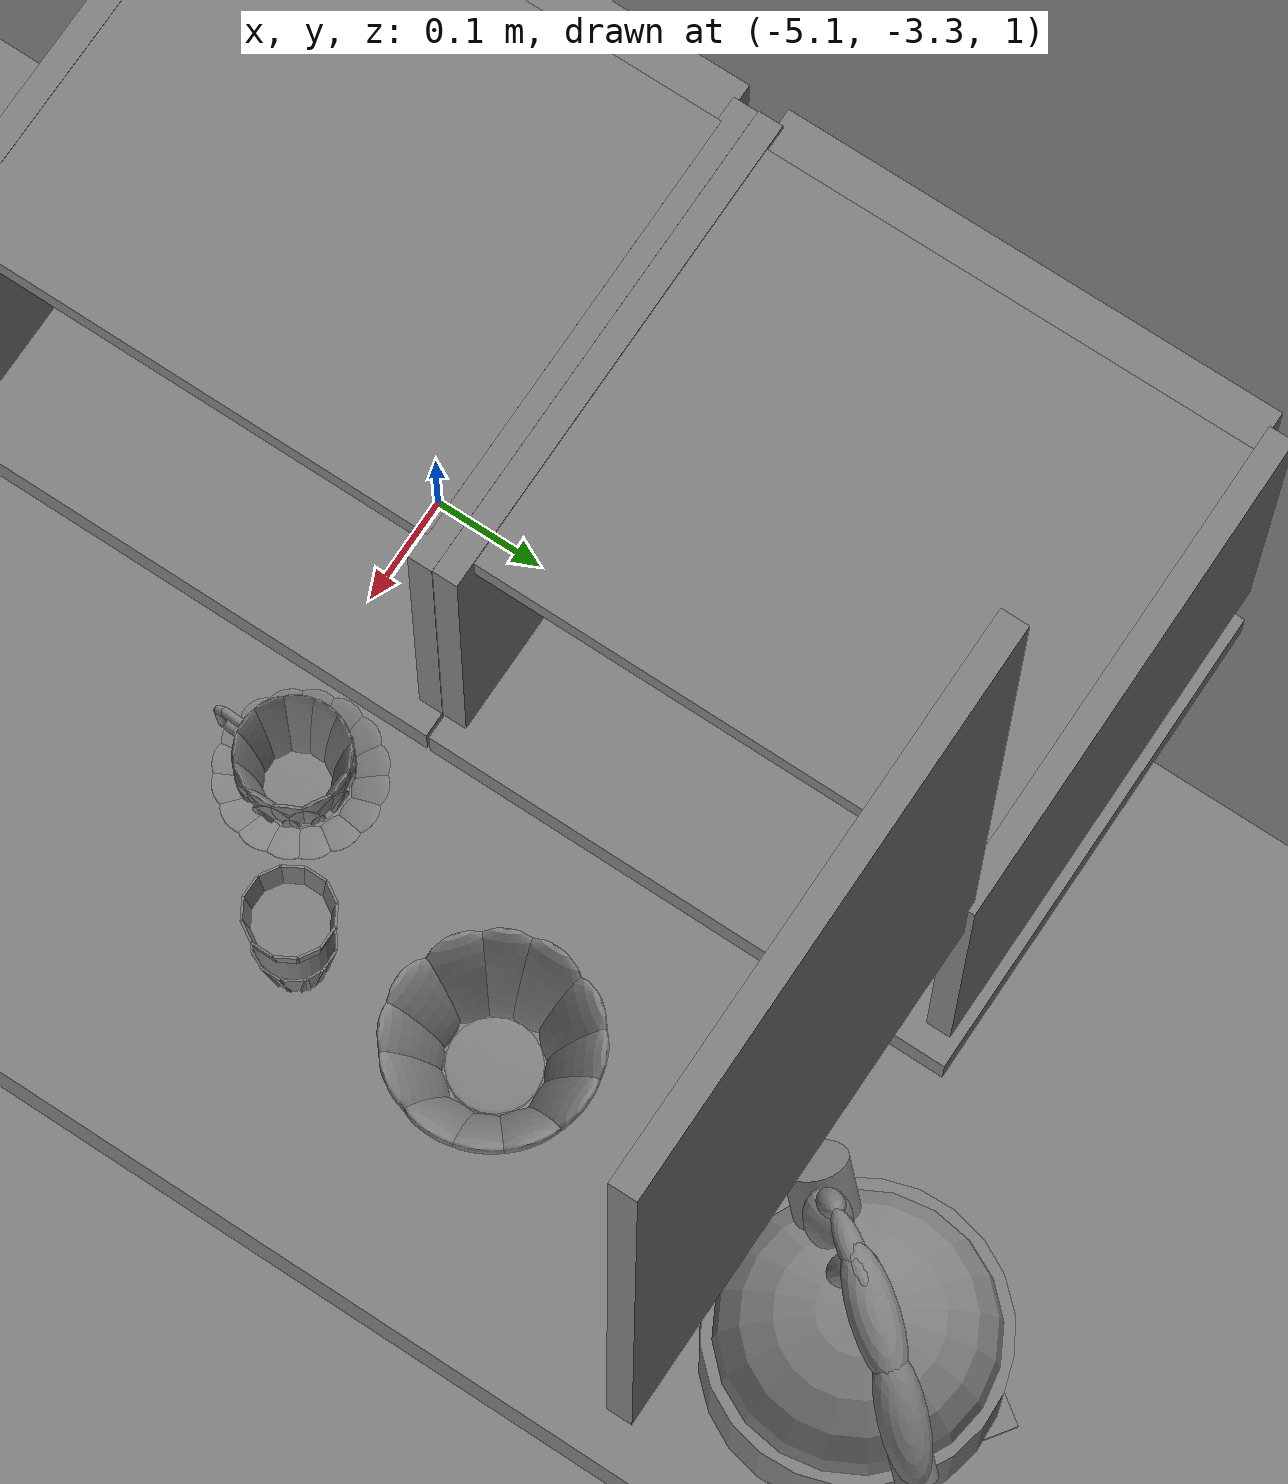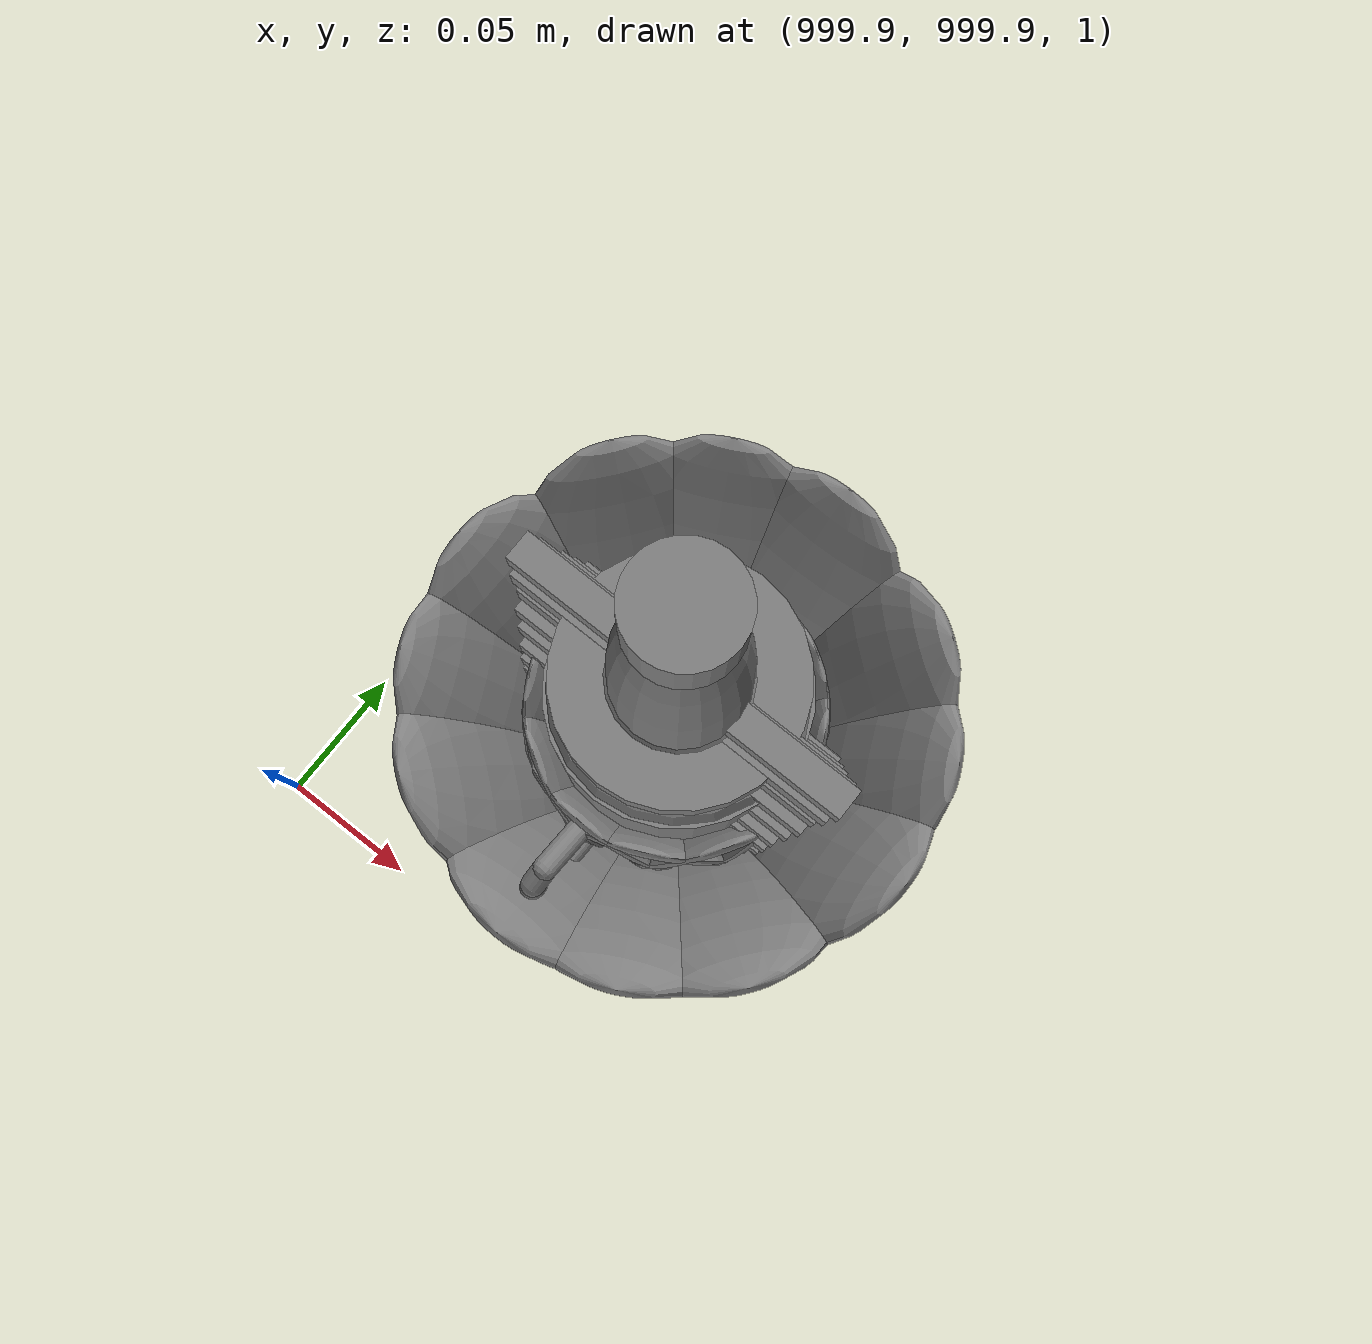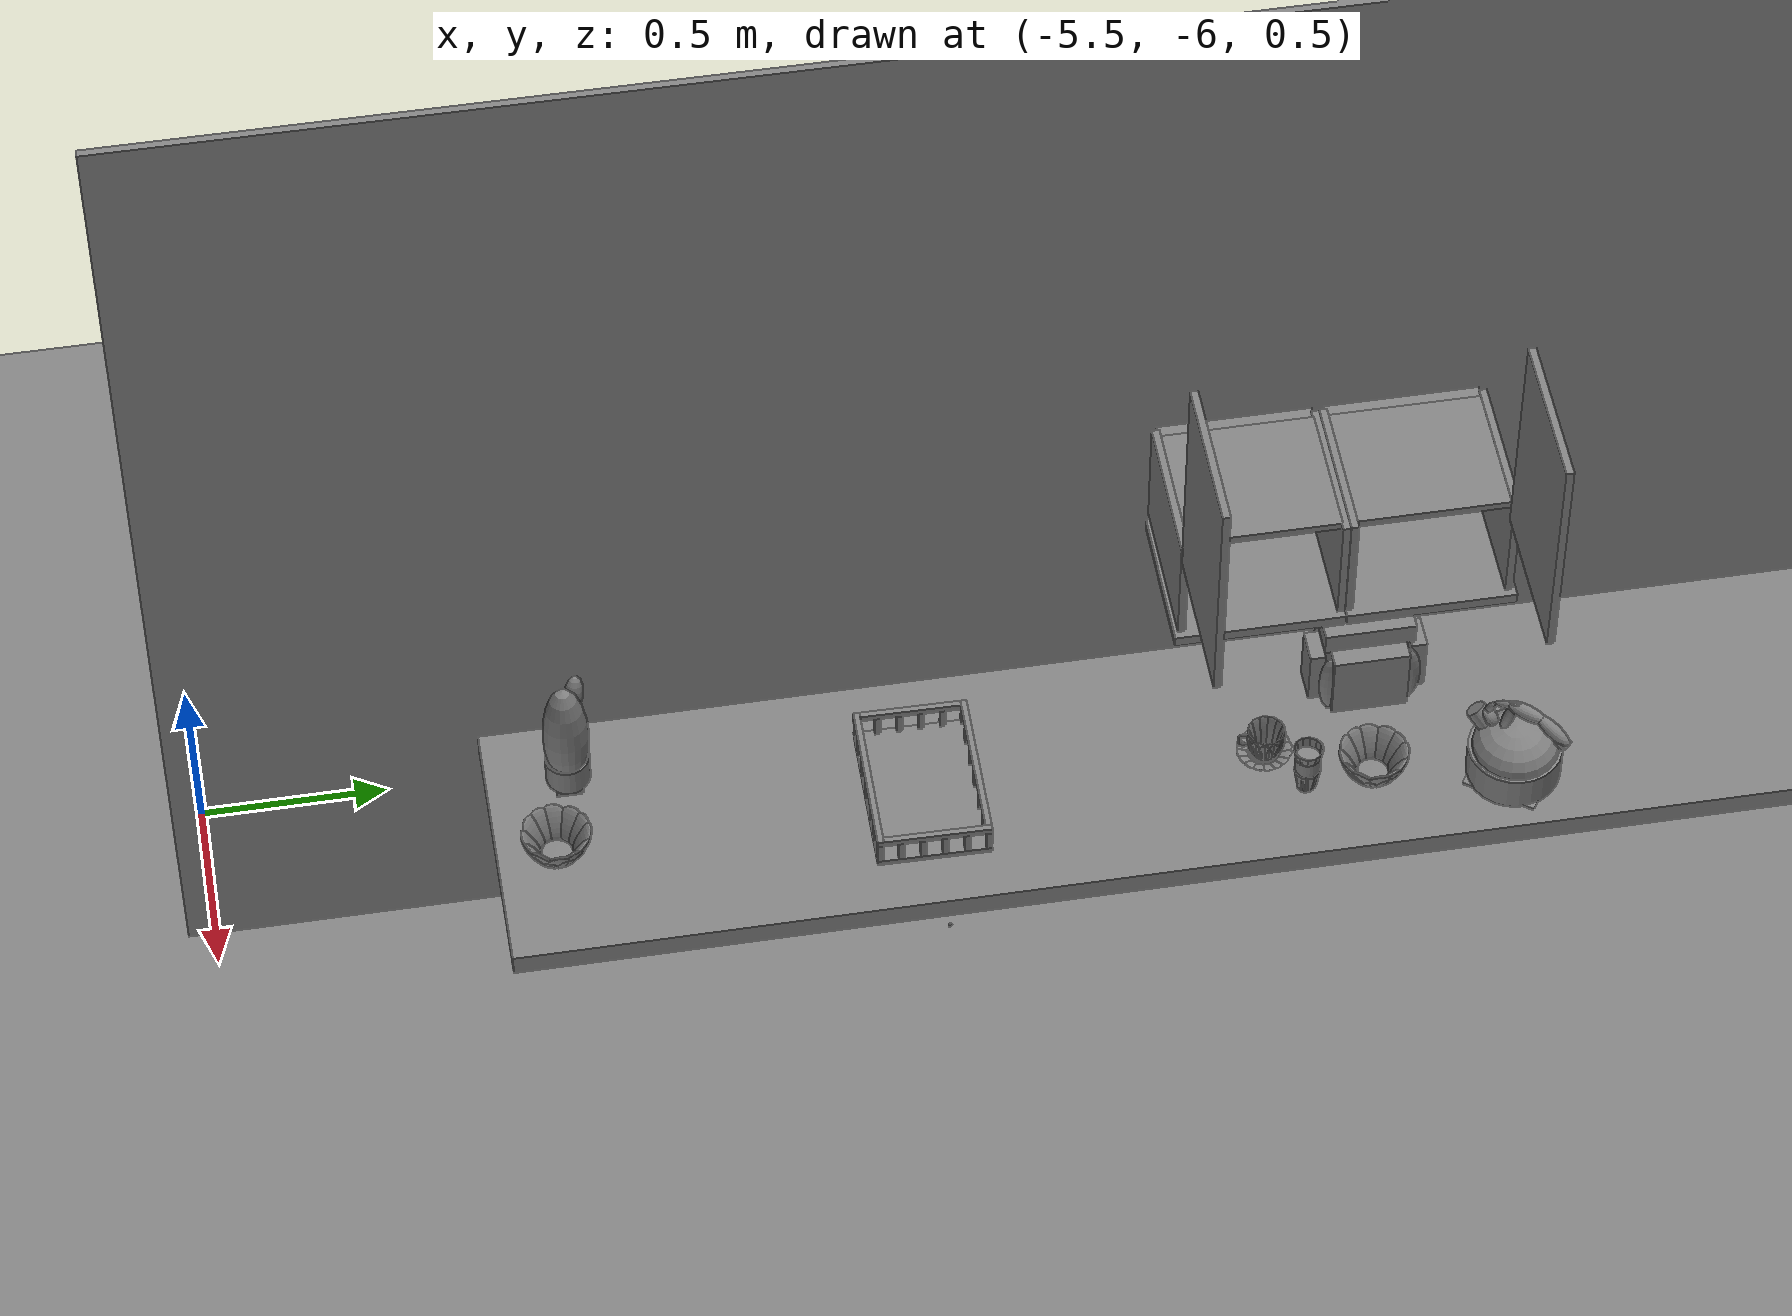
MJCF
<mujoco>
    <option gravity="0.000000000 0.000000000 -9.810000420" timestep="0.0049999999" integrator="implicitfast" density="9.8000002" viscosity="1.8000001e-05" noslip_iterations="10" iterations="100" sdf_iterations="50">
        <flag multiccd="disable"/>
    </option>
    <size memory="1000M"/>
    <compiler coordinate="local"/>
    <worldbody>
        <light cutoff="30" pos="0 1 1" dir="0 -1 -2"/>
        <light cutoff="30" pos="0 -1 1" dir="0 1 -2"/>
        <body pos="-5.046103477 -5.051773071 1.001502514" euler="0.000000000 0.000000000 0.000000000" name="Interactive Objcets_huapen">
            <geom contype="1" conaffinity="1" density="1000" type="ellipsoid" material="" rgba="0.500000000 0.500000000 0.500000000 1.000000000" solimp="0.899999976 0.949999988 0.001000000" friction="1.000000000 0.005000000 0.000100000" solref="0.020000000 1.000000000" margin="0" condim="3" group="0" pos="0.008062840 0.004346371 0.205056787" quat="1.000000000 0.000000000 0.000000000 0.000000000" size="0.059999999 0.059999999 0.180000007" name="Interactive Objcets_huapen_hua_174C9A32_B8CD_4AE7_994D_84C01E94C848"/>
            <geom contype="1" conaffinity="1" density="1000" type="cylinder" material="" rgba="0.500000000 0.500000000 0.500000000 1.000000000" solimp="0.899999976 0.949999988 0.001000000" friction="1.000000000 0.005000000 0.000100000" solref="0.020000000 1.000000000" margin="0" condim="3" group="0" pos="0.008062840 0.003952026 0.080107450" quat="1.000000000 0.000000000 0.000000000 0.000000000" size="0.057999998 0.039999999 1.000000000" name="Interactive Objcets_huapen_hua_B46B8DA4_EC29_4F59_9719_25B271D85A49"/>
            <geom contype="1" conaffinity="1" density="1000" type="box" material="" rgba="0.500000000 0.500000000 0.500000000 1.000000000" solimp="0.899999976 0.949999988 0.001000000" friction="1.000000000 0.005000000 0.000100000" solref="0.020000000 1.000000000" margin="0" condim="3" group="0" pos="0.008062840 0.003952503 0.020566106" quat="1.000000000 0.000000000 0.000000000 0.000000000" size="0.035000000 0.035000000 0.020000000" name="Interactive Objcets_huapen_hua_2F0404EB_9EB7_4F2E_BB6A_2C50B3D3B839"/>
            <geom contype="1" conaffinity="1" density="1000" type="ellipsoid" material="" rgba="0.500000000 0.500000000 0.500000000 1.000000000" solimp="0.899999976 0.949999988 0.001000000" friction="1.000000000 0.005000000 0.000100000" solref="0.020000000 1.000000000" margin="0" condim="3" group="0" pos="-0.029900074 0.033599377 0.321917295" quat="0.992658079 -0.083605267 -0.087364964 0.002748166" size="0.025000000 0.025000000 0.059999999" name="Interactive Objcets_huapen_hua_0138D695_B633_49D8_8D47_641D52F7A504"/>
            <freejoint name="Interactive Objcets_huapen"/>
        </body>
        <body pos="1000.000000000 1000.000000000 1.000000000" euler="0.000000000 0.000000000 0.000000000" name="openloong_gripper_2f85_fix_base_usda_bow_yellow_kps">
            <geom contype="1" conaffinity="1" density="1000" type="ellipsoid" material="" rgba="0.500000000 0.500000000 0.500000000 1.000000000" solimp="0.899999976 0.949999988 0.001000000" friction="1.000000000 0.005000000 0.000100000" solref="0.020000000 1.000000000" margin="0" condim="3" group="0" pos="-0.052185059 0.040283203 0.044118762" quat="0.919264615 -0.076883033 -0.225593656 -0.313287765" size="0.010000000 0.039999999 0.052000001" name="openloong_gripper_2f85_fix_base_usda_geom_B4C85EDE_D026_45C6_8AD4_DCF0E711BBFD"/>
            <geom contype="1" conaffinity="1" density="1000" type="ellipsoid" material="" rgba="0.500000000 0.500000000 0.500000000 1.000000000" solimp="0.899999976 0.949999988 0.001000000" friction="1.000000000 0.005000000 0.000100000" solref="0.020000000 1.000000000" margin="0" condim="3" group="0" pos="-0.000061035 0.065979004 0.044118762" quat="0.687598765 -0.168314874 -0.168741167 -0.685860336" size="0.010000000 0.039999999 0.052000001" name="openloong_gripper_2f85_fix_base_usda_geom_714367F3_0056_47DD_AA51_B2931C2C65B7"/>
            <geom contype="1" conaffinity="1" density="1000" type="box" material="" rgba="0.500000000 0.500000000 0.500000000 1.000000000" solimp="0.899999976 0.949999988 0.001000000" friction="1.000000000 0.005000000 0.000100000" solref="0.020000000 1.000000000" margin="0" condim="3" group="0" pos="0.000061035 0.000000000 -0.002001643" quat="1.000000000 0.000000000 0.000000000 0.000000000" size="0.029999999 0.029999999 0.002000000" name="openloong_gripper_2f85_fix_base_usda_geom_69F1B854_5738_4D31_8505_8C3FAD3F77E6"/>
            <geom contype="1" conaffinity="1" density="1000" type="ellipsoid" material="" rgba="0.500000000 0.500000000 0.500000000 1.000000000" solimp="0.899999976 0.949999988 0.001000000" friction="1.000000000 0.005000000 0.000100000" solref="0.020000000 1.000000000" margin="0" condim="3" group="0" pos="0.029418945 -0.059082031 0.044118762" quat="0.825555861 0.125530601 0.202597082 -0.511521280" size="0.010000000 0.039999999 0.052000001" name="openloong_gripper_2f85_fix_base_usda_geom_B0D02297_75AB_46DA_9B32_D286469C52A6"/>
            <geom contype="1" conaffinity="1" density="1000" type="ellipsoid" material="" rgba="0.500000000 0.500000000 0.500000000 1.000000000" solimp="0.899999976 0.949999988 0.001000000" friction="1.000000000 0.005000000 0.000100000" solref="0.020000000 1.000000000" margin="0" condim="3" group="0" pos="0.000244141 -0.065979004 0.044118762" quat="0.687598765 0.168314651 0.168741375 -0.685860336" size="0.010000000 0.039999999 0.052000001" name="openloong_gripper_2f85_fix_base_usda_geom_D6692554_5ABE_49A9_B8AB_AC45756A3AB0"/>
            <geom contype="1" conaffinity="1" density="1000" type="ellipsoid" material="" rgba="0.500000000 0.500000000 0.500000000 1.000000000" solimp="0.899999976 0.949999988 0.001000000" friction="1.000000000 0.005000000 0.000100000" solref="0.020000000 1.000000000" margin="0" condim="3" group="0" pos="0.000061035 0.000000000 0.000446677" quat="1.000000000 0.000000000 0.000000000 0.000000000" size="0.039999999 0.039999999 0.002000000" name="openloong_gripper_2f85_fix_base_usda_geom_096DAE1F_853D_4D66_BA1D_FE0909167858"/>
            <geom contype="1" conaffinity="1" density="1000" type="ellipsoid" material="" rgba="0.500000000 0.500000000 0.500000000 1.000000000" solimp="0.899999976 0.949999988 0.001000000" friction="1.000000000 0.005000000 0.000100000" solref="0.020000000 1.000000000" margin="0" condim="3" group="0" pos="0.059082031 0.029541016 0.044118762" quat="0.223252773 -0.231952220 -0.054787423 -0.945174456" size="0.010000000 0.039999999 0.052000001" name="openloong_gripper_2f85_fix_base_usda_geom_9C37E1FA_E787_4DCD_855F_8F7C555F7FD9"/>
            <geom contype="1" conaffinity="1" density="1000" type="ellipsoid" material="" rgba="0.500000000 0.500000000 0.500000000 1.000000000" solimp="0.899999976 0.949999988 0.001000000" friction="1.000000000 0.005000000 0.000100000" solref="0.020000000 1.000000000" margin="0" condim="3" group="0" pos="0.000061035 0.000000000 0.007335305" quat="1.000000000 0.000000000 0.000000000 0.000000000" size="0.039999999 0.039999999 0.002000000" name="openloong_gripper_2f85_fix_base_usda_geom_09073056_3CC8_4BFF_9675_5903D95A680D"/>
            <geom contype="1" conaffinity="1" density="1000" type="ellipsoid" material="" rgba="0.500000000 0.500000000 0.500000000 1.000000000" solimp="0.899999976 0.949999988 0.001000000" friction="1.000000000 0.005000000 0.000100000" solref="0.020000000 1.000000000" margin="0" condim="3" group="0" pos="-0.029296875 0.059082031 0.044118762" quat="0.825555861 -0.125530809 -0.202596918 -0.511521280" size="0.010000000 0.039999999 0.052000001" name="openloong_gripper_2f85_fix_base_usda_geom_9770D259_5417_4938_8EA2_3922D0B0795E"/>
            <geom contype="1" conaffinity="1" density="1000" type="ellipsoid" material="" rgba="0.500000000 0.500000000 0.500000000 1.000000000" solimp="0.899999976 0.949999988 0.001000000" friction="1.000000000 0.005000000 0.000100000" solref="0.020000000 1.000000000" margin="0" condim="3" group="0" pos="0.040222168 0.052368164 0.044118762" quat="0.429593176 -0.213750049 -0.105424821 -0.871002972" size="0.010000000 0.039999999 0.052000001" name="openloong_gripper_2f85_fix_base_usda_geom_DB4AE450_418D_4573_BAC5_E067B4852016"/>
            <geom contype="1" conaffinity="1" density="1000" type="ellipsoid" material="" rgba="0.500000000 0.500000000 0.500000000 1.000000000" solimp="0.899999976 0.949999988 0.001000000" friction="1.000000000 0.005000000 0.000100000" solref="0.020000000 1.000000000" margin="0" condim="3" group="0" pos="0.066040039 0.000000000 0.044118762" quat="0.971183062 -0.000000156 0.238334835 0.000000030" size="0.010000000 0.039999999 0.052000001" name="openloong_gripper_2f85_fix_base_usda_geom_62E7F39F_5C00_46CD_9E34_D14590EB9620"/>
            <geom contype="1" conaffinity="1" density="1000" type="ellipsoid" material="" rgba="0.500000000 0.500000000 0.500000000 1.000000000" solimp="0.899999976 0.949999988 0.001000000" friction="1.000000000 0.005000000 0.000100000" solref="0.020000000 1.000000000" margin="0" condim="3" group="0" pos="0.052307129 -0.040283203 0.044118762" quat="0.919264674 0.076882750 0.225593731 -0.313287705" size="0.010000000 0.039999999 0.052000001" name="openloong_gripper_2f85_fix_base_usda_geom_39F51895_2E84_4762_91DA_4696888F70A6"/>
            <geom contype="1" conaffinity="1" density="1000" type="ellipsoid" material="" rgba="0.500000000 0.500000000 0.500000000 1.000000000" solimp="0.899999976 0.949999988 0.001000000" friction="1.000000000 0.005000000 0.000100000" solref="0.020000000 1.000000000" margin="0" condim="3" group="0" pos="-0.065917969 0.000000000 0.044118762" quat="0.971183062 -0.000000142 -0.238334835 0.000000030" size="0.010000000 0.039999999 0.052000001" name="openloong_gripper_2f85_fix_base_usda_geom_9A5D765A_075F_424F_984C_7E48107B01DB"/>
            <geom contype="1" conaffinity="1" density="1000" type="ellipsoid" material="" rgba="0.500000000 0.500000000 0.500000000 1.000000000" solimp="0.899999976 0.949999988 0.001000000" friction="1.000000000 0.005000000 0.000100000" solref="0.020000000 1.000000000" margin="0" condim="3" group="0" pos="-0.058898926 -0.029541016 0.044118762" quat="0.223252758 0.231952101 0.054787733 -0.945174575" size="0.010000000 0.039999999 0.052000001" name="openloong_gripper_2f85_fix_base_usda_geom_65563961_99C7_47CA_B60B_1C8170677A74"/>
            <geom contype="1" conaffinity="1" density="1000" type="ellipsoid" material="" rgba="0.500000000 0.500000000 0.500000000 1.000000000" solimp="0.899999976 0.949999988 0.001000000" friction="1.000000000 0.005000000 0.000100000" solref="0.020000000 1.000000000" margin="0" condim="3" group="0" pos="-0.040100098 -0.052368164 0.044118762" quat="0.429593235 0.213749886 0.105425082 -0.871003032" size="0.010000000 0.039999999 0.052000001" name="openloong_gripper_2f85_fix_base_usda_geom_51A32EF2_DE7A_42E9_B8E2_089ED1ACD4AA"/>
            <freejoint name="openloong_gripper_2f85_fix_base_usda_bow_yellow_kps_joint"/>
            <site size="0.005000000 0.005000000 0.005000000" rgba="0.500000000 0.500000000 0.500000000 1.000000000" pos="0.000000000 0.000000000 0.000000000" quat="0.999961913 0.008726534 0.000000000 0.000000000" group="0" type="sphere" name="openloong_gripper_2f85_fix_base_usda_bow_yellow_kps"/>
        </body>
        <body pos="-3.966758728 -3.699013472 1.778668404" euler="14.168197632 -14.809568405 41.886173248" mocap="true" name="spotlight6_SpotLight"/>
        <body pos="1000.000000000 1000.000000000 1.000000000" euler="0.000000000 0.000000000 0.000000000" name="openloong_gripper_2f85_fix_base_usda_jar_01">
            <geom contype="1" conaffinity="1" density="1000" type="box" material="" rgba="0.500000000 0.500000000 0.500000000 1.000000000" solimp="0.899999976 0.949999988 0.001000000" friction="1.000000000 0.005000000 0.000100000" solref="0.020000000 1.000000000" margin="0" condim="3" group="0" pos="0.000000000 0.000000000 0.006158113" quat="1.000000000 0.000000000 0.000000000 0.000000000" size="0.020000000 0.020000000 0.005000000" name="openloong_gripper_2f85_fix_base_usda_geom_461A56DC_09B4_414D_910E_5FE7C944F83A"/>
            <geom contype="1" conaffinity="1" density="1000" type="cylinder" material="" rgba="0.500000000 0.500000000 0.500000000 1.000000000" solimp="0.899999976 0.949999988 0.001000000" friction="1.000000000 0.005000000 0.000100000" solref="0.020000000 1.000000000" margin="0" condim="3" group="0" pos="0.000000000 0.000000000 0.062744498" quat="1.000000000 0.000000000 0.000000000 0.000000000" size="0.041000001 0.052999999 1.000000000" name="openloong_gripper_2f85_fix_base_usda_geom_02DEFDA9_61F0_43B4_9D07_C296C19331CE"/>
            <geom contype="1" conaffinity="1" density="1000" type="ellipsoid" material="" rgba="0.500000000 0.500000000 0.500000000 1.000000000" solimp="0.899999976 0.949999988 0.001000000" friction="1.000000000 0.005000000 0.000100000" solref="0.020000000 1.000000000" margin="0" condim="3" group="0" pos="0.000000000 0.000000000 0.122252703" quat="1.000000000 0.000000000 0.000000000 0.000000000" size="0.035999998 0.035999998 0.010000000" name="openloong_gripper_2f85_fix_base_usda_geom_B6CAC67B_2A31_4027_B93B_8A98CDC60C67"/>
            <geom contype="1" conaffinity="1" density="1000" type="cylinder" material="" rgba="0.500000000 0.500000000 0.500000000 1.000000000" solimp="0.899999976 0.949999988 0.001000000" friction="1.000000000 0.005000000 0.000100000" solref="0.020000000 1.000000000" margin="0" condim="3" group="0" pos="0.000000000 0.000000000 0.015747190" quat="1.000000000 0.000000000 0.000000000 0.000000000" size="0.035000000 0.010000000 1.000000000" name="openloong_gripper_2f85_fix_base_usda_geom_EF7CEF00_A869_4A08_AC29_EEFD7E327852"/>
            <geom contype="1" conaffinity="1" density="1000" type="ellipsoid" material="" rgba="0.500000000 0.500000000 0.500000000 1.000000000" solimp="0.899999976 0.949999988 0.001000000" friction="1.000000000 0.005000000 0.000100000" solref="0.020000000 1.000000000" margin="0" condim="3" group="0" pos="0.000000000 0.000000000 0.115815401" quat="1.000000000 0.000000000 0.000000000 0.000000000" size="0.039999999 0.039999999 0.010000000" name="openloong_gripper_2f85_fix_base_usda_geom_C0DDE929_3354_4F02_8D17_523D2CA0B6FD"/>
            <geom contype="1" conaffinity="1" density="1000" type="cylinder" material="" rgba="0.500000000 0.500000000 0.500000000 1.000000000" solimp="0.899999976 0.949999988 0.001000000" friction="1.000000000 0.005000000 0.000100000" solref="0.020000000 1.000000000" margin="0" condim="3" group="0" pos="0.000000000 0.000000000 0.133183479" quat="1.000000000 0.000000000 0.000000000 0.000000000" size="0.037999999 0.006500000 1.000000000" name="openloong_gripper_2f85_fix_base_usda_geom_D1A5A350_ED16_4DBA_9418_7AB08E45B304"/>
            <freejoint name="openloong_gripper_2f85_fix_base_usda_jar_01_joint"/>
            <site size="0.005000000 0.005000000 0.005000000" rgba="0.500000000 0.500000000 0.500000000 1.000000000" pos="0.000000000 0.000000000 0.000000000" quat="1.000000000 0.000000000 0.000000000 0.000000000" group="0" type="sphere" name="openloong_gripper_2f85_fix_base_usda_jar_01site"/>
        </body>
        <body pos="1000.000000000 1000.000000000 1.000000000" euler="0.000000000 0.000000000 0.000000000" name="openloong_gripper_2f85_fix_base_usda_bottle_red">
            <geom contype="1" conaffinity="1" density="1000" type="ellipsoid" material="" rgba="0.500000000 0.500000000 0.500000000 1.000000000" solimp="0.899999976 0.949999988 0.001000000" friction="1.000000000 0.005000000 0.000100000" solref="0.020000000 1.000000000" margin="0" condim="3" group="0" pos="0.000000000 0.000000000 0.144284487" quat="1.000000000 0.000000000 0.000000000 0.000000000" size="0.021000000 0.021000000 0.079999998" name="openloong_gripper_2f85_fix_base_usda_geom_3529FC0C_8EB3_4795_9D47_A2C1AF495EB8"/>
            <geom contype="1" conaffinity="1" density="1000" type="cylinder" material="" rgba="0.500000000 0.500000000 0.500000000 1.000000000" solimp="0.899999976 0.949999988 0.001000000" friction="1.000000000 0.005000000 0.000100000" solref="0.020000000 1.000000000" margin="0" condim="3" group="0" pos="0.000000000 0.000000000 0.220618963" quat="1.000000000 0.000000000 0.000000000 0.000000000" size="0.016000001 0.010000000 1.000000000" name="openloong_gripper_2f85_fix_base_usda_geom_97259091_8C77_40C9_9BCC_2C1489014373"/>
            <geom contype="1" conaffinity="1" density="1000" type="ellipsoid" material="" rgba="0.500000000 0.500000000 0.500000000 1.000000000" solimp="0.899999976 0.949999988 0.001000000" friction="1.000000000 0.005000000 0.000100000" solref="0.020000000 1.000000000" margin="0" condim="3" group="0" pos="0.000000000 0.000000000 0.118945479" quat="1.000000000 0.000000000 0.000000000 0.000000000" size="0.030999999 0.030999999 0.029999999" name="openloong_gripper_2f85_fix_base_usda_geom_E174FAC3_706A_4BC5_8FEF_0F94134DFA02"/>
            <geom contype="1" conaffinity="1" density="1000" type="box" material="" rgba="0.500000000 0.500000000 0.500000000 1.000000000" solimp="0.899999976 0.949999988 0.001000000" friction="1.000000000 0.005000000 0.000100000" solref="0.020000000 1.000000000" margin="0" condim="3" group="0" pos="0.000000000 0.000000000 0.002189159" quat="1.000000000 0.000000000 0.000000000 0.000000000" size="0.020000000 0.020000000 0.003000000" name="openloong_gripper_2f85_fix_base_usda_geom_6E8C131E_50A2_4FD9_B4F1_DF4CCEFADED3"/>
            <geom contype="1" conaffinity="1" density="1000" type="cylinder" material="" rgba="0.500000000 0.500000000 0.500000000 1.000000000" solimp="0.899999976 0.949999988 0.001000000" friction="1.000000000 0.005000000 0.000100000" solref="0.020000000 1.000000000" margin="0" condim="3" group="0" pos="0.000000000 -0.000366211 0.060884237" quat="1.000000000 0.000000000 0.000000000 0.000000000" size="0.030999999 0.057999998 1.000000000" name="openloong_gripper_2f85_fix_base_usda_geom_8A425903_D866_4742_A7A4_DFF31D515094"/>
            <freejoint name="openloong_gripper_2f85_fix_base_usda_bottle_red_joint"/>
            <site size="0.005000000 0.005000000 0.005000000" rgba="0.500000000 0.500000000 0.500000000 1.000000000" pos="0.000000000 0.000000000 0.000000000" quat="0.999961913 0.008726535 0.000000000 0.000000000" group="0" type="sphere" name="openloong_gripper_2f85_fix_base_usda_bottle_redsite"/>
        </body>
        <body pos="-3.962449551 -4.196350098 1.847062469" euler="-138.276626587 -31.172130585 -67.938583374" mocap="true" name="spotlight5_SpotLight"/>
        <body pos="-4.063948154 -4.204555511 1.762646794" euler="-11.932345390 66.557022095 45.253032684" mocap="true" name="spotlight3_SpotLight"/>
        <body pos="1000.000000000 1000.000000000 1.000000000" euler="0.000000000 0.000000000 0.000000000" name="openloong_gripper_2f85_fix_base_usda_salt">
            <geom contype="1" conaffinity="1" density="1000" type="box" material="" rgba="0.500000000 0.500000000 0.500000000 1.000000000" solimp="0.899999976 0.949999988 0.001000000" friction="1.000000000 0.005000000 0.000100000" solref="0.020000000 1.000000000" margin="0" condim="3" group="0" pos="0.000305176 0.000000000 0.084862232" quat="1.000000000 0.000000000 0.000000000 0.000000000" size="0.048999999 0.018999999 0.005000000" name="openloong_gripper_2f85_fix_base_usda_geom_F27AA240_35D7_470F_96C1_CB8796F5C1F0"/>
            <geom contype="1" conaffinity="1" density="1000" type="box" material="" rgba="0.500000000 0.500000000 0.500000000 1.000000000" solimp="0.899999976 0.949999988 0.001000000" friction="1.000000000 0.005000000 0.000100000" solref="0.020000000 1.000000000" margin="0" condim="3" group="0" pos="0.000305176 0.000000000 0.104564309" quat="1.000000000 0.000000000 0.000000000 0.000000000" size="0.052000001 0.014000000 0.005000000" name="openloong_gripper_2f85_fix_base_usda_geom_246C4687_5B43_4538_8BE7_F07AD2B3B864"/>
            <geom contype="1" conaffinity="1" density="1000" type="box" material="" rgba="0.500000000 0.500000000 0.500000000 1.000000000" solimp="0.899999976 0.949999988 0.001000000" friction="1.000000000 0.005000000 0.000100000" solref="0.020000000 1.000000000" margin="0" condim="3" group="0" pos="0.000305176 0.000000000 0.114487171" quat="1.000000000 0.000000000 0.000000000 0.000000000" size="0.054000001 0.011500000 0.005000000" name="openloong_gripper_2f85_fix_base_usda_geom_01FD418A_E3D6_4537_A5C0_E0D489F0E018"/>
            <geom contype="1" conaffinity="1" density="1000" type="box" material="" rgba="0.500000000 0.500000000 0.500000000 1.000000000" solimp="0.899999976 0.949999988 0.001000000" friction="1.000000000 0.005000000 0.000100000" solref="0.020000000 1.000000000" margin="0" condim="3" group="0" pos="0.000305176 0.000000000 0.075103164" quat="1.000000000 0.000000000 0.000000000 0.000000000" size="0.048000000 0.020000000 0.005000000" name="openloong_gripper_2f85_fix_base_usda_geom_6861BC60_CCC6_4B5A_9EE5_E09416856B78"/>
            <geom contype="1" conaffinity="1" density="1000" type="box" material="" rgba="0.500000000 0.500000000 0.500000000 1.000000000" solimp="0.899999976 0.949999988 0.001000000" friction="1.000000000 0.005000000 0.000100000" solref="0.020000000 1.000000000" margin="0" condim="3" group="0" pos="0.000305176 0.000000000 0.134892464" quat="1.000000000 0.000000000 0.000000000 0.000000000" size="0.057000000 0.007000000 0.005000000" name="openloong_gripper_2f85_fix_base_usda_geom_1C2C690A_A7B4_4261_925C_8B9730DB2A51"/>
            <geom contype="1" conaffinity="1" density="1000" type="box" material="" rgba="0.500000000 0.500000000 0.500000000 1.000000000" solimp="0.899999976 0.949999988 0.001000000" friction="1.000000000 0.005000000 0.000100000" solref="0.020000000 1.000000000" margin="0" condim="3" group="0" pos="0.000305176 0.000000000 0.094920278" quat="1.000000000 0.000000000 0.000000000 0.000000000" size="0.050000001 0.017000001 0.005000000" name="openloong_gripper_2f85_fix_base_usda_geom_6BC34E5C_7C17_4EF8_A189_67651A740A14"/>
            <geom contype="1" conaffinity="1" density="1000" type="box" material="" rgba="0.500000000 0.500000000 0.500000000 1.000000000" solimp="0.899999976 0.949999988 0.001000000" friction="1.000000000 0.005000000 0.000100000" solref="0.020000000 1.000000000" margin="0" condim="3" group="0" pos="0.000305176 0.000000000 0.065204859" quat="1.000000000 0.000000000 0.000000000 0.000000000" size="0.045000002 0.021000000 0.005000000" name="openloong_gripper_2f85_fix_base_usda_geom_7831143B_D842_465F_9D78_9B484EDE0C0D"/>
            <geom contype="1" conaffinity="1" density="1000" type="box" material="" rgba="0.500000000 0.500000000 0.500000000 1.000000000" solimp="0.899999976 0.949999988 0.001000000" friction="1.000000000 0.005000000 0.000100000" solref="0.020000000 1.000000000" margin="0" condim="3" group="0" pos="0.000305176 0.000000000 0.144135714" quat="1.000000000 0.000000000 0.000000000 0.000000000" size="0.059000000 0.005000000 0.004000000" name="openloong_gripper_2f85_fix_base_usda_geom_77A8458E_0FA0_48B4_BAA5_C1F346990659"/>
            <geom contype="1" conaffinity="1" density="1000" type="box" material="" rgba="0.500000000 0.500000000 0.500000000 1.000000000" solimp="0.899999976 0.949999988 0.001000000" friction="1.000000000 0.005000000 0.000100000" solref="0.020000000 1.000000000" margin="0" condim="3" group="0" pos="0.000000000 0.000000000 0.031593561" quat="1.000000000 0.000000000 0.000000000 0.000000000" size="0.041999999 0.024000000 0.029999999" name="openloong_gripper_2f85_fix_base_usda_geom_A9AC2253_8C88_4CA8_8C29_560444C3609E"/>
            <geom contype="1" conaffinity="1" density="1000" type="box" material="" rgba="0.500000000 0.500000000 0.500000000 1.000000000" solimp="0.899999976 0.949999988 0.001000000" friction="1.000000000 0.005000000 0.000100000" solref="0.020000000 1.000000000" margin="0" condim="3" group="0" pos="0.000305176 0.000000000 0.124608755" quat="1.000000000 0.000000000 0.000000000 0.000000000" size="0.055000000 0.008000000 0.005000000" name="openloong_gripper_2f85_fix_base_usda_geom_CFA6F51E_71DE_43FC_85E1_1E7BEC52DC75"/>
            <freejoint name="openloong_gripper_2f85_fix_base_usda_salt_joint"/>
            <site size="0.005000000 0.005000000 0.005000000" rgba="0.500000000 0.500000000 0.500000000 1.000000000" pos="0.000000000 0.000000000 0.000000000" quat="1.000000000 0.000000000 0.000000000 0.000000000" group="0" type="sphere" name="openloong_gripper_2f85_fix_base_usda_saltsite"/>
        </body>
        <body pos="1000.000000000 1000.000000000 1.000000000" euler="0.000000000 0.000000000 0.000000000" name="openloong_gripper_2f85_fix_base_usda_coffeecup_white_kps">
            <geom contype="1" conaffinity="1" density="1000" type="capsule" material="" rgba="0.500000000 0.500000000 0.500000000 1.000000000" solimp="0.899999976 0.949999988 0.001000000" friction="1.000000000 0.005000000 0.000100000" solref="0.020000000 1.000000000" margin="0" condim="3" group="0" pos="-0.000854492 -0.065795898 0.050029993" quat="0.343559504 -0.613204718 0.626912475 0.336047262" size="0.004000000 0.005000000 1.000000000" name="openloong_gripper_2f85_fix_base_usda_geom_054CF024_62E9_4E7A_BED7_AFE09181A58D"/>
            <geom contype="1" conaffinity="1" density="1000" type="ellipsoid" material="" rgba="0.500000000 0.500000000 0.500000000 1.000000000" solimp="0.899999976 0.949999988 0.001000000" friction="1.000000000 0.005000000 0.000100000" solref="0.020000000 1.000000000" margin="0" condim="3" group="0" pos="-0.000793457 -0.038452148 0.048040152" quat="0.711656272 0.066323131 -0.067805752 0.696095467" size="0.005000000 0.029999999 0.048999999" name="openloong_gripper_2f85_fix_base_usda_geom_E7BACF8E_400C_4038_823E_B495D5D70BCC"/>
            <geom contype="1" conaffinity="1" density="1000" type="ellipsoid" material="" rgba="0.500000000 0.500000000 0.500000000 1.000000000" solimp="0.899999976 0.949999988 0.001000000" friction="1.000000000 0.005000000 0.000100000" solref="0.020000000 1.000000000" margin="0" condim="3" group="0" pos="0.037719727 -0.001892090 0.048040152" quat="0.995387912 0.001371633 0.094835162 -0.014391154" size="0.005000000 0.029999999 0.048999999" name="openloong_gripper_2f85_fix_base_usda_geom_E296E2E5_5412_46CE_A908_91A1FDEC24EB"/>
            <geom contype="1" conaffinity="1" density="1000" type="ellipsoid" material="" rgba="0.500000000 0.500000000 0.500000000 1.000000000" solimp="0.899999976 0.949999988 0.001000000" friction="1.000000000 0.005000000 0.000100000" solref="0.020000000 1.000000000" margin="0" condim="3" group="0" pos="0.033996582 0.015502930 0.048040152" quat="0.970659733 -0.021051638 0.092478797 0.220962167" size="0.005000000 0.029999999 0.048999999" name="openloong_gripper_2f85_fix_base_usda_geom_856B0C53_A2D8_47C9_9943_150AF940D645"/>
            <geom contype="1" conaffinity="1" density="1000" type="box" material="" rgba="0.500000000 0.500000000 0.500000000 1.000000000" solimp="0.899999976 0.949999988 0.001000000" friction="1.000000000 0.005000000 0.000100000" solref="0.020000000 1.000000000" margin="0" condim="3" group="0" pos="0.000793457 -0.000183105 0.000156164" quat="0.714879215 0.000000000 0.000000000 0.699247897" size="0.020000000 0.020000000 0.002000000" name="openloong_gripper_2f85_fix_base_usda_geom_C9DFBD2C_5F56_4497_A38D_6279FFC4CD4F"/>
            <geom contype="1" conaffinity="1" density="1000" type="ellipsoid" material="" rgba="0.500000000 0.500000000 0.500000000 1.000000000" solimp="0.899999976 0.949999988 0.001000000" friction="1.000000000 0.005000000 0.000100000" solref="0.020000000 1.000000000" margin="0" condim="3" group="0" pos="-0.019409180 -0.033081055 0.048040152" quat="0.866879702 0.046630561 -0.082595348 0.489411235" size="0.005000000 0.029999999 0.048999999" name="openloong_gripper_2f85_fix_base_usda_geom_99BC33E4_1787_4000_A498_9E8CF86907FC"/>
            <geom contype="1" conaffinity="1" density="1000" type="ellipsoid" material="" rgba="0.500000000 0.500000000 0.500000000 1.000000000" solimp="0.899999976 0.949999988 0.001000000" friction="1.000000000 0.005000000 0.000100000" solref="0.020000000 1.000000000" margin="0" condim="3" group="0" pos="-0.016052246 0.033264160 0.048040152" quat="0.840792537 -0.050782297 -0.080109790 -0.532983541" size="0.005000000 0.029999999 0.048999999" name="openloong_gripper_2f85_fix_base_usda_geom_5F1150E9_DD5A_4B69_8852_8FB4958AA168"/>
            <geom contype="1" conaffinity="1" density="1000" type="capsule" material="" rgba="0.500000000 0.500000000 0.500000000 1.000000000" solimp="0.899999976 0.949999988 0.001000000" friction="1.000000000 0.005000000 0.000100000" solref="0.020000000 1.000000000" margin="0" condim="3" group="0" pos="-0.000549316 -0.053527832 0.046825886" quat="0.505496025 -0.494442940 0.505495846 0.494442940" size="0.004000000 0.005000000 1.000000000" name="openloong_gripper_2f85_fix_base_usda_geom_DB701ED5_D62C_4489_AD68_B8FA028D7AF6"/>
            <geom contype="1" conaffinity="1" density="1000" type="ellipsoid" material="" rgba="0.500000000 0.500000000 0.500000000 1.000000000" solimp="0.899999976 0.949999988 0.001000000" friction="1.000000000 0.005000000 0.000100000" solref="0.020000000 1.000000000" margin="0" condim="3" group="0" pos="-0.032104492 0.018920898 0.048040152" quat="0.958129764 -0.025742561 -0.091288343 -0.270168930" size="0.005000000 0.029999999 0.048999999" name="openloong_gripper_2f85_fix_base_usda_geom_D23A29D3_07FB_4E20_AA31_7684BF88EB98"/>
            <geom contype="1" conaffinity="1" density="1000" type="ellipsoid" material="" rgba="0.500000000 0.500000000 0.500000000 1.000000000" solimp="0.899999976 0.949999988 0.001000000" friction="1.000000000 0.005000000 0.000100000" solref="0.020000000 1.000000000" margin="0" condim="3" group="0" pos="-0.037597656 0.000305176 0.048040152" quat="0.995387554 -0.001371440 -0.094839431 -0.014389008" size="0.005000000 0.029999999 0.048999999" name="openloong_gripper_2f85_fix_base_usda_geom_09F3D78B_E582_4C2C_B54D_77BFBECC48D9"/>
            <geom contype="1" conaffinity="1" density="1000" type="capsule" material="" rgba="0.500000000 0.500000000 0.500000000 1.000000000" solimp="0.899999976 0.949999988 0.001000000" friction="1.000000000 0.005000000 0.000100000" solref="0.020000000 1.000000000" margin="0" condim="3" group="0" pos="-0.000366211 -0.043762207 0.044118762" quat="0.260488123 -0.651174724 0.665731549 0.254792154" size="0.004000000 0.003000000 1.000000000" name="openloong_gripper_2f85_fix_base_usda_geom_F15563CA_B8C2_4243_BA88_7223FE809409"/>
            <geom contype="1" conaffinity="1" density="1000" type="capsule" material="" rgba="0.500000000 0.500000000 0.500000000 1.000000000" solimp="0.899999976 0.949999988 0.001000000" friction="1.000000000 0.005000000 0.000100000" solref="0.020000000 1.000000000" margin="0" condim="3" group="0" pos="-0.000915527 -0.068542480 0.082936406" quat="0.624995589 -0.339446366 0.347034454 0.611329615" size="0.004000000 0.004000000 1.000000000" name="openloong_gripper_2f85_fix_base_usda_geom_29A7B86D_CE23_4EA0_939F_27FAB6B3B8CB"/>
            <geom contype="1" conaffinity="1" density="1000" type="ellipsoid" material="" rgba="0.500000000 0.500000000 0.500000000 1.000000000" solimp="0.899999976 0.949999988 0.001000000" friction="1.000000000 0.005000000 0.000100000" solref="0.020000000 1.000000000" margin="0" condim="3" group="0" pos="0.016113281 -0.034851074 0.048040152" quat="0.840793252 0.050779939 0.080106191 -0.532983422" size="0.005000000 0.029999999 0.048999999" name="openloong_gripper_2f85_fix_base_usda_geom_9D73885F_EE64_4DD9_8B75_DD86292012F1"/>
            <geom contype="1" conaffinity="1" density="1000" type="ellipsoid" material="" rgba="0.500000000 0.500000000 0.500000000 1.000000000" solimp="0.899999976 0.949999988 0.001000000" friction="1.000000000 0.005000000 0.000100000" solref="0.020000000 1.000000000" margin="0" condim="3" group="0" pos="0.000854492 0.036865234 0.048040152" quat="0.711656570 -0.066320375 0.067802906 0.696095705" size="0.005000000 0.029999999 0.048999999" name="openloong_gripper_2f85_fix_base_usda_geom_91BCE888_0058_40BE_9BA0_C1143BFF87C8"/>
            <geom contype="1" conaffinity="1" density="1000" type="ellipsoid" material="" rgba="0.500000000 0.500000000 0.500000000 1.000000000" solimp="0.899999976 0.949999988 0.001000000" friction="1.000000000 0.005000000 0.000100000" solref="0.020000000 1.000000000" margin="0" condim="3" group="0" pos="-0.033935547 -0.017089844 0.048040152" quat="0.970659137 0.021052625 -0.092483103 0.220962465" size="0.005000000 0.029999999 0.048999999" name="openloong_gripper_2f85_fix_base_usda_geom_15CCA452_AD56_4B9A_B32F_0E0C0BD73FB8"/>
            <geom contype="1" conaffinity="1" density="1000" type="ellipsoid" material="" rgba="0.500000000 0.500000000 0.500000000 1.000000000" solimp="0.899999976 0.949999988 0.001000000" friction="1.000000000 0.005000000 0.000100000" solref="0.020000000 1.000000000" margin="0" condim="3" group="0" pos="0.019531250 0.031494141 0.048040152" quat="0.866880119 -0.046628602 0.082591817 0.489411235" size="0.005000000 0.029999999 0.048999999" name="openloong_gripper_2f85_fix_base_usda_geom_EBD669DA_A2E4_49DE_BFE5_D8FD813760CF"/>
            <geom contype="1" conaffinity="1" density="1000" type="ellipsoid" material="" rgba="0.500000000 0.500000000 0.500000000 1.000000000" solimp="0.899999976 0.949999988 0.001000000" friction="1.000000000 0.005000000 0.000100000" solref="0.020000000 1.000000000" margin="0" condim="3" group="0" pos="0.032165527 -0.020507812 0.048040152" quat="0.958128154 0.025740955 0.091285400 -0.270175666" size="0.005000000 0.029999999 0.048999999" name="openloong_gripper_2f85_fix_base_usda_geom_9B7A48C8_B7A5_40A8_9F83_79B040E6D469"/>
            <geom contype="1" conaffinity="1" density="1000" type="capsule" material="" rgba="0.500000000 0.500000000 0.500000000 1.000000000" solimp="0.899999976 0.949999988 0.001000000" friction="1.000000000 0.005000000 0.000100000" solref="0.020000000 1.000000000" margin="0" condim="3" group="0" pos="-0.000610352 -0.056823730 0.083572865" quat="0.452654332 -0.541215360 0.553313971 0.442756712" size="0.004000000 0.009000000 1.000000000" name="openloong_gripper_2f85_fix_base_usda_geom_045B2AC7_090C_48AE_9C40_384F5D9122CC"/>
            <geom contype="1" conaffinity="1" density="1000" type="ellipsoid" material="" rgba="0.500000000 0.500000000 0.500000000 1.000000000" solimp="0.899999976 0.949999988 0.001000000" friction="1.000000000 0.005000000 0.000100000" solref="0.020000000 1.000000000" margin="0" condim="3" group="0" pos="0.000061035 -0.000183105 0.001848221" quat="0.714879215 0.000000000 0.000000000 0.699247897" size="0.029999999 0.029999999 0.001000000" name="openloong_gripper_2f85_fix_base_usda_geom_3D432C5E_B6AC_487D_8EBE_0AADD300210C"/>
            <geom contype="1" conaffinity="1" density="1000" type="capsule" material="" rgba="0.500000000 0.500000000 0.500000000 1.000000000" solimp="0.899999976 0.949999988 0.001000000" friction="1.000000000 0.005000000 0.000100000" solref="0.020000000 1.000000000" margin="0" condim="3" group="0" pos="-0.000976562 -0.071838379 0.066101432" quat="0.031849027 -0.698553741 0.714169443 0.031152546" size="0.004000000 0.012000000 1.000000000" name="openloong_gripper_2f85_fix_base_usda_geom_1E44F46F_468B_4DD9_8476_6F57383D35A6"/>
            <freejoint name="openloong_gripper_2f85_fix_base_usda_coffeecup_white_kps_joint"/>
            <site size="0.005000000 0.005000000 0.005000000" rgba="0.500000000 0.500000000 0.500000000 1.000000000" pos="0.000000000 0.000000000 0.000000000" quat="0.999961913 0.008726534 0.000000000 0.000000000" group="0" type="sphere" name="openloong_gripper_2f85_fix_base_usda_coffeecup_white_kps"/>
        </body>
        <body pos="0.000000000 0.000000000 0.000000000" euler="0.000000000 0.000000000 0.000000000" name="Static Objcets_Static Objcets">
            <geom contype="1" conaffinity="1" density="1000" type="box" material="" rgba="0.500000000 0.500000000 0.500000000 1.000000000" solimp="0.899999976 0.949999988 0.001000000" friction="1.000000000 0.005000000 0.000100000" solref="0.020000000 1.000000000" margin="0" condim="3" group="0" pos="-4.999745846 -3.497932911 1.764780521" quat="0.707107067 0.707106471 0.000000000 0.000000000" size="0.200000003 0.159999996 0.010000000" name="Static Objcets_geom_195D28DB_A664_4110_8C7F_8313AF236662"/>
            <geom contype="1" conaffinity="1" density="1000" type="box" material="" rgba="0.500000000 0.500000000 0.500000000 1.000000000" solimp="0.899999976 0.949999988 0.001000000" friction="1.000000000 0.005000000 0.000100000" solref="0.020000000 1.000000000" margin="0" condim="3" group="0" pos="-4.979488373 -3.297635794 1.591412544" quat="0.707106829 0.707106709 0.000000000 0.000000000" size="0.200000003 0.015000000 0.219999999" name="Static Objcets_geom_3CF1BCA5_ACEF_491F_86E5_139D0E23B111"/>
            <geom contype="1" conaffinity="1" density="1000" type="box" material="" rgba="0.500000000 0.500000000 0.500000000 1.000000000" solimp="0.899999976 0.949999988 0.001000000" friction="1.000000000 0.005000000 0.000100000" solref="0.020000000 1.000000000" margin="0" condim="3" group="0" pos="-4.999745846 -3.087441683 1.763863802" quat="0.707107067 0.707106471 0.000000000 0.000000000" size="0.200000003 0.159999996 0.010000000" name="Static Objcets_geom_DB186461_8161_4867_AE13_4D08F3DE68C6"/>
            <geom contype="1" conaffinity="1" density="1000" type="box" material="" rgba="0.500000000 0.500000000 0.500000000 1.000000000" solimp="0.899999976 0.949999988 0.001000000" friction="1.000000000 0.005000000 0.000100000" solref="0.020000000 1.000000000" margin="0" condim="3" group="0" pos="-5.189302921 -3.293644905 1.760152459" quat="0.707107067 0.707106471 0.000000000 0.000000000" size="0.025000000 0.159999996 0.200000003" name="Static Objcets_geom_53487D57_0267_4197_9283_D566D52B3AD4"/>
            <geom contype="1" conaffinity="1" density="1000" type="box" material="" rgba="0.500000000 0.500000000 0.500000000 1.000000000" solimp="0.899999976 0.949999988 0.001000000" friction="1.000000000 0.005000000 0.000100000" solref="0.020000000 1.000000000" margin="0" condim="3" group="0" pos="-5.000125408 -3.294431210 1.913951039" quat="0.707107067 0.707106471 0.000000000 0.000000000" size="0.180000007 0.010000000 0.200000003" name="Static Objcets_geom_0E2326E6_9371_4F39_A925_7B7718A65AE3"/>
            <geom contype="1" conaffinity="1" density="1000" type="box" material="" rgba="0.500000000 0.500000000 0.500000000 1.000000000" solimp="0.899999976 0.949999988 0.001000000" friction="1.000000000 0.005000000 0.000100000" solref="0.020000000 1.000000000" margin="0" condim="3" group="0" pos="-5.000125408 -2.861802340 1.913950682" quat="0.707107067 0.707106471 0.000000000 0.000000000" size="0.180000007 0.010000000 0.200000003" name="Static Objcets_geom_11A05922_1062_4AE7_AA86_05E01DE56CA4"/>
            <geom contype="1" conaffinity="1" density="1000" type="box" material="" rgba="0.500000000 0.500000000 0.500000000 1.000000000" solimp="0.899999976 0.949999988 0.001000000" friction="1.000000000 0.005000000 0.000100000" solref="0.020000000 1.000000000" margin="0" condim="3" group="0" pos="-4.979488373 -2.855390549 1.591412187" quat="0.707106709 0.707106769 0.000000000 0.000000000" size="0.200000003 0.015000000 0.219999999" name="Static Objcets_geom_B069C6E5_3DB6_4CBF_B557_D50A7800391E"/>
            <geom contype="1" conaffinity="1" density="1000" type="box" material="" rgba="0.500000000 0.500000000 0.500000000 1.000000000" solimp="0.899999976 0.949999988 0.001000000" friction="1.000000000 0.005000000 0.000100000" solref="0.020000000 1.000000000" margin="0" condim="3" group="0" pos="-4.999745846 -3.066934109 1.765979409" quat="0.707107067 0.707106471 0.000000000 0.000000000" size="0.200000003 0.159999996 0.010000000" name="Static Objcets_geom_3A8891F9_5B8A_4705_AD0F_BF297810661C"/>
            <geom contype="1" conaffinity="1" density="1000" type="box" material="" rgba="0.500000000 0.500000000 0.500000000 1.000000000" solimp="0.899999976 0.949999988 0.001000000" friction="1.000000000 0.005000000 0.000100000" solref="0.020000000 1.000000000" margin="0" condim="3" group="0" pos="-4.999745846 -2.653569937 1.764779806" quat="0.707107067 0.707106471 0.000000000 0.000000000" size="0.200000003 0.159999996 0.010000000" name="Static Objcets_geom_8112EA3E_6EF6_49CC_B2BE_E1634B6E9BEE"/>
            <geom contype="1" conaffinity="1" density="1000" type="box" material="" rgba="0.500000000 0.500000000 0.500000000 1.000000000" solimp="0.899999976 0.949999988 0.001000000" friction="1.000000000 0.005000000 0.000100000" solref="0.020000000 1.000000000" margin="0" condim="3" group="0" pos="-5.189302921 -2.861564636 1.760152102" quat="0.707107067 0.707106471 0.000000000 0.000000000" size="0.025000000 0.159999996 0.200000003" name="Static Objcets_geom_63B74D08_E138_44A3_802F_62A6E7A51F23"/>
            <geom contype="1" conaffinity="1" density="1000" type="box" material="" rgba="0.500000000 0.500000000 0.500000000 1.000000000" solimp="0.899999976 0.949999988 0.001000000" friction="1.000000000 0.005000000 0.000100000" solref="0.020000000 1.000000000" margin="0" condim="3" group="0" pos="-4.873187065 -2.461376429 0.977675021" quat="0.707107067 0.707106471 0.000000000 0.000000000" size="0.370000005 0.029999999 2.799999952" name="Static Objcets_geom_F5735D8F_8CD9_4163_8667_891FDAA75AEF"/>
            <geom contype="1" conaffinity="1" density="1000" type="box" material="" rgba="0.500000000 0.500000000 0.500000000 1.000000000" solimp="0.899999976 0.949999988 0.001000000" friction="1.000000000 0.005000000 0.000100000" solref="0.020000000 1.000000000" margin="0" condim="3" group="0" pos="-5.244853973 -2.375543594 1.820221663" quat="0.707107008 0.707106531 0.000000000 0.000000000" size="0.010000000 1.500000000 3.700000048" name="Static Objcets_geom_316FCFD5_7640_44C1_9747_A0208392AD12"/>
            <geom contype="1" conaffinity="1" density="1000" type="box" material="" rgba="0.500000000 0.500000000 0.500000000 1.000000000" solimp="0.899999976 0.949999988 0.001000000" friction="1.000000000 0.005000000 0.000100000" solref="0.020000000 1.000000000" margin="0" condim="3" group="0" pos="-0.720102787 0.222944975 -1.102830648" quat="0.000000954 1.000000000 0.000000000 0.000000000" size="8.000000000 8.000000000 0.010000000" name="Static Objcets_geom_2941B982_413B_440F_9AB3_90924702775D"/>
        </body>
        <body pos="-4.685121059 -2.618872881 1.139834642" euler="-89.999885559 -75.046211243 -179.999633789" name="Interactive Objcets_shuihu">
            <geom contype="1" conaffinity="1" density="1000" type="ellipsoid" material="" rgba="0.500000000 0.500000000 0.500000000 1.000000000" solimp="0.899999976 0.949999988 0.001000000" friction="1.000000000 0.005000000 0.000100000" solref="0.020000000 1.000000000" margin="0" condim="3" group="0" pos="0.031587839 0.066336274 0.011863232" quat="0.813834965 -0.098448642 0.568551302 0.068776846" size="0.020000000 0.059999999 0.015000000" name="Interactive Objcets_geom_E27FEAC4_B97D_4872_9AA4_6AAF3BC78C59"/>
            <geom contype="1" conaffinity="1" density="1000" type="cylinder" material="" rgba="0.500000000 0.500000000 0.500000000 1.000000000" solimp="0.899999976 0.949999988 0.001000000" friction="1.000000000 0.005000000 0.000100000" solref="0.020000000 1.000000000" margin="0" condim="3" group="0" pos="0.097564876 0.019223809 0.042538166" quat="0.757945418 -0.330064029 0.507527351 0.242883876" size="0.027000001 0.032499999 1.000000000" name="Interactive Objcets_geom_BC6DABFA_AD69_481F_A578_8345DDC91F42"/>
            <geom contype="1" conaffinity="1" density="1000" type="ellipsoid" material="" rgba="0.500000000 0.500000000 0.500000000 1.000000000" solimp="0.899999976 0.949999988 0.001000000" friction="1.000000000 0.005000000 0.000100000" solref="0.020000000 1.000000000" margin="0" condim="3" group="0" pos="0.079775751 0.074323297 0.032407284" quat="0.807211578 -0.212389767 0.536951303 0.122406662" size="0.011000000 0.029999999 0.010000000" name="Interactive Objcets_geom_46696CFA_D6E5_4432_B465_58B1B22B5651"/>
            <geom contype="1" conaffinity="1" density="1000" type="cylinder" material="" rgba="0.500000000 0.500000000 0.500000000 1.000000000" solimp="0.899999976 0.949999988 0.001000000" friction="1.000000000 0.005000000 0.000100000" solref="0.020000000 1.000000000" margin="0" condim="3" group="0" pos="0.006719470 -0.083229184 -0.000185013" quat="0.579664290 -0.579662681 0.404957741 0.404956520" size="0.123000003 0.050000001 1.000000000" name="Interactive Objcets_geom_864B5A44_12BB_484D_B21F_9DC9135E23E2"/>
            <geom contype="1" conaffinity="1" density="1000" type="cylinder" material="" rgba="0.500000000 0.500000000 0.500000000 1.000000000" solimp="0.899999976 0.949999988 0.001000000" friction="1.000000000 0.005000000 0.000100000" solref="0.020000000 1.000000000" margin="0" condim="3" group="0" pos="-0.109747589 0.061178923 -0.054180622" quat="0.791120291 -0.252390862 0.522301614 0.193980843" size="0.017000001 0.015000000 1.000000000" name="Interactive Objcets_geom_157891E7_5D82_4B02_813E_C5E1514DFC35"/>
            <geom contype="1" conaffinity="1" density="1000" type="ellipsoid" material="" rgba="0.500000000 0.500000000 0.500000000 1.000000000" solimp="0.899999976 0.949999988 0.001000000" friction="1.000000000 0.005000000 0.000100000" solref="0.020000000 1.000000000" margin="0" condim="3" group="0" pos="-0.012925148 0.115441918 -0.008463383" quat="0.573223114 -0.617213011 0.363985062 0.397464871" size="0.020000000 0.059999999 0.017999999" name="Interactive Objcets_geom_554407A5_5FB1_401F_A83C_487725967C2D"/>
            <geom contype="1" conaffinity="1" density="1000" type="ellipsoid" material="" rgba="0.500000000 0.500000000 0.500000000 1.000000000" solimp="0.899999976 0.949999988 0.001000000" friction="1.000000000 0.005000000 0.000100000" solref="0.020000000 1.000000000" margin="0" condim="3" group="0" pos="0.076839805 0.041928887 0.028444767" quat="0.777403057 0.260122687 0.543099582 -0.181723833" size="0.020000000 0.029999999 0.015000000" name="Interactive Objcets_geom_55385693_8445_4ABE_9D0C_9D4F6881E848"/>
            <geom contype="1" conaffinity="1" density="1000" type="ellipsoid" material="" rgba="0.500000000 0.500000000 0.500000000 1.000000000" solimp="0.899999976 0.949999988 0.001000000" friction="1.000000000 0.005000000 0.000100000" solref="0.020000000 1.000000000" margin="0" condim="3" group="0" pos="-0.081469536 0.090929627 -0.040654182" quat="0.423473954 -0.728255510 0.250199795 0.477193654" size="0.020000000 0.059999999 0.017999999" name="Interactive Objcets_geom_ED7247B2_9523_4086_97F8_37A06A5F1FA4"/>
            <geom contype="1" conaffinity="1" density="1000" type="ellipsoid" material="" rgba="0.500000000 0.500000000 0.500000000 1.000000000" solimp="0.899999976 0.949999988 0.001000000" friction="1.000000000 0.005000000 0.000100000" solref="0.020000000 1.000000000" margin="0" condim="3" group="0" pos="0.036164403 0.116219044 0.012343884" quat="0.691036344 -0.468154669 0.465933800 0.293608427" size="0.011000000 0.039999999 0.010000000" name="Interactive Objcets_geom_D7D0B53C_04C4_4CC4_84C5_85BAAD0DE742"/>
            <geom contype="1" conaffinity="1" density="1000" type="box" material="" rgba="0.500000000 0.500000000 0.500000000 1.000000000" solimp="0.899999976 0.949999988 0.001000000" friction="1.000000000 0.005000000 0.000100000" solref="0.020000000 1.000000000" margin="0" condim="3" group="0" pos="0.006720424 -0.132364750 -0.000183582" quat="0.579664230 -0.579662681 0.404957652 0.404956520" size="0.100000001 0.100000001 0.005000000" name="Interactive Objcets_geom_E75AA0A5_A88A_42A2_B3A9_1139D3040C59"/>
            <geom contype="1" conaffinity="1" density="1000" type="ellipsoid" material="" rgba="0.500000000 0.500000000 0.500000000 1.000000000" solimp="0.899999976 0.949999988 0.001000000" friction="1.000000000 0.005000000 0.000100000" solref="0.020000000 1.000000000" margin="0" condim="3" group="0" pos="0.006307602 -0.038442492 -0.000561237" quat="0.579664290 -0.579662681 0.404957741 0.404956520" size="0.115000002 0.115000002 0.079999998" name="Interactive Objcets_geom_0EB2D406_BE49_48CC_AD97_FFB55171A809"/>
            <freejoint name="Interactive Objcets_shuihu"/>
        </body>
        <body pos="-4.821335316 -5.105734825 1.007418752" euler="0.000000000 0.000000000 89.999946594" name="Interactive Objcets_bow_04">
            <geom contype="1" conaffinity="1" density="1000" type="ellipsoid" material="" rgba="0.500000000 0.500000000 0.500000000 1.000000000" solimp="0.899999976 0.949999988 0.001000000" friction="1.000000000 0.005000000 0.000100000" solref="0.020000000 1.000000000" margin="0" condim="3" group="0" pos="-0.000090122 0.065967083 0.044118762" quat="0.687598825 -0.168314755 -0.168741047 -0.685860395" size="0.010000000 0.039999999 0.052000001" name="Interactive Objcets_geom_40E4E244_8AB0_476F_B542_345F07F4C6DC"/>
            <geom contype="1" conaffinity="1" density="1000" type="ellipsoid" material="" rgba="0.500000000 0.500000000 0.500000000 1.000000000" solimp="0.899999976 0.949999988 0.001000000" friction="1.000000000 0.005000000 0.000100000" solref="0.020000000 1.000000000" margin="0" condim="3" group="0" pos="-0.040080309 -0.052354813 0.044118762" quat="0.429593146 0.213749856 0.105425127 -0.871003032" size="0.010000000 0.039999999 0.052000001" name="Interactive Objcets_geom_94C87A87_5D58_4425_879D_9DB3D2AE55AC"/>
            <geom contype="1" conaffinity="1" density="1000" type="ellipsoid" material="" rgba="0.500000000 0.500000000 0.500000000 1.000000000" solimp="0.899999976 0.949999988 0.001000000" friction="1.000000000 0.005000000 0.000100000" solref="0.020000000 1.000000000" margin="0" condim="3" group="0" pos="-0.029293537 0.059069157 0.044118762" quat="0.825556040 -0.125530839 -0.202596709 -0.511521041" size="0.010000000 0.039999999 0.052000001" name="Interactive Objcets_geom_E5CDA187_1049_41D8_BBEA_B60BFB5246B5"/>
            <geom contype="1" conaffinity="1" density="1000" type="ellipsoid" material="" rgba="0.500000000 0.500000000 0.500000000 1.000000000" solimp="0.899999976 0.949999988 0.001000000" friction="1.000000000 0.005000000 0.000100000" solref="0.020000000 1.000000000" margin="0" condim="3" group="0" pos="-0.065898657 -0.000007629 0.044118762" quat="0.971183062 -0.000000142 -0.238334835 0.000000030" size="0.010000000 0.039999999 0.052000001" name="Interactive Objcets_geom_AC79D556_8AD2_43AC_B1EC_157C61B32AC6"/>
            <geom contype="1" conaffinity="1" density="1000" type="ellipsoid" material="" rgba="0.500000000 0.500000000 0.500000000 1.000000000" solimp="0.899999976 0.949999988 0.001000000" friction="1.000000000 0.005000000 0.000100000" solref="0.020000000 1.000000000" margin="0" condim="3" group="0" pos="0.000082970 0.000000000 0.000446677" quat="1.000000000 0.000000000 0.000000000 0.000000000" size="0.039999999 0.039999999 0.002000000" name="Interactive Objcets_geom_F3502DE1_7776_42F3_AA07_F0F840FBD453"/>
            <geom contype="1" conaffinity="1" density="1000" type="ellipsoid" material="" rgba="0.500000000 0.500000000 0.500000000 1.000000000" solimp="0.899999976 0.949999988 0.001000000" friction="1.000000000 0.005000000 0.000100000" solref="0.020000000 1.000000000" margin="0" condim="3" group="0" pos="0.000243664 -0.065983295 0.044118762" quat="0.687598884 0.168314576 0.168741226 -0.685860336" size="0.010000000 0.039999999 0.052000001" name="Interactive Objcets_geom_8D540E3D_2F8B_4422_9FCC_4A267AD06B4B"/>
            <geom contype="1" conaffinity="1" density="1000" type="ellipsoid" material="" rgba="0.500000000 0.500000000 0.500000000 1.000000000" solimp="0.899999976 0.949999988 0.001000000" friction="1.000000000 0.005000000 0.000100000" solref="0.020000000 1.000000000" margin="0" condim="3" group="0" pos="0.000082970 0.000000000 0.003118873" quat="1.000000000 0.000000000 0.000000000 0.000000000" size="0.039999999 0.039999999 0.002000000" name="Interactive Objcets_geom_1480EFC4_8887_4CBA_BBE8_8A491A40048D"/>
            <geom contype="1" conaffinity="1" density="1000" type="ellipsoid" material="" rgba="0.500000000 0.500000000 0.500000000 1.000000000" solimp="0.899999976 0.949999988 0.001000000" friction="1.000000000 0.005000000 0.000100000" solref="0.020000000 1.000000000" margin="0" condim="3" group="0" pos="0.040234327 0.052339077 0.044118762" quat="0.429593533 -0.213750005 -0.105424747 -0.871002972" size="0.010000000 0.039999999 0.052000001" name="Interactive Objcets_geom_DA6E3F2A_519B_4FC5_9E7F_2B73C309136B"/>
            <geom contype="1" conaffinity="1" density="1000" type="ellipsoid" material="" rgba="0.500000000 0.500000000 0.500000000 1.000000000" solimp="0.899999976 0.949999988 0.001000000" friction="1.000000000 0.005000000 0.000100000" solref="0.020000000 1.000000000" margin="0" condim="3" group="0" pos="0.066051960 -0.000007629 0.044118762" quat="0.971183062 -0.000000156 0.238334835 0.000000030" size="0.010000000 0.039999999 0.052000001" name="Interactive Objcets_geom_110F2880_C699_4E95_AB96_39D3786AD6FF"/>
            <geom contype="1" conaffinity="1" density="1000" type="ellipsoid" material="" rgba="0.500000000 0.500000000 0.500000000 1.000000000" solimp="0.899999976 0.949999988 0.001000000" friction="1.000000000 0.005000000 0.000100000" solref="0.020000000 1.000000000" margin="0" condim="3" group="0" pos="-0.058925867 -0.029528618 0.044118762" quat="0.223252863 0.231952116 0.054787725 -0.945174456" size="0.010000000 0.039999999 0.052000001" name="Interactive Objcets_geom_F799A142_516D_4923_834D_00D37B7EF3F4"/>
            <geom contype="1" conaffinity="1" density="1000" type="ellipsoid" material="" rgba="0.500000000 0.500000000 0.500000000 1.000000000" solimp="0.899999976 0.949999988 0.001000000" friction="1.000000000 0.005000000 0.000100000" solref="0.020000000 1.000000000" margin="0" condim="3" group="0" pos="0.029448032 -0.059085369 0.044118762" quat="0.825555801 0.125530601 0.202597082 -0.511521280" size="0.010000000 0.039999999 0.052000001" name="Interactive Objcets_geom_C3011DF7_113D_4A88_8532_D1F86ABAD395"/>
            <geom contype="1" conaffinity="1" density="1000" type="ellipsoid" material="" rgba="0.500000000 0.500000000 0.500000000 1.000000000" solimp="0.899999976 0.949999988 0.001000000" friction="1.000000000 0.005000000 0.000100000" solref="0.020000000 1.000000000" margin="0" condim="3" group="0" pos="0.059080124 0.029511929 0.044118762" quat="0.223252952 -0.231952190 -0.054787360 -0.945174456" size="0.010000000 0.039999999 0.052000001" name="Interactive Objcets_geom_B2556535_F32B_4D0C_9F6B_D49E31806756"/>
            <geom contype="1" conaffinity="1" density="1000" type="ellipsoid" material="" rgba="0.500000000 0.500000000 0.500000000 1.000000000" solimp="0.899999976 0.949999988 0.001000000" friction="1.000000000 0.005000000 0.000100000" solref="0.020000000 1.000000000" margin="0" condim="3" group="0" pos="-0.052167892 0.040281773 0.044118762" quat="0.919264615 -0.076883025 -0.225593626 -0.313287735" size="0.010000000 0.039999999 0.052000001" name="Interactive Objcets_geom_40CBB2F6_B2C7_426D_8B3D_A51E6BCA9EDD"/>
            <geom contype="1" conaffinity="1" density="1000" type="ellipsoid" material="" rgba="0.500000000 0.500000000 0.500000000 1.000000000" solimp="0.899999976 0.949999988 0.001000000" friction="1.000000000 0.005000000 0.000100000" solref="0.020000000 1.000000000" margin="0" condim="3" group="0" pos="0.052321672 -0.040297985 0.044118762" quat="0.919264674 0.076882720 0.225593746 -0.313287675" size="0.010000000 0.039999999 0.052000001" name="Interactive Objcets_geom_D0217C64_74F0_4047_B807_AD2DAD88F71F"/>
            <freejoint name="Interactive Objcets_bow_04"/>
        </body>
        <body pos="-4.835184574 -3.254794121 1.033557892" euler="0.000000000 0.000000000 0.000000000" name="Interactive Objcets_cupplate_01">
            <geom contype="1" conaffinity="1" density="1000" type="ellipsoid" material="" rgba="0.500000000 0.500000000 0.500000000 1.000000000" solimp="0.899999976 0.949999988 0.001000000" friction="1.000000000 0.005000000 0.000100000" solref="0.020000000 1.000000000" margin="0" condim="3" group="0" pos="0.052457333 0.022318602 0.000154614" quat="0.165263638 -0.548659503 -0.111679509 -0.811904132" size="0.002000000 0.020000000 0.017000001" name="Interactive Objcets_geom_AE73279B_3861_4343_BFE5_601EE361D91E"/>
            <geom contype="1" conaffinity="1" density="1000" type="ellipsoid" material="" rgba="0.500000000 0.500000000 0.500000000 1.000000000" solimp="0.899999976 0.949999988 0.001000000" friction="1.000000000 0.005000000 0.000100000" solref="0.020000000 1.000000000" margin="0" condim="3" group="0" pos="0.000000000 0.000000000 -0.007192612" quat="1.000000000 0.000000000 0.000000000 0.000000000" size="0.039999999 0.039999999 0.001000000" name="Interactive Objcets_geom_6B9AA9D7_EB51_46E7_A079_63B14E73B9C7"/>
            <geom contype="1" conaffinity="1" density="1000" type="ellipsoid" material="" rgba="0.500000000 0.500000000 0.500000000 1.000000000" solimp="0.899999976 0.949999988 0.001000000" friction="1.000000000 0.005000000 0.000100000" solref="0.020000000 1.000000000" margin="0" condim="3" group="0" pos="0.022432804 0.052464008 0.000154614" quat="0.455865860 -0.467545629 -0.308059722 -0.691871881" size="0.002000000 0.020000000 0.017000001" name="Interactive Objcets_geom_2A80A0B9_EB56_4AD4_8417_902CB100A363"/>
            <geom contype="1" conaffinity="1" density="1000" type="ellipsoid" material="" rgba="0.500000000 0.500000000 0.500000000 1.000000000" solimp="0.899999976 0.949999988 0.001000000" friction="1.000000000 0.005000000 0.000100000" solref="0.020000000 1.000000000" margin="0" condim="3" group="0" pos="-0.052522659 0.022613287 0.000154614" quat="0.811438143 -0.113215551 -0.548344791 -0.167535841" size="0.002000000 0.020000000 0.017000001" name="Interactive Objcets_geom_4A6235DA_E3C7_4D56_B953_90E8BDB537B3"/>
            <geom contype="1" conaffinity="1" density="1000" type="ellipsoid" material="" rgba="0.500000000 0.500000000 0.500000000 1.000000000" solimp="0.899999976 0.949999988 0.001000000" friction="1.000000000 0.005000000 0.000100000" solref="0.020000000 1.000000000" margin="0" condim="3" group="0" pos="0.057000160 0.000000477 0.000000000" quat="0.828553081 0.000000000 0.559910476 0.000000000" size="0.002000000 0.020000000 0.017000001" name="Interactive Objcets_geom_0A23BEB9_2594_4D92_AA0C_92DA4EB851D3"/>
            <geom contype="1" conaffinity="1" density="1000" type="ellipsoid" material="" rgba="0.500000000 0.500000000 0.500000000 1.000000000" solimp="0.899999976 0.949999988 0.001000000" friction="1.000000000 0.005000000 0.000100000" solref="0.020000000 1.000000000" margin="0" condim="3" group="0" pos="-0.039110661 0.041686535 0.000154614" quat="0.760133922 -0.222795680 -0.513674736 -0.329691947" size="0.002000000 0.020000000 0.017000001" name="Interactive Objcets_geom_357F8B75_9D2C_46E2_B1D8_E1F02435C305"/>
            <geom contype="1" conaffinity="1" density="1000" type="ellipsoid" material="" rgba="0.500000000 0.500000000 0.500000000 1.000000000" solimp="0.899999976 0.949999988 0.001000000" friction="1.000000000 0.005000000 0.000100000" solref="0.020000000 1.000000000" margin="0" condim="3" group="0" pos="-0.041719437 -0.039082766 0.000000000" quat="0.304989874 0.520597219 0.206102297 -0.770377457" size="0.002000000 0.020000000 0.017000001" name="Interactive Objcets_geom_09C7485B_A28D_4200_892E_CD69840F4C83"/>
            <geom contype="1" conaffinity="1" density="1000" type="ellipsoid" material="" rgba="0.500000000 0.500000000 0.500000000 1.000000000" solimp="0.899999976 0.949999988 0.001000000" friction="1.000000000 0.005000000 0.000100000" solref="0.020000000 1.000000000" margin="0" condim="3" group="0" pos="-0.000003815 -0.057095528 0.000000000" quat="0.586347640 0.395597160 0.396235406 -0.585402966" size="0.002000000 0.020000000 0.017000001" name="Interactive Objcets_geom_17A012E9_8A90_4D67_A268_21B16D63CFA2"/>
            <geom contype="1" conaffinity="1" density="1000" type="ellipsoid" material="" rgba="0.500000000 0.500000000 0.500000000 1.000000000" solimp="0.899999976 0.949999988 0.001000000" friction="1.000000000 0.005000000 0.000100000" solref="0.020000000 1.000000000" margin="0" condim="3" group="0" pos="0.041527748 0.039082766 0.000154614" quat="0.304989874 -0.520597219 -0.206102297 -0.770377457" size="0.002000000 0.020000000 0.017000001" name="Interactive Objcets_geom_4B48F168_8648_4661_8FE8_BEC237D2566F"/>
            <geom contype="1" conaffinity="1" density="1000" type="ellipsoid" material="" rgba="0.500000000 0.500000000 0.500000000 1.000000000" solimp="0.899999976 0.949999988 0.001000000" friction="1.000000000 0.005000000 0.000100000" solref="0.020000000 1.000000000" margin="0" condim="3" group="0" pos="0.022139072 -0.052588940 0.000000119" quat="0.690592766 0.309367865 0.466681093 -0.457801163" size="0.002000000 0.020000000 0.017000001" name="Interactive Objcets_geom_FB410D4D_5607_43A6_80C1_487154945EB7"/>
            <geom contype="1" conaffinity="1" density="1000" type="ellipsoid" material="" rgba="0.500000000 0.500000000 0.500000000 1.000000000" solimp="0.899999976 0.949999988 0.001000000" friction="1.000000000 0.005000000 0.000100000" solref="0.020000000 1.000000000" margin="0" condim="3" group="0" pos="-0.057191849 0.000000477 0.000154614" quat="0.828553081 0.000000000 -0.559910476 0.000000000" size="0.002000000 0.020000000 0.017000001" name="Interactive Objcets_geom_A8CEA321_2881_4351_A4AE_4CAFE0972E90"/>
            <geom contype="1" conaffinity="1" density="1000" type="ellipsoid" material="" rgba="0.500000000 0.500000000 0.500000000 1.000000000" solimp="0.899999976 0.949999988 0.001000000" friction="1.000000000 0.005000000 0.000100000" solref="0.020000000 1.000000000" margin="0" condim="3" group="0" pos="-0.052649021 -0.022319317 0.000000119" quat="0.165263638 0.548659503 0.111679509 -0.811904132" size="0.002000000 0.020000000 0.017000001" name="Interactive Objcets_geom_0FF59724_C698_48D9_B878_82B4864CC22B"/>
            <geom contype="1" conaffinity="1" density="1000" type="ellipsoid" material="" rgba="0.500000000 0.500000000 0.500000000 1.000000000" solimp="0.899999976 0.949999988 0.001000000" friction="1.000000000 0.005000000 0.000100000" solref="0.020000000 1.000000000" margin="0" condim="3" group="0" pos="0.038919926 -0.041685820 0.000000000" quat="0.760133922 0.222795680 0.513674736 -0.329691947" size="0.002000000 0.020000000 0.017000001" name="Interactive Objcets_geom_6129D515_F9BE_4CAE_8CFA_F66F8252D4C1"/>
            <geom contype="1" conaffinity="1" density="1000" type="ellipsoid" material="" rgba="0.500000000 0.500000000 0.500000000 1.000000000" solimp="0.899999976 0.949999988 0.001000000" friction="1.000000000 0.005000000 0.000100000" solref="0.020000000 1.000000000" margin="0" condim="3" group="0" pos="-0.000187874 0.057096481 0.000154614" quat="0.586347640 -0.395597160 -0.396235406 -0.585402966" size="0.002000000 0.020000000 0.017000001" name="Interactive Objcets_geom_CB39569F_4E7E_41A5_87BC_3D6A0CE1B1AD"/>
            <geom contype="1" conaffinity="1" density="1000" type="ellipsoid" material="" rgba="0.500000000 0.500000000 0.500000000 1.000000000" solimp="0.899999976 0.949999988 0.001000000" friction="1.000000000 0.005000000 0.000100000" solref="0.020000000 1.000000000" margin="0" condim="3" group="0" pos="0.052331448 -0.022612572 0.000000000" quat="0.811438143 0.113215551 0.548344791 -0.167535841" size="0.002000000 0.020000000 0.017000001" name="Interactive Objcets_geom_10B07F6F_85FE_41F5_8464_BFE78DEFF3A6"/>
            <geom contype="1" conaffinity="1" density="1000" type="ellipsoid" material="" rgba="0.500000000 0.500000000 0.500000000 1.000000000" solimp="0.899999976 0.949999988 0.001000000" friction="1.000000000 0.005000000 0.000100000" solref="0.020000000 1.000000000" margin="0" condim="3" group="0" pos="0.000000000 0.000000000 -0.006308794" quat="1.000000000 0.000000000 0.000000000 0.000000000" size="0.035000000 0.035000000 0.001000000" name="Interactive Objcets_geom_3E27EDCF_6E4F_4F64_804E_BA07876030D9"/>
            <geom contype="1" conaffinity="1" density="1000" type="ellipsoid" material="" rgba="0.500000000 0.500000000 0.500000000 1.000000000" solimp="0.899999976 0.949999988 0.001000000" friction="1.000000000 0.005000000 0.000100000" solref="0.020000000 1.000000000" margin="0" condim="3" group="0" pos="-0.022624493 -0.052463770 0.000000000" quat="0.455865860 0.467545629 0.308059722 -0.691871881" size="0.002000000 0.020000000 0.017000001" name="Interactive Objcets_geom_83B46D84_D9A3_47E9_8053_F95AF7D321E6"/>
            <geom contype="1" conaffinity="1" density="1000" type="ellipsoid" material="" rgba="0.500000000 0.500000000 0.500000000 1.000000000" solimp="0.899999976 0.949999988 0.001000000" friction="1.000000000 0.005000000 0.000100000" solref="0.020000000 1.000000000" margin="0" condim="3" group="0" pos="-0.022329807 0.052588463 0.000154614" quat="0.690592766 -0.309367865 -0.466681093 -0.457801163" size="0.002000000 0.020000000 0.017000001" name="Interactive Objcets_geom_8901A3FC_1F28_4E03_83E0_CF983D32ED53"/>
            <freejoint name="Interactive Objcets_cupplate_01"/>
        </body>
        <body pos="-5.020127296 -2.953741550 1.135127425" euler="89.999946594 0.000000000 0.000000000" name="Interactive Objcets_Bread">
            <geom contype="1" conaffinity="1" density="1000" type="ellipsoid" material="" rgba="0.500000000 0.500000000 0.500000000 1.000000000" solimp="0.899999976 0.949999988 0.001000000" friction="1.000000000 0.005000000 0.000100000" solref="0.020000000 1.000000000" margin="0" condim="3" group="0" pos="-0.069190502 -0.026057363 0.101458766" quat="0.707107067 -0.707106471 0.000000021 -0.000000021" size="0.020000000 0.029999999 0.094999999" name="Interactive Objcets_geom_2BC9AC1F_C232_4EE3_B9B8_1B2157850DD0"/>
            <geom contype="1" conaffinity="1" density="1000" type="box" material="" rgba="0.500000000 0.500000000 0.500000000 1.000000000" solimp="0.899999976 0.949999988 0.001000000" friction="1.000000000 0.005000000 0.000100000" solref="0.020000000 1.000000000" margin="0" condim="3" group="0" pos="-0.008702755 -0.017670274 -0.135069147" quat="0.707107067 -0.707106471 0.000000021 -0.000000021" size="0.045000002 0.020000000 0.079999998" name="Interactive Objcets_geom_A7ECC653_F85C_414B_9336_DF8A6DC03AFB"/>
            <geom contype="1" conaffinity="1" density="1000" type="box" material="" rgba="0.500000000 0.500000000 0.500000000 1.000000000" solimp="0.899999976 0.949999988 0.001000000" friction="1.000000000 0.005000000 0.000100000" solref="0.020000000 1.000000000" margin="0" condim="3" group="0" pos="0.033925056 -0.123201847 0.086778767" quat="0.707107067 -0.707106471 0.000000021 -0.000000021" size="0.020000000 0.020000000 0.005000000" name="Interactive Objcets_geom_39FE6130_3DC5_4745_80E4_B88058789D99"/>
            <geom contype="1" conaffinity="1" density="1000" type="box" material="" rgba="0.500000000 0.500000000 0.500000000 1.000000000" solimp="0.899999976 0.949999988 0.001000000" friction="1.000000000 0.005000000 0.000100000" solref="0.020000000 1.000000000" margin="0" condim="3" group="0" pos="-0.008702755 0.104617000 -0.003706597" quat="0.707107067 -0.707106471 0.000000021 -0.000000021" size="0.039999999 0.119999997 0.030999999" name="Interactive Objcets_geom_BDAD74EF_24C3_42F5_AA6A_390568DF52C9"/>
            <geom contype="1" conaffinity="1" density="1000" type="ellipsoid" material="" rgba="0.500000000 0.500000000 0.500000000 1.000000000" solimp="0.899999976 0.949999988 0.001000000" friction="1.000000000 0.005000000 0.000100000" solref="0.020000000 1.000000000" margin="0" condim="3" group="0" pos="0.052222252 -0.026057363 0.101459242" quat="0.707107067 -0.707106471 0.000000021 -0.000000021" size="0.020000000 0.029999999 0.094999999" name="Interactive Objcets_geom_7CAF70D7_650B_4453_A1F9_5B2F1150797F"/>
            <geom contype="1" conaffinity="1" density="1000" type="ellipsoid" material="" rgba="0.500000000 0.500000000 0.500000000 1.000000000" solimp="0.899999976 0.949999988 0.001000000" friction="1.000000000 0.005000000 0.000100000" solref="0.020000000 1.000000000" margin="0" condim="3" group="0" pos="0.052222252 -0.026057243 -0.106481344" quat="0.707107067 -0.707106471 0.000000021 -0.000000021" size="0.020000000 0.029999999 0.094999999" name="Interactive Objcets_geom_33FA9DF2_C670_46FB_B047_E5680130ACB0"/>
            <geom contype="1" conaffinity="1" density="1000" type="box" material="" rgba="0.500000000 0.500000000 0.500000000 1.000000000" solimp="0.899999976 0.949999988 0.001000000" friction="1.000000000 0.005000000 0.000100000" solref="0.020000000 1.000000000" margin="0" condim="3" group="0" pos="-0.050020695 -0.123201847 0.086778767" quat="0.707107067 -0.707106471 0.000000021 -0.000000021" size="0.020000000 0.020000000 0.005000000" name="Interactive Objcets_geom_360199BC_4712_42D3_BFD1_BE13061FF805"/>
            <geom contype="1" conaffinity="1" density="1000" type="box" material="" rgba="0.500000000 0.500000000 0.500000000 1.000000000" solimp="0.899999976 0.949999988 0.001000000" friction="1.000000000 0.005000000 0.000100000" solref="0.020000000 1.000000000" margin="0" condim="3" group="0" pos="0.033925056 -0.123201728 -0.092369899" quat="0.707107067 -0.707106471 0.000000021 -0.000000021" size="0.020000000 0.020000000 0.005000000" name="Interactive Objcets_geom_4AF1FAF7_A0B8_4F77_922F_9A574E9C78B1"/>
            <geom contype="1" conaffinity="1" density="1000" type="box" material="" rgba="0.500000000 0.500000000 0.500000000 1.000000000" solimp="0.899999976 0.949999988 0.001000000" friction="1.000000000 0.005000000 0.000100000" solref="0.020000000 1.000000000" margin="0" condim="3" group="0" pos="-0.050020695 -0.123201728 -0.092370376" quat="0.707107067 -0.707106471 0.000000021 -0.000000021" size="0.020000000 0.020000000 0.005000000" name="Interactive Objcets_geom_9C7A2AB4_55B1_4CBD_95B3_71391E5FA34D"/>
            <geom contype="1" conaffinity="1" density="1000" type="box" material="" rgba="0.500000000 0.500000000 0.500000000 1.000000000" solimp="0.899999976 0.949999988 0.001000000" friction="1.000000000 0.005000000 0.000100000" solref="0.020000000 1.000000000" margin="0" condim="3" group="0" pos="-0.008702755 -0.017670155 0.134585604" quat="0.707107067 -0.707106471 0.000000021 -0.000000021" size="0.045000002 0.020000000 0.079999998" name="Interactive Objcets_geom_8161B52C_BA6A_422E_9C49_B37BA5C1AFF6"/>
            <geom contype="1" conaffinity="1" density="1000" type="box" material="" rgba="0.500000000 0.500000000 0.500000000 1.000000000" solimp="0.899999976 0.949999988 0.001000000" friction="1.000000000 0.005000000 0.000100000" solref="0.020000000 1.000000000" margin="0" condim="3" group="0" pos="-0.008702755 -0.016588926 0.000174277" quat="0.707107067 -0.707106471 0.000000021 -0.000000021" size="0.090000004 0.100000001 0.094999999" name="Interactive Objcets_geom_46A32F68_5FE3_4359_8393_2242043915EE"/>
            <geom contype="1" conaffinity="1" density="1000" type="ellipsoid" material="" rgba="0.500000000 0.500000000 0.500000000 1.000000000" solimp="0.899999976 0.949999988 0.001000000" friction="1.000000000 0.005000000 0.000100000" solref="0.020000000 1.000000000" margin="0" condim="3" group="0" pos="-0.067312241 -0.026057482 -0.101716787" quat="0.707107067 -0.707106471 0.000000021 -0.000000021" size="0.020000000 0.029999999 0.094999999" name="Interactive Objcets_geom_ECCC2B02_DA62_41D2_AF7E_E992A73A051E"/>
            <freejoint name="Interactive Objcets_Bread"/>
        </body>
        <body pos="-4.705342293 -3.169416904 1.103703976" euler="0.000000000 0.000000000 0.000000000" name="Interactive Objcets_cup_02">
            <geom contype="1" conaffinity="1" density="1000" type="box" material="" rgba="0.500000000 0.500000000 0.500000000 1.000000000" solimp="0.899999976 0.949999988 0.001000000" friction="1.000000000 0.005000000 0.000100000" solref="0.020000000 1.000000000" margin="0" condim="3" group="0" pos="-0.016875744 0.022189617 -0.037281752" quat="0.944716334 -0.074092269 -0.024973858 0.318430305" size="0.010000000 0.001000000 0.035000000" name="Interactive Objcets_geom_0C15B97B_1946_40D5_8127_6AC31A35C0B4"/>
            <geom contype="1" conaffinity="1" density="1000" type="box" material="" rgba="0.500000000 0.500000000 0.500000000 1.000000000" solimp="0.899999976 0.949999988 0.001000000" friction="1.000000000 0.005000000 0.000100000" solref="0.020000000 1.000000000" margin="0" condim="3" group="0" pos="0.029378891 -0.018181801 0.062637210" quat="0.870895982 0.068302706 0.038053915 0.485208035" size="0.010000000 0.001000000 0.015000000" name="Interactive Objcets_geom_6EB9F025_20AA_4A1B_847E_2A828A5C0B5F"/>
            <geom contype="1" conaffinity="1" density="1000" type="box" material="" rgba="0.500000000 0.500000000 0.500000000 1.000000000" solimp="0.899999976 0.949999988 0.001000000" friction="1.000000000 0.005000000 0.000100000" solref="0.020000000 1.000000000" margin="0" condim="3" group="0" pos="0.027999878 0.000000000 -0.037281752" quat="0.704941988 -0.055288255 0.055288251 -0.704942048" size="0.010000000 0.001000000 0.035000000" name="Interactive Objcets_geom_CB60FF30_FAF5_4DE5_B618_0DE298CC122F"/>
            <geom contype="1" conaffinity="1" density="1000" type="box" material="" rgba="0.500000000 0.500000000 0.500000000 1.000000000" solimp="0.899999976 0.949999988 0.001000000" friction="1.000000000 0.005000000 0.000100000" solref="0.020000000 1.000000000" margin="0" condim="3" group="0" pos="0.022285938 0.016949892 -0.037281752" quat="0.893179297 -0.070051625 0.034732576 -0.442851186" size="0.010000000 0.001000000 0.035000000" name="Interactive Objcets_geom_456F4EAD_B48A_4529_BBF7_83C3298EE5FE"/>
            <geom contype="1" conaffinity="1" density="1000" type="cylinder" material="" rgba="0.500000000 0.500000000 0.500000000 1.000000000" solimp="0.899999976 0.949999988 0.001000000" friction="1.000000000 0.005000000 0.000100000" solref="0.020000000 1.000000000" margin="0" condim="3" group="0" pos="0.000000000 0.000000000 0.022491097" quat="1.000000000 0.000000030 0.000000000 0.000000000" size="0.033000000 0.025000000 1.000000000" name="Interactive Objcets_geom_3ACDEC4D_6CFE_41DB_B263_61FFA8171280"/>
            <geom contype="1" conaffinity="1" density="1000" type="box" material="" rgba="0.500000000 0.500000000 0.500000000 1.000000000" solimp="0.899999976 0.949999988 0.001000000" friction="1.000000000 0.005000000 0.000100000" solref="0.020000000 1.000000000" margin="0" condim="3" group="0" pos="0.000000000 0.034549713 0.062637210" quat="0.996938646 -0.078187965 0.000000000 0.000000000" size="0.010000000 0.001000000 0.015000000" name="Interactive Objcets_geom_C2E20359_1EBD_491B_B0CB_50E62B1ACF26"/>
            <geom contype="1" conaffinity="1" density="1000" type="box" material="" rgba="0.500000000 0.500000000 0.500000000 1.000000000" solimp="0.899999976 0.949999988 0.001000000" friction="1.000000000 0.005000000 0.000100000" solref="0.020000000 1.000000000" margin="0" condim="3" group="0" pos="-0.018181324 -0.029377937 0.062637210" quat="0.958910167 0.075206861 -0.021389510 -0.272722572" size="0.010000000 0.001000000 0.015000000" name="Interactive Objcets_geom_D826100F_5EB6_47B5_9651_61DEFB729542"/>
            <geom contype="1" conaffinity="1" density="1000" type="box" material="" rgba="0.500000000 0.500000000 0.500000000 1.000000000" solimp="0.899999976 0.949999988 0.001000000" friction="1.000000000 0.005000000 0.000100000" solref="0.020000000 1.000000000" margin="0" condim="3" group="0" pos="-0.034549713 0.000000000 0.062637210" quat="0.704941988 0.055288255 -0.055288251 -0.704942048" size="0.010000000 0.001000000 0.015000000" name="Interactive Objcets_geom_B6905533_B88D_45CE_9F14_36F69D36BE11"/>
            <geom contype="1" conaffinity="1" density="1000" type="box" material="" rgba="0.500000000 0.500000000 0.500000000 1.000000000" solimp="0.899999976 0.949999988 0.001000000" friction="1.000000000 0.005000000 0.000100000" solref="0.020000000 1.000000000" margin="0" condim="3" group="0" pos="0.011943817 0.025323629 -0.037281752" quat="0.972834349 -0.076298930 0.017089661 -0.217898533" size="0.010000000 0.001000000 0.035000000" name="Interactive Objcets_geom_B82AE5B6_AB08_487A_812D_E47A16850955"/>
            <geom contype="1" conaffinity="1" density="1000" type="box" material="" rgba="0.500000000 0.500000000 0.500000000 1.000000000" solimp="0.899999976 0.949999988 0.001000000" friction="1.000000000 0.005000000 0.000100000" solref="0.020000000 1.000000000" margin="0" condim="3" group="0" pos="0.017436981 -0.029826880 0.062637210" quat="0.962265730 0.075468659 0.020441191 0.260636479" size="0.010000000 0.001000000 0.015000000" name="Interactive Objcets_geom_9CF6E21A_F2DC_4E83_841C_8CF0B89CAE00"/>
            <geom contype="1" conaffinity="1" density="1000" type="box" material="" rgba="0.500000000 0.500000000 0.500000000 1.000000000" solimp="0.899999976 0.949999988 0.001000000" friction="1.000000000 0.005000000 0.000100000" solref="0.020000000 1.000000000" margin="0" condim="3" group="0" pos="0.000000000 -0.034549713 0.062637210" quat="0.996938646 0.078187965 0.000000000 0.000000000" size="0.010000000 0.001000000 0.015000000" name="Interactive Objcets_geom_43ACE094_37CD_47FE_9702_7DEE4932B623"/>
            <geom contype="1" conaffinity="1" density="1000" type="box" material="" rgba="0.500000000 0.500000000 0.500000000 1.000000000" solimp="0.899999976 0.949999988 0.001000000" friction="1.000000000 0.005000000 0.000100000" solref="0.020000000 1.000000000" margin="0" condim="3" group="0" pos="0.016875744 -0.022189379 -0.037281752" quat="0.944716334 0.074092269 0.024973858 0.318430305" size="0.010000000 0.001000000 0.035000000" name="Interactive Objcets_geom_02E73BA2_30CE_47B1_B81B_3BE967ED0398"/>
            <geom contype="1" conaffinity="1" density="1000" type="box" material="" rgba="0.500000000 0.500000000 0.500000000 1.000000000" solimp="0.899999976 0.949999988 0.001000000" friction="1.000000000 0.005000000 0.000100000" solref="0.020000000 1.000000000" margin="0" condim="3" group="0" pos="-0.025214195 0.011891127 -0.037281752" quat="0.841975451 -0.066034243 -0.041866414 0.533820212" size="0.010000000 0.001000000 0.035000000" name="Interactive Objcets_geom_7B6FA473_1E07_4E20_A4B6_8167D72164FD"/>
            <geom contype="1" conaffinity="1" density="1000" type="box" material="" rgba="0.500000000 0.500000000 0.500000000 1.000000000" solimp="0.899999976 0.949999988 0.001000000" friction="1.000000000 0.005000000 0.000100000" solref="0.020000000 1.000000000" margin="0" condim="3" group="0" pos="0.000000000 0.027877331 -0.037281752" quat="0.996938646 -0.078187965 0.000000000 0.000000000" size="0.010000000 0.001000000 0.035000000" name="Interactive Objcets_geom_24B086BF_BF02_4CDA_90BA_FA5F50D1882F"/>
            <geom contype="1" conaffinity="1" density="1000" type="box" material="" rgba="0.500000000 0.500000000 0.500000000 1.000000000" solimp="0.899999976 0.949999988 0.001000000" friction="1.000000000 0.005000000 0.000100000" solref="0.020000000 1.000000000" margin="0" condim="3" group="0" pos="0.000000000 0.000000000 -0.075536966" quat="1.000000000 0.000000000 0.000000000 0.000000000" size="0.015000000 0.015000000 0.002000000" name="Interactive Objcets_geom_CF66ED8B_C4DA_4C84_A93A_55824CB92C9A"/>
            <geom contype="1" conaffinity="1" density="1000" type="box" material="" rgba="0.500000000 0.500000000 0.500000000 1.000000000" solimp="0.899999976 0.949999988 0.001000000" friction="1.000000000 0.005000000 0.000100000" solref="0.020000000 1.000000000" margin="0" condim="3" group="0" pos="-0.022286415 -0.016949654 -0.037281752" quat="0.893179297 0.070051625 -0.034732576 -0.442851186" size="0.010000000 0.001000000 0.035000000" name="Interactive Objcets_geom_E705E9AB_6A65_4E2B_8E00_DAA827D419A0"/>
            <geom contype="1" conaffinity="1" density="1000" type="box" material="" rgba="0.500000000 0.500000000 0.500000000 1.000000000" solimp="0.899999976 0.949999988 0.001000000" friction="1.000000000 0.005000000 0.000100000" solref="0.020000000 1.000000000" margin="0" condim="3" group="0" pos="-0.017436504 0.029826880 0.062637210" quat="0.962265730 -0.075468659 -0.020441191 0.260636479" size="0.010000000 0.001000000 0.015000000" name="Interactive Objcets_geom_CD7DBD3E_82F7_486C_9BD3_FF423523DD1A"/>
            <geom contype="1" conaffinity="1" density="1000" type="box" material="" rgba="0.500000000 0.500000000 0.500000000 1.000000000" solimp="0.899999976 0.949999988 0.001000000" friction="1.000000000 0.005000000 0.000100000" solref="0.020000000 1.000000000" margin="0" condim="3" group="0" pos="0.034549713 0.000000000 0.062637210" quat="0.704941988 -0.055288255 0.055288251 -0.704942048" size="0.010000000 0.001000000 0.015000000" name="Interactive Objcets_geom_C79DEA48_F670_4BE9_B04D_5FB2E42FEA41"/>
            <geom contype="1" conaffinity="1" density="1000" type="box" material="" rgba="0.500000000 0.500000000 0.500000000 1.000000000" solimp="0.899999976 0.949999988 0.001000000" friction="1.000000000 0.005000000 0.000100000" solref="0.020000000 1.000000000" margin="0" condim="3" group="0" pos="0.029827118 0.017437220 0.062637210" quat="0.864722252 -0.067819774 0.038910985 -0.496126890" size="0.010000000 0.001000000 0.015000000" name="Interactive Objcets_geom_3DE8A89B_6CC1_4272_89F4_AA8D2D6E0176"/>
            <geom contype="1" conaffinity="1" density="1000" type="box" material="" rgba="0.500000000 0.500000000 0.500000000 1.000000000" solimp="0.899999976 0.949999988 0.001000000" friction="1.000000000 0.005000000 0.000100000" solref="0.020000000 1.000000000" margin="0" condim="3" group="0" pos="0.018182278 0.029379368 0.062637210" quat="0.958910167 -0.075206861 0.021389510 -0.272722572" size="0.010000000 0.001000000 0.015000000" name="Interactive Objcets_geom_52CAB3BB_9CC4_464B_BD28_C1BC0C265FB6"/>
            <geom contype="1" conaffinity="1" density="1000" type="box" material="" rgba="0.500000000 0.500000000 0.500000000 1.000000000" solimp="0.899999976 0.949999988 0.001000000" friction="1.000000000 0.005000000 0.000100000" solref="0.020000000 1.000000000" margin="0" condim="3" group="0" pos="-0.027999878 0.000000000 -0.037281752" quat="0.704941988 0.055288255 -0.055288251 -0.704942048" size="0.010000000 0.001000000 0.035000000" name="Interactive Objcets_geom_485CDA7A_7C49_4D25_9275_CB95D8C05EDA"/>
            <geom contype="1" conaffinity="1" density="1000" type="box" material="" rgba="0.500000000 0.500000000 0.500000000 1.000000000" solimp="0.899999976 0.949999988 0.001000000" friction="1.000000000 0.005000000 0.000100000" solref="0.020000000 1.000000000" margin="0" condim="3" group="0" pos="0.000000000 -0.027877331 -0.037281752" quat="0.996938646 0.078187965 0.000000000 0.000000000" size="0.010000000 0.001000000 0.035000000" name="Interactive Objcets_geom_169BA72D_F443_49C8_A8B5_9164B1319373"/>
            <geom contype="1" conaffinity="1" density="1000" type="box" material="" rgba="0.500000000 0.500000000 0.500000000 1.000000000" solimp="0.899999976 0.949999988 0.001000000" friction="1.000000000 0.005000000 0.000100000" solref="0.020000000 1.000000000" margin="0" condim="3" group="0" pos="-0.029377937 0.018182278 0.062637210" quat="0.870895982 -0.068302706 -0.038053915 0.485208035" size="0.010000000 0.001000000 0.015000000" name="Interactive Objcets_geom_6B2AF7D0_7795_49D6_8F2D_A1CD8D93838E"/>
            <geom contype="1" conaffinity="1" density="1000" type="box" material="" rgba="0.500000000 0.500000000 0.500000000 1.000000000" solimp="0.899999976 0.949999988 0.001000000" friction="1.000000000 0.005000000 0.000100000" solref="0.020000000 1.000000000" margin="0" condim="3" group="0" pos="0.025214195 -0.011892319 -0.037281752" quat="0.841975451 0.066034243 0.041866414 0.533820212" size="0.010000000 0.001000000 0.035000000" name="Interactive Objcets_geom_E6B3F30B_4E8F_43E5_BA59_ACE990EC874B"/>
            <geom contype="1" conaffinity="1" density="1000" type="box" material="" rgba="0.500000000 0.500000000 0.500000000 1.000000000" solimp="0.899999976 0.949999988 0.001000000" friction="1.000000000 0.005000000 0.000100000" solref="0.020000000 1.000000000" margin="0" condim="3" group="0" pos="-0.029826641 -0.017436504 0.062637210" quat="0.864722252 0.067819774 -0.038910985 -0.496126890" size="0.010000000 0.001000000 0.015000000" name="Interactive Objcets_geom_E47F9EEA_AB99_4038_BDA6_0E7BD255C0B5"/>
            <freejoint name="Interactive Objcets_cup_02"/>
        </body>
        <body pos="-4.805274963 -2.665403366 1.876015186" euler="89.999877930 89.999969482 0.000000000" name="Interactive Objcets_guimen_02">
            <geom contype="1" conaffinity="1" density="1000" type="box" material="" rgba="0.500000000 0.500000000 0.500000000 1.000000000" solimp="0.899999976 0.949999988 0.001000000" friction="1.000000000 0.005000000 0.000100000" solref="0.020000000 1.000000000" margin="0" condim="3" group="0" pos="0.006727815 0.314709663 0.203009367" quat="0.999999940 0.000000000 0.000000000 0.000000000" size="0.010000000 0.317999989 0.204999998" name="Interactive Objcets_geom_D8D9115B_0A15_4A50_889E_F4A42BDF34BC"/>
            <joint armature="0" stiffness="0" damping="1" axis="0.000000 1.000000 0.000000" type="hinge" name="Interactive Objcets_guimen_02"/>
        </body>
        <body pos="-4.827295780 -3.287638187 1.074643731" euler="0.000000000 0.000000000 89.999992371" name="Interactive Objcets_coffeecup_01">
            <geom contype="1" conaffinity="1" density="1000" type="ellipsoid" material="" rgba="0.500000000 0.500000000 0.500000000 1.000000000" solimp="0.899999976 0.949999988 0.001000000" friction="1.000000000 0.005000000 0.000100000" solref="0.020000000 1.000000000" margin="0" condim="3" group="0" pos="0.053700209 0.033117294 0.002976775" quat="0.496025741 -0.082236379 -0.047260769 -0.863111615" size="0.005000000 0.029999999 0.048999999" name="Interactive Objcets_geom_A783CBAD_12A4_4FA0_9E48_4FEB89A3EA57"/>
            <geom contype="1" conaffinity="1" density="1000" type="ellipsoid" material="" rgba="0.500000000 0.500000000 0.500000000 1.000000000" solimp="0.899999976 0.949999988 0.001000000" friction="1.000000000 0.005000000 0.000100000" solref="0.020000000 1.000000000" margin="0" condim="3" group="0" pos="0.068445444 0.017385960 0.002976775" quat="0.228377223 -0.092319682 -0.021759447 -0.968941331" size="0.005000000 0.029999999 0.048999999" name="Interactive Objcets_geom_6C720931_FAE7_43BB_87E8_DCFC8F8C5911"/>
            <geom contype="1" conaffinity="1" density="1000" type="capsule" material="" rgba="0.500000000 0.500000000 0.500000000 1.000000000" solimp="0.899999976 0.949999988 0.001000000" friction="1.000000000 0.005000000 0.000100000" solref="0.020000000 1.000000000" margin="0" condim="3" group="0" pos="-0.030251026 0.000000000 0.004966617" quat="0.480583906 -0.000000000 0.876948774 -0.000000126" size="0.004000000 0.005000000 1.000000000" name="Interactive Objcets_geom_B403DC73_6C56_459C_ACD8_3C6D7EDF37B2"/>
            <geom contype="1" conaffinity="1" density="1000" type="ellipsoid" material="" rgba="0.500000000 0.500000000 0.500000000 1.000000000" solimp="0.899999976 0.949999988 0.001000000" friction="1.000000000 0.005000000 0.000100000" solref="0.020000000 1.000000000" margin="0" condim="3" group="0" pos="0.034471050 -0.037125111 0.002976775" quat="0.701517045 0.067293778 0.066836871 -0.706313014" size="0.005000000 0.029999999 0.048999999" name="Interactive Objcets_geom_902919DD_58FF_47C8_A351_7A794CDF7D6E"/>
            <geom contype="1" conaffinity="1" density="1000" type="ellipsoid" material="" rgba="0.500000000 0.500000000 0.500000000 1.000000000" solimp="0.899999976 0.949999988 0.001000000" friction="1.000000000 0.005000000 0.000100000" solref="0.020000000 1.000000000" margin="0" condim="3" group="0" pos="0.035336256 0.000558376 -0.045152068" quat="0.999999881 0.000000000 0.000000000 0.000000000" size="0.029999999 0.029999999 0.001000000" name="Interactive Objcets_geom_6A722525_B5B7_46F0_BBE7_A14457E3E0FC"/>
            <geom contype="1" conaffinity="1" density="1000" type="capsule" material="" rgba="0.500000000 0.500000000 0.500000000 1.000000000" solimp="0.899999976 0.949999988 0.001000000" friction="1.000000000 0.005000000 0.000100000" solref="0.020000000 1.000000000" margin="0" condim="3" group="0" pos="-0.021276474 0.000000000 0.038509369" quat="0.633189917 0.000000000 0.773996413 0.000000000" size="0.004000000 0.009000000 1.000000000" name="Interactive Objcets_geom_8CB69ED2_91A8_464C_AD32_B8A8780D7E2C"/>
            <geom contype="1" conaffinity="1" density="1000" type="capsule" material="" rgba="0.500000000 0.500000000 0.500000000 1.000000000" solimp="0.899999976 0.949999988 0.001000000" friction="1.000000000 0.005000000 0.000100000" solref="0.020000000 1.000000000" margin="0" condim="3" group="0" pos="-0.018014431 0.000000000 0.001762271" quat="0.707106769 -0.000000004 0.707106709 -0.000000088" size="0.004000000 0.005000000 1.000000000" name="Interactive Objcets_geom_325C8EEF_C5DC_4D8A_B9FF_F0B153D4AB73"/>
            <geom contype="1" conaffinity="1" density="1000" type="ellipsoid" material="" rgba="0.500000000 0.500000000 0.500000000 1.000000000" solimp="0.899999976 0.949999988 0.001000000" friction="1.000000000 0.005000000 0.000100000" solref="0.020000000 1.000000000" margin="0" condim="3" group="0" pos="0.001010895 -0.016271591 0.002976775" quat="0.228377163 0.092315644 0.021758538 -0.968941689" size="0.005000000 0.029999999 0.048999999" name="Interactive Objcets_geom_B7E93E75_77C4_4354_AA4A_BDA7258E2A83"/>
            <geom contype="1" conaffinity="1" density="1000" type="capsule" material="" rgba="0.500000000 0.500000000 0.500000000 1.000000000" solimp="0.899999976 0.949999988 0.001000000" friction="1.000000000 0.005000000 0.000100000" solref="0.020000000 1.000000000" margin="0" condim="3" group="0" pos="-0.008219719 0.000000000 -0.000944734" quat="0.364379913 0.000000063 0.931250274 -0.000000063" size="0.004000000 0.003000000 1.000000000" name="Interactive Objcets_geom_1761758F_D7D2_49A4_8F39_88C840A1B9A9"/>
            <geom contype="1" conaffinity="1" density="1000" type="ellipsoid" material="" rgba="0.500000000 0.500000000 0.500000000 1.000000000" solimp="0.899999976 0.949999988 0.001000000" friction="1.000000000 0.005000000 0.000100000" solref="0.020000000 1.000000000" margin="0" condim="3" group="0" pos="0.002039194 0.019308567 0.002976775" quat="0.961933970 -0.024419386 -0.091652036 -0.256293654" size="0.005000000 0.029999999 0.048999999" name="Interactive Objcets_geom_4FE0DF46_73E0_47ED_8495_6B9525114671"/>
            <geom contype="1" conaffinity="1" density="1000" type="capsule" material="" rgba="0.500000000 0.500000000 0.500000000 1.000000000" solimp="0.899999976 0.949999988 0.001000000" friction="1.000000000 0.005000000 0.000100000" solref="0.020000000 1.000000000" margin="0" condim="3" group="0" pos="-0.033022881 0.000000000 0.037873149" quat="0.874267220 0.000000042 0.485444903 -0.000000084" size="0.004000000 0.004000000 1.000000000" name="Interactive Objcets_geom_53D5F927_6210_478E_8BDA_C3FFD84468CE"/>
            <geom contype="1" conaffinity="1" density="1000" type="ellipsoid" material="" rgba="0.500000000 0.500000000 0.500000000 1.000000000" solimp="0.899999976 0.949999988 0.001000000" friction="1.000000000 0.005000000 0.000100000" solref="0.020000000 1.000000000" margin="0" condim="3" group="0" pos="0.034984604 0.038240910 0.002976775" quat="0.701516926 -0.067296736 -0.066839755 -0.706312656" size="0.005000000 0.029999999 0.048999999" name="Interactive Objcets_geom_2D12DC97_CB75_451E_B70C_42BAB0856033"/>
            <geom contype="1" conaffinity="1" density="1000" type="ellipsoid" material="" rgba="0.500000000 0.500000000 0.500000000 1.000000000" solimp="0.899999976 0.949999988 0.001000000" friction="1.000000000 0.005000000 0.000100000" solref="0.020000000 1.000000000" margin="0" condim="3" group="0" pos="-0.002956629 0.000558376 0.002976775" quat="0.995491505 0.000000004 -0.094849378 -0.000000089" size="0.005000000 0.029999999 0.048999999" name="Interactive Objcets_geom_D9EF4C31_3263_427C_BE91_ED192F603EB0"/>
            <geom contype="1" conaffinity="1" density="1000" type="ellipsoid" material="" rgba="0.500000000 0.500000000 0.500000000 1.000000000" solimp="0.899999976 0.949999988 0.001000000" friction="1.000000000 0.005000000 0.000100000" solref="0.020000000 1.000000000" margin="0" condim="3" group="0" pos="0.017669693 0.034160614 0.002976775" quat="0.848410904 -0.049618516 -0.080835648 -0.520770907" size="0.005000000 0.029999999 0.048999999" name="Interactive Objcets_geom_6FF2CF12_2868_474F_BC6B_72ADBC3AB9E5"/>
            <geom contype="1" conaffinity="1" density="1000" type="ellipsoid" material="" rgba="0.500000000 0.500000000 0.500000000 1.000000000" solimp="0.899999976 0.949999988 0.001000000" friction="1.000000000 0.005000000 0.000100000" solref="0.020000000 1.000000000" margin="0" condim="3" group="0" pos="0.051787138 -0.033043861 0.002976775" quat="0.848411202 0.049616337 0.080832161 -0.520771146" size="0.005000000 0.029999999 0.048999999" name="Interactive Objcets_geom_7C492E70_98B1_400F_8D09_68993C0C81CD"/>
            <geom contype="1" conaffinity="1" density="1000" type="ellipsoid" material="" rgba="0.500000000 0.500000000 0.500000000 1.000000000" solimp="0.899999976 0.949999988 0.001000000" friction="1.000000000 0.005000000 0.000100000" solref="0.020000000 1.000000000" margin="0" condim="3" group="0" pos="0.035336256 0.000558376 -0.043215394" quat="0.999999881 0.000000000 0.000000000 0.000000000" size="0.029999999 0.029999999 0.001000000" name="Interactive Objcets_geom_9B344AB9_C893_4FEC_A00F_A21F2FBFB206"/>
            <geom contype="1" conaffinity="1" density="1000" type="capsule" material="" rgba="0.500000000 0.500000000 0.500000000 1.000000000" solimp="0.899999976 0.949999988 0.001000000" friction="1.000000000 0.005000000 0.000100000" solref="0.020000000 1.000000000" margin="0" condim="3" group="0" pos="-0.036300898 0.000000000 0.021037936" quat="0.044551343 -0.000000000 0.999007046 -0.000000126" size="0.004000000 0.012000000 1.000000000" name="Interactive Objcets_geom_8F771E26_73B9_4389_9F8A_F294F95B064A"/>
            <geom contype="1" conaffinity="1" density="1000" type="ellipsoid" material="" rgba="0.500000000 0.500000000 0.500000000 1.000000000" solimp="0.899999976 0.949999988 0.001000000" friction="1.000000000 0.005000000 0.000100000" solref="0.020000000 1.000000000" margin="0" condim="3" group="0" pos="0.067416430 -0.018191338 0.002976775" quat="0.961934388 0.024418317 0.091648072 -0.256293803" size="0.005000000 0.029999999 0.048999999" name="Interactive Objcets_geom_5BDA6B9B_F34A_4350_BF28_E1D662A01DB9"/>
            <geom contype="1" conaffinity="1" density="1000" type="ellipsoid" material="" rgba="0.500000000 0.500000000 0.500000000 1.000000000" solimp="0.899999976 0.949999988 0.001000000" friction="1.000000000 0.005000000 0.000100000" solref="0.020000000 1.000000000" margin="0" condim="3" group="0" pos="0.015755907 -0.032001972 0.002976775" quat="0.496025920 0.082232773 0.047258731 -0.863112032" size="0.005000000 0.029999999 0.048999999" name="Interactive Objcets_geom_F9457336_1DB5_4229_BD2D_466FC51BBC5B"/>
            <geom contype="1" conaffinity="1" density="1000" type="ellipsoid" material="" rgba="0.500000000 0.500000000 0.500000000 1.000000000" solimp="0.899999976 0.949999988 0.001000000" friction="1.000000000 0.005000000 0.000100000" solref="0.020000000 1.000000000" margin="0" condim="3" group="0" pos="0.072411790 0.000558376 0.002976775" quat="0.995491922 -0.000000019 0.094845265 -0.000000089" size="0.005000000 0.029999999 0.048999999" name="Interactive Objcets_geom_CB1F04BC_4B21_46D6_B7DF_29493C0AA361"/>
            <freejoint name="Interactive Objcets_coffeecup_01"/>
        </body>
        <body pos="-4.802892208 -3.488179445 1.876015186" euler="89.999992371 -89.999946594 0.000000000" name="Interactive Objcets_guimen_01">
            <geom contype="1" conaffinity="1" density="1000" type="box" material="" rgba="0.500000000 0.500000000 0.500000000 1.000000000" solimp="0.899999976 0.949999988 0.001000000" friction="1.000000000 0.005000000 0.000100000" solref="0.020000000 1.000000000" margin="0" condim="3" group="0" pos="0.006727934 0.314709902 -0.203009605" quat="1.000000000 0.000000119 -0.000000119 0.000000000" size="0.010000000 0.317999989 0.204999998" name="Interactive Objcets_geom_90F599BE_59A9_4D23_8A1C_552DD06DCC56"/>
            <joint armature="0" stiffness="0" damping="1" axis="0.000000 1.000000 0.000000" type="hinge" name="Interactive Objcets_guimen_01"/>
        </body>
        <body pos="-4.721817970 -2.990536690 1.027358174" euler="0.000000000 0.000000000 89.999946594" name="Interactive Objcets_bow_02">
            <geom contype="1" conaffinity="1" density="1000" type="ellipsoid" material="" rgba="0.500000000 0.500000000 0.500000000 1.000000000" solimp="0.899999976 0.949999988 0.001000000" friction="1.000000000 0.005000000 0.000100000" solref="0.020000000 1.000000000" margin="0" condim="3" group="0" pos="-0.058925860 -0.029528141 0.044118762" quat="0.223252773 0.231952101 0.054787740 -0.945174515" size="0.010000000 0.039999999 0.052000001" name="Interactive Objcets_geom_8FA8A717_74F6_4D4E_943D_3AF62EDF9875"/>
            <geom contype="1" conaffinity="1" density="1000" type="ellipsoid" material="" rgba="0.500000000 0.500000000 0.500000000 1.000000000" solimp="0.899999976 0.949999988 0.001000000" friction="1.000000000 0.005000000 0.000100000" solref="0.020000000 1.000000000" margin="0" condim="3" group="0" pos="0.000082973 0.000000000 0.000446677" quat="1.000000000 0.000000000 0.000000000 0.000000000" size="0.039999999 0.039999999 0.002000000" name="Interactive Objcets_geom_5338B0AF_FA89_40B4_9245_A870BDDB5F83"/>
            <geom contype="1" conaffinity="1" density="1000" type="ellipsoid" material="" rgba="0.500000000 0.500000000 0.500000000 1.000000000" solimp="0.899999976 0.949999988 0.001000000" friction="1.000000000 0.005000000 0.000100000" solref="0.020000000 1.000000000" margin="0" condim="3" group="0" pos="0.029448029 -0.059084892 0.044118762" quat="0.825555801 0.125530601 0.202597082 -0.511521280" size="0.010000000 0.039999999 0.052000001" name="Interactive Objcets_geom_3EA64228_6B65_4754_A333_1B2BA0905F05"/>
            <geom contype="1" conaffinity="1" density="1000" type="ellipsoid" material="" rgba="0.500000000 0.500000000 0.500000000 1.000000000" solimp="0.899999976 0.949999988 0.001000000" friction="1.000000000 0.005000000 0.000100000" solref="0.020000000 1.000000000" margin="0" condim="3" group="0" pos="0.000082973 0.000000000 0.005656481" quat="1.000000000 0.000000000 0.000000000 0.000000000" size="0.039999999 0.039999999 0.002000000" name="Interactive Objcets_geom_71F4C38D_3F1C_4395_9B26_3363FC484A68"/>
            <geom contype="1" conaffinity="1" density="1000" type="ellipsoid" material="" rgba="0.500000000 0.500000000 0.500000000 1.000000000" solimp="0.899999976 0.949999988 0.001000000" friction="1.000000000 0.005000000 0.000100000" solref="0.020000000 1.000000000" margin="0" condim="3" group="0" pos="-0.040080305 -0.052354336 0.044118762" quat="0.429593205 0.213749886 0.105425082 -0.871003032" size="0.010000000 0.039999999 0.052000001" name="Interactive Objcets_geom_3442D17A_118F_4B9E_954A_1454C4EEEB68"/>
            <geom contype="1" conaffinity="1" density="1000" type="ellipsoid" material="" rgba="0.500000000 0.500000000 0.500000000 1.000000000" solimp="0.899999976 0.949999988 0.001000000" friction="1.000000000 0.005000000 0.000100000" solref="0.020000000 1.000000000" margin="0" condim="3" group="0" pos="-0.065898418 -0.000007629 0.044118762" quat="0.971183062 -0.000000142 -0.238334835 0.000000030" size="0.010000000 0.039999999 0.052000001" name="Interactive Objcets_geom_31C248C4_F912_4070_96BE_451F5B41800C"/>
            <geom contype="1" conaffinity="1" density="1000" type="ellipsoid" material="" rgba="0.500000000 0.500000000 0.500000000 1.000000000" solimp="0.899999976 0.949999988 0.001000000" friction="1.000000000 0.005000000 0.000100000" solref="0.020000000 1.000000000" margin="0" condim="3" group="0" pos="0.059080135 0.029512405 0.044118762" quat="0.223252743 -0.231952220 -0.054787420 -0.945174456" size="0.010000000 0.039999999 0.052000001" name="Interactive Objcets_geom_07BB7CE9_D532_46CC_A746_FF5C64C605E3"/>
            <geom contype="1" conaffinity="1" density="1000" type="ellipsoid" material="" rgba="0.500000000 0.500000000 0.500000000 1.000000000" solimp="0.899999976 0.949999988 0.001000000" friction="1.000000000 0.005000000 0.000100000" solref="0.020000000 1.000000000" margin="0" condim="3" group="0" pos="0.066052437 -0.000007629 0.044118762" quat="0.971183062 -0.000000156 0.238334835 0.000000030" size="0.010000000 0.039999999 0.052000001" name="Interactive Objcets_geom_17A16214_A6B6_4324_821B_717A1443C529"/>
            <geom contype="1" conaffinity="1" density="1000" type="ellipsoid" material="" rgba="0.500000000 0.500000000 0.500000000 1.000000000" solimp="0.899999976 0.949999988 0.001000000" friction="1.000000000 0.005000000 0.000100000" solref="0.020000000 1.000000000" margin="0" condim="3" group="0" pos="0.000243668 -0.065982819 0.044118762" quat="0.687598705 0.168314636 0.168741375 -0.685860336" size="0.010000000 0.039999999 0.052000001" name="Interactive Objcets_geom_A85D3E68_A98F_4D73_BA9D_B89327290AF4"/>
            <geom contype="1" conaffinity="1" density="1000" type="ellipsoid" material="" rgba="0.500000000 0.500000000 0.500000000 1.000000000" solimp="0.899999976 0.949999988 0.001000000" friction="1.000000000 0.005000000 0.000100000" solref="0.020000000 1.000000000" margin="0" condim="3" group="0" pos="-0.000090118 0.065967560 0.044118762" quat="0.687598705 -0.168314859 -0.168741152 -0.685860336" size="0.010000000 0.039999999 0.052000001" name="Interactive Objcets_geom_2B9E31DD_CA8E_470A_93B4_A4F1A32180A9"/>
            <geom contype="1" conaffinity="1" density="1000" type="ellipsoid" material="" rgba="0.500000000 0.500000000 0.500000000 1.000000000" solimp="0.899999976 0.949999988 0.001000000" friction="1.000000000 0.005000000 0.000100000" solref="0.020000000 1.000000000" margin="0" condim="3" group="0" pos="0.052321676 -0.040297508 0.044118762" quat="0.919264674 0.076882742 0.225593731 -0.313287675" size="0.010000000 0.039999999 0.052000001" name="Interactive Objcets_geom_A188DE8B_2523_42A4_B3FA_B8DA2A367042"/>
            <geom contype="1" conaffinity="1" density="1000" type="ellipsoid" material="" rgba="0.500000000 0.500000000 0.500000000 1.000000000" solimp="0.899999976 0.949999988 0.001000000" friction="1.000000000 0.005000000 0.000100000" solref="0.020000000 1.000000000" margin="0" condim="3" group="0" pos="0.040234569 0.052338600 0.044118762" quat="0.429593176 -0.213750035 -0.105424814 -0.871002913" size="0.010000000 0.039999999 0.052000001" name="Interactive Objcets_geom_AAEA9C0A_E83D_4CB7_B972_39073A5B23E9"/>
            <geom contype="1" conaffinity="1" density="1000" type="ellipsoid" material="" rgba="0.500000000 0.500000000 0.500000000 1.000000000" solimp="0.899999976 0.949999988 0.001000000" friction="1.000000000 0.005000000 0.000100000" solref="0.020000000 1.000000000" margin="0" condim="3" group="0" pos="-0.052167647 0.040282249 0.044118762" quat="0.919264615 -0.076883025 -0.225593641 -0.313287735" size="0.010000000 0.039999999 0.052000001" name="Interactive Objcets_geom_9EF4024E_BD47_48A9_9A5E_3D6A1597B6B0"/>
            <geom contype="1" conaffinity="1" density="1000" type="ellipsoid" material="" rgba="0.500000000 0.500000000 0.500000000 1.000000000" solimp="0.899999976 0.949999988 0.001000000" friction="1.000000000 0.005000000 0.000100000" solref="0.020000000 1.000000000" margin="0" condim="3" group="0" pos="-0.029293532 0.059069633 0.044118762" quat="0.825555801 -0.125530809 -0.202596903 -0.511521280" size="0.010000000 0.039999999 0.052000001" name="Interactive Objcets_geom_9BD9DBF1_A010_4085_8915_537742A7A7A4"/>
            <freejoint name="Interactive Objcets_bow_02"/>
        </body>
        <body pos="-4.860558033 -4.149443150 1.004824400" euler="0.000000000 0.000000000 -90.691085815" name="openloong_gripper_2f85_fix_base_usda_Basket_Kitchen_01">
            <geom contype="1" conaffinity="1" density="1000" type="box" material="" rgba="0.500000000 0.500000000 0.500000000 1.000000000" solimp="0.899999976 0.949999988 0.001000000" friction="1.000000000 0.005000000 0.000100000" solref="0.020000000 1.000000000" margin="0" condim="3" group="0" pos="0.086542420 0.207580194 0.047888089" quat="0.707106888 0.000000000 0.000000000 0.707106292" size="0.007600000 0.007600000 0.032000002" name="openloong_gripper_2f85_fix_base_usda_geom_BA2AF907_9768_4649_878D_5537340E548E"/>
            <geom contype="1" conaffinity="1" density="1000" type="box" material="" rgba="0.500000000 0.500000000 0.500000000 1.000000000" solimp="0.899999976 0.949999988 0.001000000" friction="1.000000000 0.005000000 0.000100000" solref="0.020000000 1.000000000" margin="0" condim="3" group="0" pos="-0.140816495 0.143604279 0.047889519" quat="0.707106888 0.000000000 0.000000000 0.707106292" size="0.007600000 0.007600000 0.032000002" name="openloong_gripper_2f85_fix_base_usda_geom_45905269_1707_4D78_BD9E_B069EB0A9343"/>
            <geom contype="1" conaffinity="1" density="1000" type="box" material="" rgba="0.500000000 0.500000000 0.500000000 1.000000000" solimp="0.899999976 0.949999988 0.001000000" friction="1.000000000 0.005000000 0.000100000" solref="0.020000000 1.000000000" margin="0" condim="3" group="0" pos="-0.140816122 -0.070957564 0.047889043" quat="0.707106888 0.000000000 0.000000000 0.707106292" size="0.007600000 0.007600000 0.032000002" name="openloong_gripper_2f85_fix_base_usda_geom_65F285C4_B781_445D_9E36_234FDAF55135"/>
            <geom contype="1" conaffinity="1" density="1000" type="box" material="" rgba="0.500000000 0.500000000 0.500000000 1.000000000" solimp="0.899999976 0.949999988 0.001000000" friction="1.000000000 0.005000000 0.000100000" solref="0.020000000 1.000000000" margin="0" condim="3" group="0" pos="0.140802577 0.207579806 0.047887992" quat="0.707106888 0.000000000 0.000000000 0.707106292" size="0.007600000 0.007600000 0.032000002" name="openloong_gripper_2f85_fix_base_usda_geom_4EBFDCF1_32D5_4AF2_A015_FAE3009FE6D6"/>
            <geom contype="1" conaffinity="1" density="1000" type="box" material="" rgba="0.500000000 0.500000000 0.500000000 1.000000000" solimp="0.899999976 0.949999988 0.001000000" friction="1.000000000 0.005000000 0.000100000" solref="0.020000000 1.000000000" margin="0" condim="3" group="0" pos="0.086541556 -0.207637027 0.047888376" quat="0.707106888 0.000000000 0.000000000 0.707106292" size="0.007600000 0.007600000 0.032000002" name="openloong_gripper_2f85_fix_base_usda_geom_53090B81_D553_45A6_BE7F_BFBE8101AF23"/>
            <geom contype="1" conaffinity="1" density="1000" type="box" material="" rgba="0.500000000 0.500000000 0.500000000 1.000000000" solimp="0.899999976 0.949999988 0.001000000" friction="1.000000000 0.005000000 0.000100000" solref="0.020000000 1.000000000" margin="0" condim="3" group="0" pos="0.140633583 -0.000002289 0.087263778" quat="0.707106888 0.000000000 0.000000000 0.707106292" size="0.215199992 0.008000000 0.008400000" name="openloong_gripper_2f85_fix_base_usda_geom_D4282E66_B16F_423B_AE15_72AFB5147FF8"/>
            <geom contype="1" conaffinity="1" density="1000" type="box" material="" rgba="0.500000000 0.500000000 0.500000000 1.000000000" solimp="0.899999976 0.949999988 0.001000000" friction="1.000000000 0.005000000 0.000100000" solref="0.020000000 1.000000000" margin="0" condim="3" group="0" pos="-0.027960682 -0.207637414 0.047888566" quat="0.707106888 0.000000000 0.000000000 0.707106292" size="0.007600000 0.007600000 0.032000002" name="openloong_gripper_2f85_fix_base_usda_geom_12C58C9D_4482_456F_AFD8_EDB1D77469FB"/>
            <geom contype="1" conaffinity="1" density="1000" type="box" material="" rgba="0.500000000 0.500000000 0.500000000 1.000000000" solimp="0.899999976 0.949999988 0.001000000" friction="1.000000000 0.005000000 0.000100000" solref="0.020000000 1.000000000" margin="0" condim="3" group="0" pos="-0.140816122 -0.141625986 0.047889043" quat="0.707106888 0.000000000 0.000000000 0.707106292" size="0.007600000 0.007600000 0.032000002" name="openloong_gripper_2f85_fix_base_usda_geom_89898371_1340_4C33_961A_7399415895FB"/>
            <geom contype="1" conaffinity="1" density="1000" type="box" material="" rgba="0.500000000 0.500000000 0.500000000 1.000000000" solimp="0.899999976 0.949999988 0.001000000" friction="1.000000000 0.005000000 0.000100000" solref="0.020000000 1.000000000" margin="0" condim="3" group="0" pos="-0.140816122 0.207579806 0.047888756" quat="0.707106888 0.000000000 0.000000000 0.707106292" size="0.007600000 0.007600000 0.032000002" name="openloong_gripper_2f85_fix_base_usda_geom_D60AC423_B017_47F7_90D8_719DF6432DA6"/>
            <geom contype="1" conaffinity="1" density="1000" type="box" material="" rgba="0.500000000 0.500000000 0.500000000 1.000000000" solimp="0.899999976 0.949999988 0.001000000" friction="1.000000000 0.005000000 0.000100000" solref="0.020000000 1.000000000" margin="0" condim="3" group="0" pos="0.140800670 -0.070957184 0.047888566" quat="0.707106888 0.000000000 0.000000000 0.707106292" size="0.007600000 0.007600000 0.032000002" name="openloong_gripper_2f85_fix_base_usda_geom_5908593F_1376_4770_86DA_5E110C49F2C0"/>
            <geom contype="1" conaffinity="1" density="1000" type="box" material="" rgba="0.500000000 0.500000000 0.500000000 1.000000000" solimp="0.899999976 0.949999988 0.001000000" friction="1.000000000 0.005000000 0.000100000" solref="0.020000000 1.000000000" margin="0" condim="3" group="0" pos="0.140800476 0.002392578 0.047888566" quat="0.707106888 0.000000000 0.000000000 0.707106292" size="0.007600000 0.007600000 0.032000002" name="openloong_gripper_2f85_fix_base_usda_geom_0DD132CE_48B1_4696_8963_C582B0F806B7"/>
            <geom contype="1" conaffinity="1" density="1000" type="box" material="" rgba="0.500000000 0.500000000 0.500000000 1.000000000" solimp="0.899999976 0.949999988 0.001000000" friction="1.000000000 0.005000000 0.000100000" solref="0.020000000 1.000000000" margin="0" condim="3" group="0" pos="-0.140543744 -0.000001907 0.087263875" quat="0.707106888 0.000000000 0.000000000 0.707106292" size="0.215199992 0.008000000 0.008400000" name="openloong_gripper_2f85_fix_base_usda_geom_55666FC6_4944_4860_9CF9_D89A03CE1F60"/>
            <geom contype="1" conaffinity="1" density="1000" type="box" material="" rgba="0.500000000 0.500000000 0.500000000 1.000000000" solimp="0.899999976 0.949999988 0.001000000" friction="1.000000000 0.005000000 0.000100000" solref="0.020000000 1.000000000" margin="0" condim="3" group="0" pos="-0.140816122 0.075379945 0.047889329" quat="0.707106888 0.000000000 0.000000000 0.707106292" size="0.007600000 0.007600000 0.032000002" name="openloong_gripper_2f85_fix_base_usda_geom_BE4E1706_AF94_4D58_8A73_E047AB20C9C3"/>
            <geom contype="1" conaffinity="1" density="1000" type="box" material="" rgba="0.500000000 0.500000000 0.500000000 1.000000000" solimp="0.899999976 0.949999988 0.001000000" friction="1.000000000 0.005000000 0.000100000" solref="0.020000000 1.000000000" margin="0" condim="3" group="0" pos="0.140801057 -0.141625986 0.047888376" quat="0.707106888 0.000000000 0.000000000 0.707106292" size="0.007600000 0.007600000 0.032000002" name="openloong_gripper_2f85_fix_base_usda_geom_F92471CA_6689_4DFC_998B_7DF6CEB0FE4B"/>
            <geom contype="1" conaffinity="1" density="1000" type="box" material="" rgba="0.500000000 0.500000000 0.500000000 1.000000000" solimp="0.899999976 0.949999988 0.001000000" friction="1.000000000 0.005000000 0.000100000" solref="0.020000000 1.000000000" margin="0" condim="3" group="0" pos="-0.000000095 -0.207718655 0.087264061" quat="0.707106888 0.000000000 0.000000000 0.707106292" size="0.008000000 0.148000002 0.008400000" name="openloong_gripper_2f85_fix_base_usda_geom_D3959BF7_6554_4092_9665_F1C79F900C4F"/>
            <geom contype="1" conaffinity="1" density="1000" type="box" material="" rgba="0.500000000 0.500000000 0.500000000 1.000000000" solimp="0.899999976 0.949999988 0.001000000" friction="1.000000000 0.005000000 0.000100000" solref="0.020000000 1.000000000" margin="0" condim="3" group="0" pos="0.029044246 -0.207636639 0.047888566" quat="0.707106888 0.000000000 0.000000000 0.707106292" size="0.007600000 0.007600000 0.032000002" name="openloong_gripper_2f85_fix_base_usda_geom_305A91CB_2AC5_4DC6_90EC_FBAA40895D31"/>
            <geom contype="1" conaffinity="1" density="1000" type="box" material="" rgba="0.500000000 0.500000000 0.500000000 1.000000000" solimp="0.899999976 0.949999988 0.001000000" friction="1.000000000 0.005000000 0.000100000" solref="0.020000000 1.000000000" margin="0" condim="3" group="0" pos="0.140800387 0.075379185 0.047888566" quat="0.707106888 0.000000000 0.000000000 0.707106292" size="0.007600000 0.007600000 0.032000002" name="openloong_gripper_2f85_fix_base_usda_geom_EE0C0051_532F_4EB2_9901_A7E4355DDCB4"/>
            <geom contype="1" conaffinity="1" density="1000" type="box" material="" rgba="0.500000000 0.500000000 0.500000000 1.000000000" solimp="0.899999976 0.949999988 0.001000000" friction="1.000000000 0.005000000 0.000100000" solref="0.020000000 1.000000000" margin="0" condim="3" group="0" pos="-0.027959539 0.207579806 0.047888566" quat="0.707106888 0.000000000 0.000000000 0.707106292" size="0.007600000 0.007600000 0.032000002" name="openloong_gripper_2f85_fix_base_usda_geom_CBFB43B0_E1F5_4A5C_9041_3815D754FAE9"/>
            <geom contype="1" conaffinity="1" density="1000" type="box" material="" rgba="0.500000000 0.500000000 0.500000000 1.000000000" solimp="0.899999976 0.949999988 0.001000000" friction="1.000000000 0.005000000 0.000100000" solref="0.020000000 1.000000000" margin="0" condim="3" group="0" pos="0.140799999 0.143603906 0.047888756" quat="0.707106888 0.000000000 0.000000000 0.707106292" size="0.007600000 0.007600000 0.032000002" name="openloong_gripper_2f85_fix_base_usda_geom_A70E7569_4883_41A0_896A_14EC70EDEF20"/>
            <geom contype="1" conaffinity="1" density="1000" type="box" material="" rgba="0.500000000 0.500000000 0.500000000 1.000000000" solimp="0.899999976 0.949999988 0.001000000" friction="1.000000000 0.005000000 0.000100000" solref="0.020000000 1.000000000" margin="0" condim="3" group="0" pos="-0.140816122 0.002392960 0.047889233" quat="0.707106888 0.000000000 0.000000000 0.707106292" size="0.007600000 0.007600000 0.032000002" name="openloong_gripper_2f85_fix_base_usda_geom_507EC00C_F1C1_4599_B08C_9D27762A1156"/>
            <geom contype="1" conaffinity="1" density="1000" type="box" material="" rgba="0.500000000 0.500000000 0.500000000 1.000000000" solimp="0.899999976 0.949999988 0.001000000" friction="1.000000000 0.005000000 0.000100000" solref="0.020000000 1.000000000" margin="0" condim="3" group="0" pos="-0.085476778 0.207579806 0.047888566" quat="0.707106888 0.000000000 0.000000000 0.707106292" size="0.007600000 0.007600000 0.032000002" name="openloong_gripper_2f85_fix_base_usda_geom_6BAC7FD1_B558_4450_88AC_5396C9988EE6"/>
            <geom contype="1" conaffinity="1" density="1000" type="box" material="" rgba="0.500000000 0.500000000 0.500000000 1.000000000" solimp="0.899999976 0.949999988 0.001000000" friction="1.000000000 0.005000000 0.000100000" solref="0.020000000 1.000000000" margin="0" condim="3" group="0" pos="-0.000000191 0.207717896 0.087264061" quat="0.707106888 0.000000000 0.000000000 0.707106292" size="0.008000000 0.148000002 0.008400000" name="openloong_gripper_2f85_fix_base_usda_geom_6DEFDDB6_2F36_4293_AD80_28C5C6A68AE4"/>
            <geom contype="1" conaffinity="1" density="1000" type="box" material="" rgba="0.500000000 0.500000000 0.500000000 1.000000000" solimp="0.899999976 0.949999988 0.001000000" friction="1.000000000 0.005000000 0.000100000" solref="0.020000000 1.000000000" margin="0" condim="3" group="0" pos="0.029045487 0.207580194 0.047888376" quat="0.707106888 0.000000000 0.000000000 0.707106292" size="0.007600000 0.007600000 0.032000002" name="openloong_gripper_2f85_fix_base_usda_geom_134ADFBB_CCC8_4B77_AB0A_1BEC0693A934"/>
            <geom contype="1" conaffinity="1" density="1000" type="box" material="" rgba="0.500000000 0.500000000 0.500000000 1.000000000" solimp="0.899999976 0.949999988 0.001000000" friction="1.000000000 0.005000000 0.000100000" solref="0.020000000 1.000000000" margin="0" condim="3" group="0" pos="-0.140816122 -0.207637027 0.047889043" quat="0.707106888 0.000000000 0.000000000 0.707106292" size="0.007600000 0.007600000 0.032000002" name="openloong_gripper_2f85_fix_base_usda_geom_0284D987_2A34_44E6_93F6_9F241F25C3F1"/>
            <geom contype="1" conaffinity="1" density="1000" type="box" material="" rgba="0.500000000 0.500000000 0.500000000 1.000000000" solimp="0.899999976 0.949999988 0.001000000" friction="1.000000000 0.005000000 0.000100000" solref="0.020000000 1.000000000" margin="0" condim="3" group="0" pos="-0.085477069 -0.207637414 0.047888853" quat="0.707106888 0.000000000 0.000000000 0.707106292" size="0.007600000 0.007600000 0.032000002" name="openloong_gripper_2f85_fix_base_usda_geom_6EDACD31_77F3_499D_B145_D2A8EC78F67A"/>
            <geom contype="1" conaffinity="1" density="1000" type="box" material="" rgba="0.500000000 0.500000000 0.500000000 1.000000000" solimp="0.899999976 0.949999988 0.001000000" friction="1.000000000 0.005000000 0.000100000" solref="0.020000000 1.000000000" margin="0" condim="3" group="0" pos="-0.000012207 -0.000000381 0.008534431" quat="0.707106888 0.000000000 0.000000000 0.707106292" size="0.215199992 0.148800001 0.008400000" name="openloong_gripper_2f85_fix_base_usda_geom_A92E4831_DE52_44CB_B227_56AC538061CE"/>
            <geom contype="1" conaffinity="1" density="1000" type="box" material="" rgba="0.500000000 0.500000000 0.500000000 1.000000000" solimp="0.899999976 0.949999988 0.001000000" friction="1.000000000 0.005000000 0.000100000" solref="0.020000000 1.000000000" margin="0" condim="3" group="0" pos="0.140801430 -0.207637027 0.047888186" quat="0.707106888 0.000000000 0.000000000 0.707106292" size="0.007600000 0.007600000 0.032000002" name="openloong_gripper_2f85_fix_base_usda_geom_52B83856_1C94_4B7E_B0EB_7349BF932292"/>
            <freejoint name="openloong_gripper_2f85_fix_base_usda_Basket_Kitchen_01_joint"/>
            <site size="0.005000000 0.005000000 0.005000000" rgba="0.500000000 0.500000000 0.500000000 1.000000000" pos="0.000000000 0.000000000 0.000000000" quat="1.000000000 0.000000000 0.000000000 0.000000000" group="0" type="sphere" name="openloong_gripper_2f85_fix_base_usda_Basket_Kitchen_01site"/>
        </body>
        <body pos="-4.356668472 -4.161190033 -0.097664952" euler="0.000000000 0.000000000 180.000000000" mocap="true" name="openloong_gripper_2f85_fix_base_usda_leftHandMocap"/>
        <body pos="-4.356668472 -4.161190033 -0.097664952" euler="0.000000000 0.000000000 180.000000000" mocap="true" name="openloong_gripper_2f85_fix_base_usda_rightHandMocap"/>
        <body pos="-4.356668472 -4.161190033 1.102335095" euler="0.000000000 0.000000000 180.000000000" name="openloong_gripper_2f85_fix_base_usda_base_link">
            <geom contype="1" conaffinity="1" density="1000" type="mesh" material="" rgba="0.783999979 0.783999979 0.783999979 1.000000000" solimp="0.899999976 0.949999988 0.001000000" friction="1.000000000 0.005000000 0.000100000" solref="0.020000000 1.000000000" margin="0" condim="3" group="3" mesh="base_link" pos="0.000000000 0.000000000 0.000000000" quat="1.000000000 0.000000000 0.000000000 0.000000000" size="1.000000000 1.000000000 1.000000000" name="openloong_gripper_2f85_fix_base_usda__geom_7_0FB79F13_E736_469D_8C0D_300BF1766880"/>
            <site size="0.005000000 0.005000000 0.005000000" rgba="0.500000000 0.500000000 0.500000000 1.000000000" pos="0.000000000 0.000000000 0.000000000" quat="1.000000000 0.000000000 0.000000000 0.000000000" group="0" type="sphere" name="openloong_gripper_2f85_fix_base_usda_imu"/>
            <inertial mass="22.447001" pos="-0.005664100 -0.001336700 0.238289997" diaginertia="0.374352545 0.277180195 0.220617250" quat="0.999247074 0.035235517 -0.015086859 0.006023135"/>
            <body pos="0.000000000 0.000000000 0.300000072" euler="0.000000000 0.000000000 0.000000000" name="openloong_gripper_2f85_fix_base_usda_dummy_body">
                <geom contype="1" conaffinity="1" density="1000" type="sphere" material="" rgba="0.783999979 0.783999979 0.783999979 1.000000000" solimp="0.899999976 0.949999988 0.001000000" friction="1.000000000 0.005000000 0.000100000" solref="0.020000000 1.000000000" margin="0" condim="3" group="3" pos="0.000000000 0.000000000 0.000000000" quat="1.000000000 0.000000000 0.000000000 0.000000000" size="0.010000000 0.000000000 0.000000000" name="openloong_gripper_2f85_fix_base_usda__geom_8_64264A78_C647_4456_A07E_80DE3F3F9978"/>
                <joint armature="0.0099999998" stiffness="0" damping="0.1" axis="0.000000 0.000000 1.000000" type="hinge" name="openloong_gripper_2f85_fix_base_usda_dummy_joint"/>
                <site size="0.010000000 0.005000000 0.005000000" rgba="0.500000000 0.500000000 0.500000000 1.000000000" pos="0.000000000 0.000000000 0.000000000" quat="1.000000000 0.000000000 0.000000000 0.000000000" group="3" type="sphere" name="openloong_gripper_2f85_fix_base_usda_dummy_site"/>
            </body>
            <body pos="0.009000063 0.000000000 0.406399965" euler="0.000000000 0.000000000 0.000000000" name="openloong_gripper_2f85_fix_base_usda_Link_head_yaw">
                <geom contype="1" conaffinity="1" density="1000" type="mesh" material="" rgba="0.783999979 0.783999979 0.783999979 1.000000000" solimp="0.899999976 0.949999988 0.001000000" friction="1.000000000 0.005000000 0.000100000" solref="0.020000000 1.000000000" margin="0" condim="3" group="3" mesh="Link_head_yaw" pos="0.000000000 0.000000000 0.000000000" quat="1.000000000 0.000000000 0.000000000 0.000000000" size="1.000000000 1.000000000 1.000000000" name="openloong_gripper_2f85_fix_base_usda__geom_10_07B13737_D2AF_4E9E_AE65_A645AC1EE1C0"/>
                <inertial mass="0.84249002" pos="0.000000000 -0.002081400 0.044801001" diaginertia="0.000700588 0.000629000 0.000553812" quat="0.706933022 -0.015675601 0.015677100 0.706933022"/>
                <body pos="0.000000000 -0.034600019 0.048499942" euler="0.000000000 0.000000000 0.000000000" name="openloong_gripper_2f85_fix_base_usda_Link_head_pitch">
                    <geom contype="1" conaffinity="1" density="1000" type="mesh" material="" rgba="0.783999979 0.783999979 0.783999979 1.000000000" solimp="0.899999976 0.949999988 0.001000000" friction="1.000000000 0.005000000 0.000100000" solref="0.020000000 1.000000000" margin="0" condim="3" group="3" mesh="Link_head_pitch" pos="0.000000000 0.000000000 0.000000000" quat="1.000000000 0.000000000 0.000000000 0.000000000" size="1.000000000 1.000000000 1.000000000" name="openloong_gripper_2f85_fix_base_usda__geom_12_1AF9A406_6A3E_48E0_BD77_79EF0F65D13F"/>
                    <inertial mass="1.3943" pos="0.020569000 0.033004001 0.125000000" diaginertia="0.006381400 0.006289940 0.004481460" quat="0.973390222 0.008406822 0.228157058 0.019624906"/>
                    <body pos="0.000000000 0.029999971 0.000000000" euler="0.000000000 0.000000000 0.000000000" name="openloong_gripper_2f85_fix_base_usda_neck_center_body">
                        <site size="0.010000000 0.005000000 0.005000000" rgba="0.500000000 0.500000000 0.500000000 1.000000000" pos="0.000000000 0.000000000 0.000000000" quat="1.000000000 0.000000000 0.000000000 0.000000000" group="3" type="sphere" name="openloong_gripper_2f85_fix_base_usda_neck_center_site"/>
                        <body pos="0.019999981 0.000000000 0.149999976" euler="-0.000002229 39.998176575 -90.000205994" name="openloong_gripper_2f85_fix_base_usda_camera_head">
                            <site size="0.010000000 0.005000000 0.005000000" rgba="0.500000000 0.500000000 0.500000000 1.000000000" pos="0.000000000 0.000000000 0.000000000" quat="1.000000000 0.000000000 0.000000000 0.000000000" group="3" type="sphere" name="openloong_gripper_2f85_fix_base_usda_camera_head_site"/>
                        </body>
                    </body>
                </body>
            </body>
            <body pos="0.003999949 -0.161599994 0.392199993" euler="0.000000000 0.000000000 0.000000000" name="openloong_gripper_2f85_fix_base_usda_Link_arm_r_01">
                <geom contype="1" conaffinity="1" density="1000" type="mesh" material="" rgba="0.783999979 0.783999979 0.783999979 1.000000000" solimp="0.899999976 0.949999988 0.001000000" friction="1.000000000 0.005000000 0.000100000" solref="0.020000000 1.000000000" margin="0" condim="3" group="3" mesh="Link_arm_r_01" pos="0.000000000 0.000000000 0.000000000" quat="1.000000000 0.000000000 0.000000000 0.000000000" size="1.000000000 1.000000000 1.000000000" name="openloong_gripper_2f85_fix_base_usda__geom_14_3ABFFB6C_F1DA_4E1F_A667_AB473F8E3741"/>
                <joint armature="0.0099999998" stiffness="0" damping="1" axis="0.000000 -1.000000 0.000000" limited="true" range="-170.000015259 170.000015259" type="hinge" name="openloong_gripper_2f85_fix_base_usda_J_arm_r_01"/>
                <inertial mass="0.75641" pos="0.004494600 -0.038293999 -0.000001874" diaginertia="0.000842990 0.000803050 0.000587120" quat="-0.000163502 0.707098067 0.000812463 0.707115054"/>
                <body pos="-0.042000055 -0.041000009 0.000000000" euler="0.000000000 0.000000000 0.000000000" name="openloong_gripper_2f85_fix_base_usda_Link_arm_r_02">
                    <geom contype="1" conaffinity="1" density="1000" type="mesh" material="" rgba="0.783999979 0.783999979 0.783999979 1.000000000" solimp="0.899999976 0.949999988 0.001000000" friction="1.000000000 0.005000000 0.000100000" solref="0.020000000 1.000000000" margin="0" condim="3" group="3" mesh="Link_arm_r_02" pos="0.000000000 0.000000000 0.000000000" quat="1.000000000 0.000000000 0.000000000 0.000000000" size="1.000000000 1.000000000 1.000000000" name="openloong_gripper_2f85_fix_base_usda__geom_16_E300354E_6BA6_48E7_8A38_BFC12459946D"/>
                    <joint armature="0.0099999998" stiffness="0" damping="1" axis="-1.000000 0.000000 0.000000" limited="true" range="-105.000244141 105.000244141" type="hinge" name="openloong_gripper_2f85_fix_base_usda_J_arm_r_02"/>
                    <inertial mass="0.98500001" pos="0.041999999 -0.067430697 0.000000000" diaginertia="0.002262690 0.001730990 0.001154020" quat="0.500000000 0.500000000 -0.500000000 0.500000000"/>
                    <body pos="0.042000055 -0.122600019 0.000000000" euler="0.000000000 0.000000000 0.000000000" name="openloong_gripper_2f85_fix_base_usda_Link_arm_r_03">
                        <geom contype="1" conaffinity="1" density="1000" type="mesh" material="" rgba="0.783999979 0.783999979 0.783999979 1.000000000" solimp="0.899999976 0.949999988 0.001000000" friction="1.000000000 0.005000000 0.000100000" solref="0.020000000 1.000000000" margin="0" condim="3" group="3" mesh="Link_arm_r_03" pos="0.000000000 0.000000000 0.000000000" quat="1.000000000 0.000000000 0.000000000 0.000000000" size="1.000000000 1.000000000 1.000000000" name="openloong_gripper_2f85_fix_base_usda__geom_18_B1E9B982_54B9_4261_9060_DB84E224DB61"/>
                        <joint armature="0.0099999998" stiffness="0" damping="1" axis="0.000000 -1.000000 0.000000" limited="true" range="-170.000015259 170.000015259" type="hinge" name="openloong_gripper_2f85_fix_base_usda_J_arm_r_03"/>
                        <inertial mass="0.95899999" pos="-0.001413580 -0.164663002 0.020757901" diaginertia="0.002101340 0.002064590 0.000754802" quat="0.560480952 0.454391927 -0.443732947 0.531497955"/>
                        <body pos="0.035300016 -0.177399993 0.024000049" euler="0.000000000 0.000000000 0.000000000" name="openloong_gripper_2f85_fix_base_usda_Link_arm_r_04">
                            <geom contype="1" conaffinity="1" density="1000" type="mesh" material="" rgba="0.783999979 0.783999979 0.783999979 1.000000000" solimp="0.899999976 0.949999988 0.001000000" friction="1.000000000 0.005000000 0.000100000" solref="0.020000000 1.000000000" margin="0" condim="3" group="3" mesh="Link_arm_r_04" pos="0.000000000 0.000000000 0.000000000" quat="1.000000000 0.000000000 0.000000000 0.000000000" size="1.000000000 1.000000000 1.000000000" name="openloong_gripper_2f85_fix_base_usda__geom_20_20683223_2F97_482D_803F_7DA12891144D"/>
                            <joint armature="0.0099999998" stiffness="0" damping="1" axis="-1.000000 0.000000 0.000000" limited="true" range="0.000000000 170.000015259" type="hinge" name="openloong_gripper_2f85_fix_base_usda_J_arm_r_04"/>
                            <inertial mass="0.60000002" pos="-0.038727000 -0.060766999 -0.021003000" diaginertia="0.001092610 0.000712422 0.000645102" quat="0.327701002 0.632602990 -0.467366993 0.523443997"/>
                            <body pos="-0.035300016 -0.103500009 -0.024000049" euler="0.000000000 0.000000000 0.000000000" name="openloong_gripper_2f85_fix_base_usda_Link_arm_r_05">
                                <geom contype="1" conaffinity="1" density="1000" type="mesh" material="" rgba="0.783999979 0.783999979 0.783999979 1.000000000" solimp="0.899999976 0.949999988 0.001000000" friction="1.000000000 0.005000000 0.000100000" solref="0.020000000 1.000000000" margin="0" condim="3" group="3" mesh="Link_arm_r_05" pos="0.000000000 0.000000000 0.000000000" quat="1.000000000 0.000000000 0.000000000 0.000000000" size="1.000000000 1.000000000 1.000000000" name="openloong_gripper_2f85_fix_base_usda__geom_22_ADFDD4D6_223F_4D1F_932C_69C0DAE8E302"/>
                                <joint armature="0.0099999998" stiffness="0" damping="1" axis="0.000000 -1.000000 0.000000" limited="true" range="-170.000015259 170.000015259" type="hinge" name="openloong_gripper_2f85_fix_base_usda_J_arm_r_05"/>
                                <inertial mass="0.68976003" pos="0.000032712 -0.068658002 -0.000111780" diaginertia="0.002522510 0.002411100 0.000448695" quat="0.707660973 0.706543028 -0.002603360 0.002470550"/>
                                <body pos="-0.026499987 -0.196500003 0.000000000" euler="0.000000000 0.000000000 0.000000000" name="openloong_gripper_2f85_fix_base_usda_Link_arm_r_06">
                                    <geom contype="1" conaffinity="1" density="1000" type="mesh" material="" rgba="0.783999979 0.783999979 0.783999979 1.000000000" solimp="0.899999976 0.949999988 0.001000000" friction="1.000000000 0.005000000 0.000100000" solref="0.020000000 1.000000000" margin="0" condim="3" group="3" mesh="Link_arm_r_06" pos="0.000000000 0.000000000 0.000000000" quat="1.000000000 0.000000000 0.000000000 0.000000000" size="1.000000000 1.000000000 1.000000000" name="openloong_gripper_2f85_fix_base_usda__geom_24_310705C8_7ADA_4591_B1A6_74137ACB4602"/>
                                    <joint armature="0.0099999998" stiffness="0" damping="1" axis="1.000000 0.000000 0.000000" limited="true" range="-105.000244141 105.000244141" type="hinge" name="openloong_gripper_2f85_fix_base_usda_J_arm_r_06"/>
                                    <inertial mass="0.28" pos="0.026078001 -0.000000896 0.001663700" diaginertia="0.000156930 0.000145601 0.000104979" quat="0.707080841 0.001851080 0.001883810 0.707127810"/>
                                    <body pos="0.026499987 0.000000000 0.031800032" euler="0.000000000 0.000000000 0.000000000" name="openloong_gripper_2f85_fix_base_usda_Link_arm_r_07">
                                        <geom contype="1" conaffinity="1" density="1000" type="mesh" material="" rgba="0.783999979 0.783999979 0.783999979 1.000000000" solimp="0.899999976 0.949999988 0.001000000" friction="1.000000000 0.005000000 0.000100000" solref="0.020000000 1.000000000" margin="0" condim="3" group="3" mesh="Link_arm_r_07" pos="0.000000000 0.000000000 0.000000000" quat="1.000000000 0.000000000 0.000000000 0.000000000" size="1.000000000 1.000000000 1.000000000" name="openloong_gripper_2f85_fix_base_usda__geom_26_9BB23955_3F1B_4867_8FA2_57F5FAAE356E"/>
                                        <joint armature="0.0099999998" stiffness="0" damping="1" axis="0.000000 0.000000 1.000000" limited="true" range="-60.000133514 60.000133514" type="hinge" name="openloong_gripper_2f85_fix_base_usda_J_arm_r_07"/>
                                        <inertial mass="0.61353999" pos="-0.007859000 -0.158170000 -0.027736001" diaginertia="0.003037610 0.002570910 0.000729379" quat="0.427542925 0.443532884 -0.553093910 0.560867906"/>
                                        <body pos="0.000000000 0.287000000 -0.269999981" euler="150.000350952 0.000000000 0.000000000" name="openloong_gripper_2f85_fix_base_usda_camera_wrist_r">
                                            <site size="0.010000000 0.005000000 0.005000000" rgba="0.500000000 0.500000000 0.500000000 1.000000000" pos="0.000000000 0.000000000 0.000000000" quat="1.000000000 0.000000000 0.000000000 0.000000000" group="3" type="sphere" name="openloong_gripper_2f85_fix_base_usda_camera_wrist_r_site"/>
                                        </body>
                                        <body pos="0.000000000 -0.219999999 -0.032999992" euler="0.000000000 0.000000000 179.999969482" name="openloong_gripper_2f85_fix_base_usda_ee_center_body_r">
                                            <site size="0.010000000 0.005000000 0.005000000" rgba="0.500000000 0.500000000 0.500000000 1.000000000" pos="0.000000000 0.000000000 0.000000000" quat="1.000000000 0.000000000 0.000000000 0.000000000" group="3" type="sphere" name="openloong_gripper_2f85_fix_base_usda_ee_center_site_r"/>
                                        </body>
                                        <body pos="0.000000000 -0.065999985 -0.031000018" euler="89.999984741 0.000000000 180.000000000" name="openloong_gripper_2f85_fix_base_usda_zbr_base_link">
                                            <geom contype="1" conaffinity="1" density="1000" type="mesh" material="" rgba="0.783999979 0.783999979 0.783999979 1.000000000" solimp="0.899999976 0.949999988 0.001000000" friction="1.000000000 0.005000000 0.000100000" solref="0.020000000 1.000000000" margin="0" condim="3" group="3" mesh="base" pos="0.000000238 0.000000000 0.000000000" quat="1.000000000 0.000000000 0.000000000 0.000000000" size="1.000000238 1.000000238 1.000000238" name="openloong_gripper_2f85_fix_base_usda__geom_30_2FA1BE79_3F0B_454A_8460_F6A4F9162B57"/>
                                            <inertial mass="0.77744102" pos="0.000000000 -0.000027039 0.035467502" diaginertia="0.000260285 0.000225381 0.000152708" quat="0.999998808 -0.001528488 0.000000000 0.000000000"/>
                                            <body pos="-0.030600794 0.004750014 0.065704525" euler="-89.999977112 0.000000000 0.000000000" name="openloong_gripper_2f85_fix_base_usda_r_left_driver">
                                                <geom contype="1" conaffinity="1" density="1000" type="mesh" material="" rgba="0.783999979 0.783999979 0.783999979 1.000000000" solimp="0.899999976 0.949999988 0.001000000" friction="1.000000000 0.005000000 0.000100000" solref="0.020000000 1.000000000" margin="0" condim="3" group="3" mesh="driver" pos="0.030601032 0.054904506 -0.004699946" quat="0.707106709 0.707106590 0.000000000 0.000000000" size="1.000000238 1.000000238 1.000000238" name="openloong_gripper_2f85_fix_base_usda__geom_32_F80F622C_E478_47BC_A013_662550F8D1F0"/>
                                                <joint armature="0.0049999999" stiffness="0" damping="0.1" axis="0.000000 0.000000 1.000000" limited="true" range="0.000000000 51.566200256" type="hinge" name="openloong_gripper_2f85_fix_base_usda_r_left_driver_joint"/>
                                                <inertial mass="0.0089956298" pos="0.000000000 0.017754700 0.001073140" diaginertia="0.000001724 0.000001609 0.000000322" quat="0.681301236 0.732003212 0.000000000 0.000000000"/>
                                                <body pos="-0.031425007 0.004532234 -0.010199907" euler="0.000000000 0.000000000 180.000000000" name="openloong_gripper_2f85_fix_base_usda_r_left_coupler">
                                                    <geom contype="1" conaffinity="1" density="1000" type="mesh" material="" rgba="0.783999979 0.783999979 0.783999979 1.000000000" solimp="0.899999976 0.949999988 0.001000000" friction="1.000000000 0.005000000 0.000100000" solref="0.020000000 1.000000000" margin="0" condim="3" group="3" mesh="coupler" pos="-0.062026039 -0.050372269 0.005499841" quat="0.707106709 -0.707106590 0.000000000 0.000000000" size="1.000000238 1.000000238 1.000000238" name="openloong_gripper_2f85_fix_base_usda__geom_34_1C211988_42FE_4768_9BD2_5ACF204FE0E1"/>
                                                    <inertial mass="0.0140974" pos="0.000000000 0.003012090 0.023217499" diaginertia="0.000004162 0.000003522 0.000000888" quat="0.705635548 -0.045590367 0.045590367 0.705635548"/>
                                                </body>
                                            </body>
                                            <body pos="-0.012699845 -0.011999848 0.072220027" euler="-89.999977112 0.000000000 0.000000000" name="openloong_gripper_2f85_fix_base_usda_r_left_spring_link">
                                                <geom contype="1" conaffinity="1" density="1000" type="mesh" material="" rgba="0.783999979 0.783999979 0.783999979 1.000000000" solimp="0.899999976 0.949999988 0.001000000" friction="1.000000000 0.005000000 0.000100000" solref="0.020000000 1.000000000" margin="0" condim="3" group="3" mesh="spring_link" pos="0.012700084 0.061420009 0.012049797" quat="0.707106709 0.707106590 0.000000000 0.000000000" size="1.000000238 1.000000238 1.000000238" name="openloong_gripper_2f85_fix_base_usda__geom_36_85665F45_6164_481C_8CE1_36DCC7B39F0D"/>
                                                <joint armature="0.001" stiffness="0.050000001" damping="0.00125" axis="0.000000 0.000000 1.000000" limited="true" range="-17.000000000 51.566200256" type="hinge" name="openloong_gripper_2f85_fix_base_usda_r_left_spring_link_joint"/>
                                                <inertial mass="0.0221642" pos="-0.000000009 0.018162400 0.021265799" diaginertia="0.000008969 0.000006717 0.000002639" quat="0.663403213 -0.244737089 0.244737089 0.663403213"/>
                                                <body pos="-0.038208015 -0.042500284 0.002949954" euler="180.000000000 0.000000000 -0.002179886" name="openloong_gripper_2f85_fix_base_usda_r_left_follower">
                                                    <geom contype="1" conaffinity="1" density="1000" type="mesh" material="" rgba="0.783999979 0.783999979 0.783999979 1.000000000" solimp="0.899999976 0.949999988 0.001000000" friction="1.000000000 0.005000000 0.000100000" solref="0.020000000 1.000000000" margin="0" condim="3" group="3" mesh="tongue" pos="0.050908100 -0.103919990 -0.009099843" quat="0.707106709 -0.707106590 0.000000000 -0.000000000" size="1.000000238 1.000000238 1.000000238" name="openloong_gripper_2f85_fix_base_usda__geom_40_43FB2833_6A54_475B_A341_779128B5EE56"/>
                                                    <geom contype="1" conaffinity="1" density="1000" type="mesh" material="" rgba="0.783999979 0.783999979 0.783999979 1.000000000" solimp="0.899999976 0.949999988 0.001000000" friction="1.000000000 0.005000000 0.000100000" solref="0.020000000 1.000000000" margin="0" condim="3" group="3" mesh="follower" pos="0.050908100 -0.103919990 -0.009099843" quat="0.707106709 -0.707106590 0.000000000 -0.000000000" size="1.000000238 1.000000238 1.000000238" name="openloong_gripper_2f85_fix_base_usda__geom_39_BC8A1235_E556_45DA_B6B5_C5B699F01F14"/>
                                                    <joint armature="0.001" stiffness="0" damping="0.1" axis="0.000000 0.000000 1.000000" limited="true" range="-49.999961853 51.566200256" type="hinge" name="openloong_gripper_2f85_fix_base_usda_r_left_follower"/>
                                                    <inertial mass="0.0125222" pos="0.000000000 -0.011046000 0.012478600" diaginertia="0.000002674 0.000002456 0.000000602" quat="0.986436546 0.164143041 0.000000000 0.000000000"/>
                                                    <body pos="-0.037789591 -0.103915967 -0.009099843" euler="-89.999961853 0.000000000 -0.000000000" name="openloong_gripper_2f85_fix_base_usda_r_left_pad">
                                                        <geom contype="1" conaffinity="1" density="1000" type="box" material="" rgba="0.550000012 0.550000012 0.550000012 1.000000000" solimp="0.949999988 0.990000010 0.001000000" friction="0.699999988 0.005000000 0.000100000" solref="0.020000000 1.000000000" margin="0" condim="3" group="3" mass="1e-06" pos="0.043258440 0.000000000 0.120000005" quat="0.999999821 0.000000000 0.000000000 0.000000000" size="0.002000001 0.011000003 0.009375002" name="openloong_gripper_2f85_fix_base_usda_r_left_pad1_03BE9CAF_3808_45B3_A394_868528D8A446"/>
                                                        <geom contype="1" conaffinity="1" density="1000" type="box" material="" rgba="0.449999988 0.449999988 0.449999988 1.000000000" solimp="0.949999988 0.990000010 0.001000000" friction="0.600000024 0.005000000 0.000100000" solref="0.020000000 1.000000000" margin="0" condim="3" group="3" mass="1e-06" pos="0.043258201 0.000000000 0.138750002" quat="0.999999821 0.000000000 0.000000000 0.000000000" size="0.002000001 0.011000003 0.009375002" name="openloong_gripper_2f85_fix_base_usda_r_left_pad2_C432AB1A_428A_49A9_8223_BE8343FA52E2"/>
                                                    </body>
                                                </body>
                                            </body>
                                            <body pos="0.030601032 -0.004749895 0.065704525" euler="89.999984741 0.000000000 180.000000000" name="openloong_gripper_2f85_fix_base_usda_r_right_driver">
                                                <geom contype="1" conaffinity="1" density="1000" type="mesh" material="" rgba="0.783999979 0.783999979 0.783999979 1.000000000" solimp="0.899999976 0.949999988 0.001000000" friction="1.000000000 0.005000000 0.000100000" solref="0.020000000 1.000000000" margin="0" condim="3" group="3" mesh="driver" pos="0.030601032 0.054904506 -0.004699946" quat="0.707106829 0.707106709 0.000000000 0.000000000" size="1.000000238 1.000000238 1.000000238" name="openloong_gripper_2f85_fix_base_usda__geom_42_AD6F7B90_EF43_42BC_AF1B_4A5AF03C046B"/>
                                                <joint armature="0.0049999999" stiffness="0" damping="0.1" axis="0.000000 0.000000 1.000000" limited="true" range="0.000000000 51.566200256" type="hinge" name="openloong_gripper_2f85_fix_base_usda_r_right_driver_joint"/>
                                                <inertial mass="0.0089956298" pos="0.000000000 0.017754700 0.001073140" diaginertia="0.000001724 0.000001609 0.000000322" quat="0.681301236 0.732003212 0.000000000 0.000000000"/>
                                                <body pos="-0.031425007 0.004532234 -0.010200026" euler="0.000000000 0.000000000 180.000000000" name="openloong_gripper_2f85_fix_base_usda_r_right_coupler">
                                                    <geom contype="1" conaffinity="1" density="1000" type="mesh" material="" rgba="0.783999979 0.783999979 0.783999979 1.000000000" solimp="0.899999976 0.949999988 0.001000000" friction="1.000000000 0.005000000 0.000100000" solref="0.020000000 1.000000000" margin="0" condim="3" group="3" mesh="coupler" pos="-0.062026039 -0.050372299 0.005499960" quat="0.707106829 -0.707106709 0.000000000 0.000000000" size="1.000000238 1.000000238 1.000000238" name="openloong_gripper_2f85_fix_base_usda__geom_44_B2AC3557_AA31_464E_9BA6_C07EE51BBC1F"/>
                                                    <inertial mass="0.0140974" pos="0.000000000 0.003012090 0.023217499" diaginertia="0.000004162 0.000003522 0.000000888" quat="0.705635548 -0.045590367 0.045590367 0.705635548"/>
                                                </body>
                                            </body>
                                            <body pos="0.012700084 0.012000087 0.072220027" euler="89.999984741 0.000000000 180.000000000" name="openloong_gripper_2f85_fix_base_usda_r_right_spring_link">
                                                <geom contype="1" conaffinity="1" density="1000" type="mesh" material="" rgba="0.783999979 0.783999979 0.783999979 1.000000000" solimp="0.899999976 0.949999988 0.001000000" friction="1.000000000 0.005000000 0.000100000" solref="0.020000000 1.000000000" margin="0" condim="3" group="3" mesh="spring_link" pos="0.012700084 0.061420009 0.012050035" quat="0.707106829 0.707106709 0.000000000 0.000000000" size="1.000000238 1.000000238 1.000000238" name="openloong_gripper_2f85_fix_base_usda__geom_46_C52CF979_6571_40E7_B610_3F368DAEC886"/>
                                                <joint armature="0.001" stiffness="0.050000001" damping="0.00125" axis="0.000000 0.000000 1.000000" limited="true" range="-17.000000000 51.566200256" type="hinge" name="openloong_gripper_2f85_fix_base_usda_r_right_spring_link_joint"/>
                                                <inertial mass="0.0221642" pos="-0.000000009 0.018162400 0.021265799" diaginertia="0.000008969 0.000006717 0.000002639" quat="0.663403213 -0.244737089 0.244737089 0.663403213"/>
                                                <body pos="-0.038208015 -0.042500298 0.002949954" euler="180.000000000 0.000000000 0.000000000" name="openloong_gripper_2f85_fix_base_usda_r_right_follower">
                                                    <geom contype="1" conaffinity="1" density="1000" type="mesh" material="" rgba="0.783999979 0.783999979 0.783999979 1.000000000" solimp="0.899999976 0.949999988 0.001000000" friction="1.000000000 0.005000000 0.000100000" solref="0.020000000 1.000000000" margin="0" condim="3" group="3" mesh="tongue" pos="0.050907861 -0.103920005 -0.009099962" quat="0.707106829 -0.707106709 0.000000000 0.000000000" size="1.000000238 1.000000238 1.000000238" name="openloong_gripper_2f85_fix_base_usda__geom_49_5DD6B2B6_1F94_4BEA_83C2_31288B0B34EC"/>
                                                    <geom contype="1" conaffinity="1" density="1000" type="mesh" material="" rgba="0.783999979 0.783999979 0.783999979 1.000000000" solimp="0.899999976 0.949999988 0.001000000" friction="1.000000000 0.005000000 0.000100000" solref="0.020000000 1.000000000" margin="0" condim="3" group="3" mesh="follower" pos="0.050907861 -0.103920005 -0.009099962" quat="0.707106829 -0.707106709 0.000000000 0.000000000" size="1.000000238 1.000000238 1.000000238" name="openloong_gripper_2f85_fix_base_usda__geom_50_9CC5792C_E1E1_4588_A646_985DF2921B7B"/>
                                                    <joint armature="0.001" stiffness="0" damping="0.1" axis="0.000000 0.000000 1.000000" limited="true" range="-49.999961853 51.566200256" type="hinge" name="openloong_gripper_2f85_fix_base_usda_r_right_follower_joint"/>
                                                    <inertial mass="0.0125222" pos="0.000000000 -0.011046000 0.012478600" diaginertia="0.000002674 0.000002456 0.000000602" quat="0.986436546 0.164143041 0.000000000 0.000000000"/>
                                                    <body pos="-0.037789829 -0.103916012 -0.009099962" euler="-89.999984741 0.000000000 0.000000000" name="openloong_gripper_2f85_fix_base_usda_r_right_pad">
                                                        <geom contype="1" conaffinity="1" density="1000" type="box" material="" rgba="0.550000012 0.550000012 0.550000012 1.000000000" solimp="0.949999988 0.990000010 0.001000000" friction="0.699999988 0.005000000 0.000100000" solref="0.020000000 1.000000000" margin="0" condim="3" group="3" mass="1e-06" pos="0.043257963 0.000000000 0.119999975" quat="1.000000000 0.000000000 0.000000000 0.000000000" size="0.002000001 0.011000003 0.009375002" name="openloong_gripper_2f85_fix_base_usda_r_right_pad1_9CB2002B_CECB_4C4F_88FC_4C2D04B972A2"/>
                                                        <geom contype="1" conaffinity="1" density="1000" type="box" material="" rgba="0.449999988 0.449999988 0.449999988 1.000000000" solimp="0.949999988 0.990000010 0.001000000" friction="0.600000024 0.005000000 0.000100000" solref="0.020000000 1.000000000" margin="0" condim="3" group="3" mass="1e-06" pos="0.043257963 0.000000000 0.138750046" quat="1.000000000 0.000000000 0.000000000 0.000000000" size="0.002000001 0.011000003 0.009375002" name="openloong_gripper_2f85_fix_base_usda_r_right_pad2_022881C2_AE46_4497_88C0_C3A2BD9D9023"/>
                                                    </body>
                                                </body>
                                            </body>
                                        </body>
                                    </body>
                                </body>
                            </body>
                        </body>
                    </body>
                </body>
            </body>
            <body pos="0.003999949 0.161599994 0.392199993" euler="0.000000000 0.000000000 0.000000000" name="openloong_gripper_2f85_fix_base_usda_Link_arm_l_01">
                <geom contype="1" conaffinity="1" density="1000" type="mesh" material="" rgba="0.783999979 0.783999979 0.783999979 1.000000000" solimp="0.899999976 0.949999988 0.001000000" friction="1.000000000 0.005000000 0.000100000" solref="0.020000000 1.000000000" margin="0" condim="3" group="3" mesh="Link_arm_l_01" pos="0.000000000 0.000000000 0.000000000" quat="1.000000000 0.000000000 0.000000000 0.000000000" size="1.000000000 1.000000000 1.000000000" name="openloong_gripper_2f85_fix_base_usda__geom_52_95B9C9F0_3CA1_49B5_BF0B_B136861ED391"/>
                <joint armature="0.0099999998" stiffness="0" damping="1" axis="0.000000 1.000000 0.000000" limited="true" range="-170.000015259 170.000015259" type="hinge" name="openloong_gripper_2f85_fix_base_usda_J_arm_l_01"/>
                <inertial mass="0.75640601" pos="-0.004494650 0.038294200 -0.000001874" diaginertia="0.000842986 0.000803053 0.000587115" quat="-0.000812496 0.707115054 0.000163424 0.707098067"/>
                <body pos="0.042000055 0.041000009 0.000000000" euler="0.000000000 0.000000000 0.000000000" name="openloong_gripper_2f85_fix_base_usda_Link_arm_l_02">
                    <geom contype="1" conaffinity="1" density="1000" type="mesh" material="" rgba="0.783999979 0.783999979 0.783999979 1.000000000" solimp="0.899999976 0.949999988 0.001000000" friction="1.000000000 0.005000000 0.000100000" solref="0.020000000 1.000000000" margin="0" condim="3" group="3" mesh="Link_arm_l_02" pos="0.000000000 0.000000000 0.000000000" quat="1.000000000 0.000000000 0.000000000 0.000000000" size="1.000000000 1.000000000 1.000000000" name="openloong_gripper_2f85_fix_base_usda__geom_54_3CD1565B_34F9_40B4_A045_46667D702ABB"/>
                    <joint armature="0.0099999998" stiffness="0" damping="1" axis="-1.000000 0.000000 0.000000" limited="true" range="-105.000244141 105.000244141" type="hinge" name="openloong_gripper_2f85_fix_base_usda_J_arm_l_02"/>
                    <inertial mass="0.98500001" pos="-0.041999999 0.067430697 0.000000000" diaginertia="0.002262690 0.001730990 0.001154020" quat="0.500000000 0.500000000 -0.500000000 0.500000000"/>
                    <body pos="-0.042000055 0.122599959 0.000000000" euler="0.000000000 0.000000000 0.000000000" name="openloong_gripper_2f85_fix_base_usda_Link_arm_l_03">
                        <geom contype="1" conaffinity="1" density="1000" type="mesh" material="" rgba="0.783999979 0.783999979 0.783999979 1.000000000" solimp="0.899999976 0.949999988 0.001000000" friction="1.000000000 0.005000000 0.000100000" solref="0.020000000 1.000000000" margin="0" condim="3" group="3" mesh="Link_arm_l_03" pos="0.000000000 0.000000000 0.000000000" quat="1.000000000 0.000000000 0.000000000 0.000000000" size="1.000000000 1.000000000 1.000000000" name="openloong_gripper_2f85_fix_base_usda__geom_56_0ACD9694_1F7D_45C4_B70C_453EB95FB2B6"/>
                        <joint armature="0.0099999998" stiffness="0" damping="1" axis="0.000000 1.000000 0.000000" limited="true" range="-170.000015259 170.000015259" type="hinge" name="openloong_gripper_2f85_fix_base_usda_J_arm_l_03"/>
                        <inertial mass="0.95899999" pos="0.001413580 0.164663002 0.020757901" diaginertia="0.002101340 0.002064590 0.000754802" quat="0.443732947 0.531497955 -0.560480952 0.454391927"/>
                        <body pos="-0.035300016 0.177399993 0.024000049" euler="0.000000000 0.000000000 0.000000000" name="openloong_gripper_2f85_fix_base_usda_Link_arm_l_04">
                            <geom contype="1" conaffinity="1" density="1000" type="mesh" material="" rgba="0.783999979 0.783999979 0.783999979 1.000000000" solimp="0.899999976 0.949999988 0.001000000" friction="1.000000000 0.005000000 0.000100000" solref="0.020000000 1.000000000" margin="0" condim="3" group="3" mesh="Link_arm_l_04" pos="0.000000000 0.000000000 0.000000000" quat="1.000000000 0.000000000 0.000000000 0.000000000" size="1.000000000 1.000000000 1.000000000" name="openloong_gripper_2f85_fix_base_usda__geom_58_2A68EC91_E81B_4E03_8BF8_ECC55466601A"/>
                            <joint armature="0.0099999998" stiffness="0" damping="1" axis="1.000000 0.000000 0.000000" limited="true" range="0.000000000 170.000015259" type="hinge" name="openloong_gripper_2f85_fix_base_usda_J_arm_l_04"/>
                            <inertial mass="0.60000002" pos="0.038727000 0.060767200 -0.021003200" diaginertia="0.001092570 0.000712419 0.000645098" quat="0.467370987 0.523440003 -0.327692002 0.632607996"/>
                            <body pos="0.035300016 0.103500009 -0.024000049" euler="0.000000000 0.000000000 0.000000000" name="openloong_gripper_2f85_fix_base_usda_Link_arm_l_05">
                                <geom contype="1" conaffinity="1" density="1000" type="mesh" material="" rgba="0.783999979 0.783999979 0.783999979 1.000000000" solimp="0.899999976 0.949999988 0.001000000" friction="1.000000000 0.005000000 0.000100000" solref="0.020000000 1.000000000" margin="0" condim="3" group="3" mesh="Link_arm_l_05" pos="0.000000000 0.000000000 0.000000000" quat="1.000000000 0.000000000 0.000000000 0.000000000" size="1.000000000 1.000000000 1.000000000" name="openloong_gripper_2f85_fix_base_usda__geom_60_9BC20AA4_BEF8_4A3E_85C7_3831679177F6"/>
                                <joint armature="0.0099999998" stiffness="0" damping="1" axis="0.000000 1.000000 0.000000" limited="true" range="-170.000015259 170.000015259" type="hinge" name="openloong_gripper_2f85_fix_base_usda_J_arm_l_05"/>
                                <inertial mass="0.68976003" pos="-0.000032712 0.068658002 -0.000111780" diaginertia="0.002522510 0.002411100 0.000448695" quat="0.706543028 0.707660973 0.002470550 -0.002603360"/>
                                <body pos="0.026499987 0.196499944 0.000000000" euler="0.000000000 0.000000000 0.000000000" name="openloong_gripper_2f85_fix_base_usda_Link_arm_l_06">
                                    <geom contype="1" conaffinity="1" density="1000" type="mesh" material="" rgba="0.783999979 0.783999979 0.783999979 1.000000000" solimp="0.899999976 0.949999988 0.001000000" friction="1.000000000 0.005000000 0.000100000" solref="0.020000000 1.000000000" margin="0" condim="3" group="3" mesh="Link_arm_l_06" pos="0.000000000 0.000000000 0.000000000" quat="1.000000000 0.000000000 0.000000000 0.000000000" size="1.000000000 1.000000000 1.000000000" name="openloong_gripper_2f85_fix_base_usda__geom_62_AE5A0BAF_0EBF_4917_8676_E6EADED0151C"/>
                                    <joint armature="0.0099999998" stiffness="0" damping="1" axis="-1.000000 0.000000 0.000000" limited="true" range="-105.000244141 105.000244141" type="hinge" name="openloong_gripper_2f85_fix_base_usda_J_arm_l_06"/>
                                    <inertial mass="0.28" pos="-0.026077701 0.000000896 0.001663730" diaginertia="0.000156927 0.000145598 0.000104981" quat="0.707080841 -0.001851280 -0.001884020 0.707127810"/>
                                    <body pos="-0.026499987 0.000000000 0.031800032" euler="0.000000000 0.000000000 0.000000000" name="openloong_gripper_2f85_fix_base_usda_Link_arm_l_07">
                                        <geom contype="1" conaffinity="1" density="1000" type="mesh" material="" rgba="0.783999979 0.783999979 0.783999979 1.000000000" solimp="0.899999976 0.949999988 0.001000000" friction="1.000000000 0.005000000 0.000100000" solref="0.020000000 1.000000000" margin="0" condim="3" group="3" mesh="Link_arm_l_07" pos="0.000000000 0.000000000 0.000000000" quat="1.000000000 0.000000000 0.000000000 0.000000000" size="1.000000000 1.000000000 1.000000000" name="openloong_gripper_2f85_fix_base_usda__geom_64_4B8FE6C5_BF59_49E3_AE71_F18080AF5132"/>
                                        <joint armature="0.0099999998" stiffness="0" damping="1" axis="0.000000 0.000000 1.000000" limited="true" range="-60.000133514 60.000133514" type="hinge" name="openloong_gripper_2f85_fix_base_usda_J_arm_l_07"/>
                                        <inertial mass="0.61353999" pos="-0.007787200 0.157049999 -0.027733000" diaginertia="0.003037200 0.002570420 0.000729374" quat="0.443562120 0.427539080 -0.560871124 0.553070128"/>
                                        <body pos="0.000000000 -0.286999941 -0.269999981" euler="-150.000350952 -0.000000001 179.976669312" name="openloong_gripper_2f85_fix_base_usda_camera_wrist_l">
                                            <site size="0.010000000 0.005000000 0.005000000" rgba="0.500000000 0.500000000 0.500000000 1.000000000" pos="0.000000000 0.000000000 0.000000000" quat="1.000000000 0.000000000 0.000000000 0.000000000" group="3" type="sphere" name="openloong_gripper_2f85_fix_base_usda_camera_wrist_l_site"/>
                                        </body>
                                        <body pos="0.000000000 0.220000029 -0.032999992" euler="0.000000000 0.000000000 0.000000000" name="openloong_gripper_2f85_fix_base_usda_ee_center_body">
                                            <site size="0.010000000 0.005000000 0.005000000" rgba="0.500000000 0.500000000 0.500000000 1.000000000" pos="0.000000000 0.000000000 0.000000000" quat="1.000000000 0.000000000 0.000000000 0.000000000" group="3" type="sphere" name="openloong_gripper_2f85_fix_base_usda_ee_center_site"/>
                                        </body>
                                        <body pos="0.000000000 0.065999985 -0.031000018" euler="-90.000007629 0.000000000 0.000000000" name="openloong_gripper_2f85_fix_base_usda_zbll_base_link">
                                            <geom contype="1" conaffinity="1" density="1000" type="mesh" material="" rgba="0.783999979 0.783999979 0.783999979 1.000000000" solimp="0.899999976 0.949999988 0.001000000" friction="1.000000000 0.005000000 0.000100000" solref="0.020000000 1.000000000" margin="0" condim="3" group="3" mesh="base" pos="0.000000000 0.000000000 0.000000000" quat="1.000000000 0.000000000 0.000000000 0.000000000" size="1.000000000 1.000000000 1.000000000" name="openloong_gripper_2f85_fix_base_usda__geom_68_8D388B33_4C85_4CD3_A01A_195C4437AB25"/>
                                            <inertial mass="0.77744102" pos="0.000000000 -0.000027039 0.035467502" diaginertia="0.000260285 0.000225381 0.000152708" quat="0.999998808 -0.001528488 0.000000000 0.000000000"/>
                                            <body pos="-0.030601025 0.004750252 0.065704346" euler="-89.999992371 0.000000000 0.000000000" name="openloong_gripper_2f85_fix_base_usda_l_left_driver">
                                                <geom contype="1" conaffinity="1" density="1000" type="mesh" material="" rgba="0.783999979 0.783999979 0.783999979 1.000000000" solimp="0.899999976 0.949999988 0.001000000" friction="1.000000000 0.005000000 0.000100000" solref="0.020000000 1.000000000" margin="0" condim="3" group="3" mesh="driver" pos="0.030601025 0.054904461 -0.004699945" quat="0.707106829 0.707106709 0.000000000 0.000000000" size="1.000000000 1.000000000 1.000000000" name="openloong_gripper_2f85_fix_base_usda__geom_70_18789D2E_80C5_4BFB_9FCA_A000E6A79E34"/>
                                                <joint armature="0.0049999999" stiffness="0" damping="0.1" axis="0.000000 0.000000 1.000000" limited="true" range="0.000000000 51.566200256" type="hinge" name="openloong_gripper_2f85_fix_base_usda_l_left_driver_joint"/>
                                                <inertial mass="0.0089956298" pos="0.000000000 0.017754700 0.001073140" diaginertia="0.000001724 0.000001609 0.000000322" quat="0.681301236 0.732003212 0.000000000 0.000000000"/>
                                                <body pos="-0.031424999 0.004532337 -0.010200024" euler="0.000000000 0.000000000 180.000000000" name="openloong_gripper_2f85_fix_base_usda_l_left_coupler">
                                                    <geom contype="1" conaffinity="1" density="1000" type="mesh" material="" rgba="0.783999979 0.783999979 0.783999979 1.000000000" solimp="0.899999976 0.949999988 0.001000000" friction="1.000000000 0.005000000 0.000100000" solref="0.020000000 1.000000000" margin="0" condim="3" group="3" mesh="coupler" pos="-0.062026024 -0.050372362 0.005499959" quat="0.707106829 -0.707106709 0.000000000 0.000000000" size="1.000000000 1.000000000 1.000000000" name="openloong_gripper_2f85_fix_base_usda__geom_72_09A41F0C_34E2_4846_A9E9_2DCD8281C4D9"/>
                                                    <inertial mass="0.0140974" pos="0.000000000 0.003012090 0.023217499" diaginertia="0.000004162 0.000003522 0.000000888" quat="0.705635548 -0.045590367 0.045590367 0.705635548"/>
                                                </body>
                                            </body>
                                            <body pos="-0.012700081 -0.011999846 0.072219849" euler="-89.999992371 0.000000000 0.000000000" name="openloong_gripper_2f85_fix_base_usda_l_left_spring_link">
                                                <geom contype="1" conaffinity="1" density="1000" type="mesh" material="" rgba="0.783999979 0.783999979 0.783999979 1.000000000" solimp="0.899999976 0.949999988 0.001000000" friction="1.000000000 0.005000000 0.000100000" solref="0.020000000 1.000000000" margin="0" condim="3" group="3" mesh="spring_link" pos="0.012700081 0.061419964 0.012050033" quat="0.707106829 0.707106709 0.000000000 0.000000000" size="1.000000000 1.000000000 1.000000000" name="openloong_gripper_2f85_fix_base_usda__geom_74_72FD8987_5B2F_473C_B955_5E9F2C9417A8"/>
                                                <joint armature="0.001" stiffness="0.050000001" damping="0.00125" axis="0.000000 0.000000 1.000000" limited="true" range="-17.000000000 51.566200256" type="hinge" name="openloong_gripper_2f85_fix_base_usda_l_left_spring_link_joint"/>
                                                <inertial mass="0.0221642" pos="-0.000000009 0.018162400 0.021265799" diaginertia="0.000008969 0.000006717 0.000002639" quat="0.663403213 -0.244737089 0.244737089 0.663403213"/>
                                                <body pos="-0.038208008 -0.042500257 0.002949953" euler="180.000000000 0.000000000 -0.002179887" name="openloong_gripper_2f85_fix_base_usda_l_left_follower">
                                                    <geom contype="1" conaffinity="1" density="1000" type="mesh" material="" rgba="0.783999979 0.783999979 0.783999979 1.000000000" solimp="0.899999976 0.949999988 0.001000000" friction="1.000000000 0.005000000 0.000100000" solref="0.020000000 1.000000000" margin="0" condim="3" group="3" mesh="tongue" pos="0.050907850 -0.103919983 -0.009099960" quat="0.707106829 -0.707106709 0.000000000 -0.000000000" size="1.000000000 1.000000000 1.000000000" name="openloong_gripper_2f85_fix_base_usda__geom_78_6DF2C5D0_ED7A_4500_9F80_F9AD5E891C20"/>
                                                    <geom contype="1" conaffinity="1" density="1000" type="mesh" material="" rgba="0.783999979 0.783999979 0.783999979 1.000000000" solimp="0.899999976 0.949999988 0.001000000" friction="1.000000000 0.005000000 0.000100000" solref="0.020000000 1.000000000" margin="0" condim="3" group="3" mesh="follower" pos="0.050907850 -0.103919983 -0.009099960" quat="0.707106829 -0.707106709 0.000000000 -0.000000000" size="1.000000000 1.000000000 1.000000000" name="openloong_gripper_2f85_fix_base_usda__geom_77_71C745E8_4548_4022_B229_8338E2A92493"/>
                                                    <joint armature="0.001" stiffness="0" damping="0.1" axis="0.000000 0.000000 1.000000" limited="true" range="-49.999961853 51.566200256" type="hinge" name="openloong_gripper_2f85_fix_base_usda_l_left_follower"/>
                                                    <inertial mass="0.0125222" pos="0.000000000 -0.011046000 0.012478600" diaginertia="0.000002674 0.000002456 0.000000602" quat="0.986436546 0.164143041 0.000000000 0.000000000"/>
                                                    <body pos="-0.037789822 -0.103915930 -0.009099960" euler="-89.999984741 0.000000000 -0.000000000" name="openloong_gripper_2f85_fix_base_usda_l_left_pad">
                                                        <geom contype="1" conaffinity="1" density="1000" type="box" material="" rgba="0.449999988 0.449999988 0.449999988 1.000000000" solimp="0.949999988 0.990000010 0.001000000" friction="0.600000024 0.005000000 0.000100000" solref="0.020000000 1.000000000" margin="0" condim="3" group="3" mass="1e-06" pos="0.043257713 0.000000000 0.138749838" quat="1.000000000 0.000000000 0.000000000 0.000000000" size="0.002000000 0.011000000 0.009375000" name="openloong_gripper_2f85_fix_base_usda_l_left_pad2_B307F9B2_4366_454B_ABB4_AD8B6FC46D1E"/>
                                                        <geom contype="1" conaffinity="1" density="1000" type="box" material="" rgba="0.550000012 0.550000012 0.550000012 1.000000000" solimp="0.949999988 0.990000010 0.001000000" friction="0.699999988 0.005000000 0.000100000" solref="0.020000000 1.000000000" margin="0" condim="3" group="3" mass="1e-06" pos="0.043257713 0.000000000 0.119999647" quat="1.000000000 0.000000000 0.000000000 0.000000000" size="0.002000000 0.011000000 0.009375000" name="openloong_gripper_2f85_fix_base_usda_l_left_pad1_5CB3FED8_3F60_41EF_B942_B28EB1CBD5D6"/>
                                                    </body>
                                                </body>
                                            </body>
                                            <body pos="0.030601025 -0.004749775 0.065704346" euler="89.999992371 0.000000000 180.000000000" name="openloong_gripper_2f85_fix_base_usda_l_right_driver">
                                                <geom contype="1" conaffinity="1" density="1000" type="mesh" material="" rgba="0.783999979 0.783999979 0.783999979 1.000000000" solimp="0.899999976 0.949999988 0.001000000" friction="1.000000000 0.005000000 0.000100000" solref="0.020000000 1.000000000" margin="0" condim="3" group="3" mesh="driver" pos="0.030601025 0.054904222 -0.004699945" quat="0.707106829 0.707106709 0.000000000 0.000000000" size="1.000000000 1.000000000 1.000000000" name="openloong_gripper_2f85_fix_base_usda__geom_80_9275A32C_AA34_44F9_9512_798813200285"/>
                                                <joint armature="0.0049999999" stiffness="0" damping="0.1" axis="0.000000 0.000000 1.000000" limited="true" range="0.000000000 51.566200256" type="hinge" name="openloong_gripper_2f85_fix_base_usda_l_right_driver_joint"/>
                                                <inertial mass="0.0089956298" pos="0.000000000 0.017754700 0.001073140" diaginertia="0.000001724 0.000001609 0.000000322" quat="0.681301236 0.732003212 0.000000000 0.000000000"/>
                                                <body pos="-0.031424999 0.004532099 -0.010200024" euler="0.000000000 0.000000000 180.000000000" name="openloong_gripper_2f85_fix_base_usda_l_right_coupler">
                                                    <geom contype="1" conaffinity="1" density="1000" type="mesh" material="" rgba="0.783999979 0.783999979 0.783999979 1.000000000" solimp="0.899999976 0.949999988 0.001000000" friction="1.000000000 0.005000000 0.000100000" solref="0.020000000 1.000000000" margin="0" condim="3" group="3" mesh="coupler" pos="-0.062026024 -0.050372362 0.005499959" quat="0.707106829 -0.707106709 0.000000000 0.000000000" size="1.000000000 1.000000000 1.000000000" name="openloong_gripper_2f85_fix_base_usda__geom_82_C89180E7_1205_4567_8361_9AC2BB90311F"/>
                                                    <inertial mass="0.0140974" pos="0.000000000 0.003012090 0.023217499" diaginertia="0.000004162 0.000003522 0.000000888" quat="0.705635548 -0.045590367 0.045590367 0.705635548"/>
                                                </body>
                                            </body>
                                            <body pos="0.012700081 0.012000322 0.072219849" euler="89.999992371 0.000000000 180.000000000" name="openloong_gripper_2f85_fix_base_usda_l_right_spring_link">
                                                <geom contype="1" conaffinity="1" density="1000" type="mesh" material="" rgba="0.783999979 0.783999979 0.783999979 1.000000000" solimp="0.899999976 0.949999988 0.001000000" friction="1.000000000 0.005000000 0.000100000" solref="0.020000000 1.000000000" margin="0" condim="3" group="3" mesh="spring_link" pos="0.012700081 0.061419964 0.012050033" quat="0.707106829 0.707106709 0.000000000 0.000000000" size="1.000000000 1.000000000 1.000000000" name="openloong_gripper_2f85_fix_base_usda__geom_84_CCD8086D_961E_41F4_997A_0822B3157975"/>
                                                <joint armature="0.001" stiffness="0.050000001" damping="0.00125" axis="0.000000 0.000000 1.000000" limited="true" range="-17.000000000 51.566200256" type="hinge" name="openloong_gripper_2f85_fix_base_usda_l_right_spring_link_joint"/>
                                                <inertial mass="0.0221642" pos="-0.000000009 0.018162400 0.021265799" diaginertia="0.000008969 0.000006717 0.000002639" quat="0.663403213 -0.244737089 0.244737089 0.663403213"/>
                                                <body pos="-0.038208008 -0.042500257 0.002949953" euler="180.000000000 0.000000000 0.000000000" name="openloong_gripper_2f85_fix_base_usda_l_right_follower">
                                                    <geom contype="1" conaffinity="1" density="1000" type="mesh" material="" rgba="0.783999979 0.783999979 0.783999979 1.000000000" solimp="0.899999976 0.949999988 0.001000000" friction="1.000000000 0.005000000 0.000100000" solref="0.020000000 1.000000000" margin="0" condim="3" group="3" mesh="follower" pos="0.050907850 -0.103919983 -0.009100080" quat="0.707106829 -0.707106709 0.000000000 0.000000000" size="1.000000000 1.000000000 1.000000000" name="openloong_gripper_2f85_fix_base_usda__geom_88_22153CA1_BC4B_484C_AA17_3AB66973129A"/>
                                                    <geom contype="1" conaffinity="1" density="1000" type="mesh" material="" rgba="0.783999979 0.783999979 0.783999979 1.000000000" solimp="0.899999976 0.949999988 0.001000000" friction="1.000000000 0.005000000 0.000100000" solref="0.020000000 1.000000000" margin="0" condim="3" group="3" mesh="tongue" pos="0.050907850 -0.103919983 -0.009100080" quat="0.707106829 -0.707106709 0.000000000 0.000000000" size="1.000000000 1.000000000 1.000000000" name="openloong_gripper_2f85_fix_base_usda__geom_87_BCA201B6_E0EA_4FCF_ACDA_369B7D4E5CB8"/>
                                                    <joint armature="0.001" stiffness="0" damping="0.1" axis="0.000000 0.000000 1.000000" limited="true" range="-49.999961853 51.566200256" type="hinge" name="openloong_gripper_2f85_fix_base_usda_l_right_follower_joint"/>
                                                    <inertial mass="0.0125222" pos="0.000000000 -0.011046000 0.012478600" diaginertia="0.000002674 0.000002456 0.000000602" quat="0.986436546 0.164143041 0.000000000 0.000000000"/>
                                                    <body pos="-0.037789583 -0.103915930 -0.009100080" euler="-89.999984741 0.000000000 0.000000000" name="openloong_gripper_2f85_fix_base_usda_l_right_pad">
                                                        <geom contype="1" conaffinity="1" density="1000" type="box" material="" rgba="0.449999988 0.449999988 0.449999988 1.000000000" solimp="0.949999988 0.990000010 0.001000000" friction="0.600000024 0.005000000 0.000100000" solref="0.020000000 1.000000000" margin="0" condim="3" group="3" mass="1e-06" pos="0.043258190 0.000000000 0.138750076" quat="1.000000000 0.000000000 0.000000000 0.000000000" size="0.002000000 0.011000000 0.009375000" name="openloong_gripper_2f85_fix_base_usda_l_right_pad2_47A859F3_F14F_435A_870C_50334FDC5792"/>
                                                        <geom contype="1" conaffinity="1" density="1000" type="box" material="" rgba="0.550000012 0.550000012 0.550000012 1.000000000" solimp="0.949999988 0.990000010 0.001000000" friction="0.699999988 0.005000000 0.000100000" solref="0.020000000 1.000000000" margin="0" condim="3" group="3" mass="1e-06" pos="0.043258190 0.000000000 0.119999886" quat="1.000000000 0.000000000 0.000000000 0.000000000" size="0.002000000 0.011000000 0.009375000" name="openloong_gripper_2f85_fix_base_usda_l_right_pad1_493AE001_7730_428D_B55D_A9EDE419A7F4"/>
                                                    </body>
                                                </body>
                                            </body>
                                        </body>
                                    </body>
                                </body>
                            </body>
                        </body>
                    </body>
                </body>
            </body>
            <body pos="0.000000000 -0.065250039 0.000000000" euler="0.000000000 0.000000000 0.000000000" name="openloong_gripper_2f85_fix_base_usda_Link_waist_pitch">
                <geom contype="1" conaffinity="1" density="1000" type="mesh" material="" rgba="0.783999979 0.783999979 0.783999979 1.000000000" solimp="0.899999976 0.949999988 0.001000000" friction="1.000000000 0.005000000 0.000100000" solref="0.020000000 1.000000000" margin="0" condim="3" group="3" mesh="Link_waist_pitch" pos="0.000000000 0.000000000 0.000000000" quat="1.000000000 0.000000000 0.000000000 0.000000000" size="1.000000000 1.000000000 1.000000000" name="openloong_gripper_2f85_fix_base_usda__geom_90_5C94F2DC_46E3_4CE9_B5EA_CC39C961BC74"/>
                <inertial mass="2.6963999" pos="-0.000734960 0.049924999 -0.000029695" diaginertia="0.006190620 0.005201250 0.004737120" quat="0.524125040 0.474713057 -0.522095084 0.476820052"/>
                <body pos="-0.063999891 0.065500021 0.000000000" euler="0.000000000 0.000000000 0.000000000" name="openloong_gripper_2f85_fix_base_usda_Link_waist_roll">
                    <geom contype="1" conaffinity="1" density="1000" type="mesh" material="" rgba="0.783999979 0.783999979 0.783999979 1.000000000" solimp="0.899999976 0.949999988 0.001000000" friction="1.000000000 0.005000000 0.000100000" solref="0.020000000 1.000000000" margin="0" condim="3" group="3" mesh="Link_waist_roll" pos="0.000000000 0.000000000 0.000000000" quat="1.000000000 0.000000000 0.000000000 0.000000000" size="1.000000000 1.000000000 1.000000000" name="openloong_gripper_2f85_fix_base_usda__geom_92_7A29E1EE_975E_49B8_851B_97021B4BA425"/>
                    <inertial mass="2.9806001" pos="-0.003742400 -0.001000000 -0.016856000" diaginertia="0.018825000 0.017314700 0.005873970" quat="0.576995134 0.408750087 0.408750087 0.576995134"/>
                    <body pos="0.067500114 0.000000000 -0.098000050" euler="0.000000000 0.000000000 0.000000000" name="openloong_gripper_2f85_fix_base_usda_Link_waist_yaw">
                        <geom contype="1" conaffinity="1" density="1000" type="mesh" material="" rgba="0.783999979 0.783999979 0.783999979 1.000000000" solimp="0.899999976 0.949999988 0.001000000" friction="1.000000000 0.005000000 0.000100000" solref="0.020000000 1.000000000" margin="0" condim="3" group="3" mesh="Link_waist_yaw" pos="0.000000000 0.000000000 0.000000000" quat="1.000000000 0.000000000 0.000000000 0.000000000" size="1.000000000 1.000000000 1.000000000" name="openloong_gripper_2f85_fix_base_usda__geom_94_E9C48F86_3EFB_447E_B994_0925F0346640"/>
                        <inertial mass="7.3587999" pos="-0.096171997 -0.001000000 -0.057836000" diaginertia="0.109522998 0.089752100 0.032765999" quat="0.571972013 0.571972013 -0.415749997 0.415749997"/>
                        <body pos="-0.087500095 -0.120000005 -0.069000006" euler="0.000000000 0.000000000 0.000000000" name="openloong_gripper_2f85_fix_base_usda_Link_hip_r_roll">
                            <geom contype="1" conaffinity="1" density="1000" type="mesh" material="" rgba="0.783999979 0.783999979 0.783999979 1.000000000" solimp="0.899999976 0.949999988 0.001000000" friction="1.000000000 0.005000000 0.000100000" solref="0.020000000 1.000000000" margin="0" condim="3" group="3" mesh="Link_hip_r_roll" pos="0.000000000 0.000000000 0.000000000" quat="1.000000000 0.000000000 0.000000000 0.000000000" size="1.000000000 1.000000000 1.000000000" name="openloong_gripper_2f85_fix_base_usda__geom_96_5F07EC0B_3D22_43ED_B10E_F78D632B55E4"/>
                            <inertial mass="2.4333999" pos="0.075724997 -0.001061600 0.016590999" diaginertia="0.004506770 0.003996270 0.003606060" quat="0.357336968 0.610613942 0.606069922 0.363510966"/>
                            <body pos="0.082249880 -0.001000047 -0.009999990" euler="0.000000000 0.000000000 0.000000000" name="openloong_gripper_2f85_fix_base_usda_Link_hip_r_yaw">
                                <geom contype="1" conaffinity="1" density="1000" type="mesh" material="" rgba="0.783999979 0.783999979 0.783999979 1.000000000" solimp="0.899999976 0.949999988 0.001000000" friction="1.000000000 0.005000000 0.000100000" solref="0.020000000 1.000000000" margin="0" condim="3" group="3" mesh="Link_hip_r_yaw" pos="0.000000000 0.000000000 0.000000000" quat="1.000000000 0.000000000 0.000000000 0.000000000" size="1.000000000 1.000000000 1.000000000" name="openloong_gripper_2f85_fix_base_usda__geom_98_9A1458F2_7B8D_4D2E_8C47_1BDE4C49CF3B"/>
                                <inertial mass="3.4303" pos="-0.000000031 -0.007135600 -0.100630000" diaginertia="0.008090100 0.007736500 0.006631600" quat="0.706536055 0.028403703 -0.028403703 0.706536055"/>
                                <body pos="0.000000000 0.036749959 -0.105499983" euler="0.000000000 0.000000000 0.000000000" name="openloong_gripper_2f85_fix_base_usda_Link_hip_r_pitch">
                                    <geom contype="1" conaffinity="1" density="1000" type="mesh" material="" rgba="0.783999979 0.783999979 0.783999979 1.000000000" solimp="0.899999976 0.949999988 0.001000000" friction="1.000000000 0.005000000 0.000100000" solref="0.020000000 1.000000000" margin="0" condim="3" group="3" mesh="Link_hip_r_pitch" pos="0.000000000 0.000000000 0.000000000" quat="1.000000000 0.000000000 0.000000000 0.000000000" size="1.000000000 1.000000000 1.000000000" name="openloong_gripper_2f85_fix_base_usda__geom_100_DD16B296_CF0C_4379_AD0C_07BB9CDA965D"/>
                                    <inertial mass="5.2378001" pos="0.001085600 -0.054970000 -0.145349994" diaginertia="0.043490201 0.037812300 0.015138500" quat="0.999495864 -0.015916798 0.013696698 0.023812896"/>
                                    <body pos="0.000000000 -0.011250019 -0.400000006" euler="0.000000000 0.000000000 0.000000000" name="openloong_gripper_2f85_fix_base_usda_Link_knee_r_pitch">
                                        <geom contype="1" conaffinity="1" density="1000" type="mesh" material="" rgba="0.783999979 0.783999979 0.783999979 1.000000000" solimp="0.899999976 0.949999988 0.001000000" friction="1.000000000 0.005000000 0.000100000" solref="0.020000000 1.000000000" margin="0" condim="3" group="3" mesh="Link_knee_r_pitch" pos="0.000000000 0.000000000 0.000000000" quat="1.000000000 0.000000000 0.000000000 0.000000000" size="1.000000000 1.000000000 1.000000000" name="openloong_gripper_2f85_fix_base_usda__geom_102_12472361_705E_4AFD_9C41_BE61B7C5F875"/>
                                        <inertial mass="2.9775" pos="-0.009642500 0.000002934 -0.136010006" diaginertia="0.024215899 0.023851801 0.002284610" quat="0.782037616 -0.003061678 0.016178992 0.623013675"/>
                                        <body pos="0.000000000 0.000000000 -0.386999995" euler="0.000000000 0.000000000 0.000000000" name="openloong_gripper_2f85_fix_base_usda_Link_ankle_r_pitch">
                                            <geom contype="1" conaffinity="1" density="1000" type="mesh" material="" rgba="0.783999979 0.783999979 0.783999979 1.000000000" solimp="0.899999976 0.949999988 0.001000000" friction="1.000000000 0.005000000 0.000100000" solref="0.020000000 1.000000000" margin="0" condim="3" group="3" mesh="Link_ankle_r_pitch" pos="0.000000000 0.000000000 0.000000000" quat="1.000000000 0.000000000 0.000000000 0.000000000" size="1.000000000 1.000000000 1.000000000" name="openloong_gripper_2f85_fix_base_usda__geom_104_778773A9_4E96_41FF_8CAC_57545811AAB2"/>
                                            <inertial mass="0.10145" pos="-0.000000000 -0.000000127 -0.000000025" diaginertia="0.000027175 0.000026565 0.000006112" quat="0.707106829 0.707106829 0.000000000 0.000000000"/>
                                            <body pos="0.000000000 0.000000000 0.000000000" euler="0.000000000 0.000000000 0.000000000" name="openloong_gripper_2f85_fix_base_usda_Link_ankle_r_roll">
                                                <geom contype="1" conaffinity="1" density="1000" type="box" material="" rgba="1.000000000 0.000000000 0.000000000 0.000000000" solimp="0.899999976 0.949999988 0.001000000" friction="1.000000000 0.005000000 0.000100000" solref="0.020000000 1.000000000" margin="0" condim="3" group="3" pos="0.047504663 0.000082612 -0.026545310" quat="1.000000000 0.000000000 0.000000000 0.000000000" size="0.122500002 0.039999999 0.043499999" name="openloong_gripper_2f85_fix_base_usda__geom_106_682C1545_5DBE_4AD4_AB7E_C8AF4E2697AB"/>
                                                <site size="0.123000003 0.041000001 0.044000000" rgba="0.000000000 1.000000000 0.000000000 0.000000000" pos="0.047504615 0.000082667 -0.026545310" quat="1.000000000 0.000000000 0.000000000 0.000000000" group="3" type="box" name="openloong_gripper_2f85_fix_base_usda_rf-tc"/>
                                                <inertial mass="0.75229001" pos="0.041078001 -0.000000089 -0.043908998" diaginertia="0.003659370 0.003646500 0.000416828" quat="0.000000000 0.677034914 0.000000000 0.735950947"/>
                                            </body>
                                        </body>
                                    </body>
                                </body>
                            </body>
                        </body>
                        <body pos="-0.087500095 0.120000005 -0.069000006" euler="0.000000000 0.000000000 0.000000000" name="openloong_gripper_2f85_fix_base_usda_Link_hip_l_roll">
                            <geom contype="1" conaffinity="1" density="1000" type="mesh" material="" rgba="0.783999979 0.783999979 0.783999979 1.000000000" solimp="0.899999976 0.949999988 0.001000000" friction="1.000000000 0.005000000 0.000100000" solref="0.020000000 1.000000000" margin="0" condim="3" group="3" mesh="Link_hip_l_roll" pos="0.000000000 0.000000000 0.000000000" quat="1.000000000 0.000000000 0.000000000 0.000000000" size="1.000000000 1.000000000 1.000000000" name="openloong_gripper_2f85_fix_base_usda__geom_108_152AB08B_72F6_478F_946A_4C1A7F65C457"/>
                            <inertial mass="2.4333999" pos="0.075724997 -0.000938430 0.016590999" diaginertia="0.004257030 0.003974770 0.003377790" quat="0.411751240 0.573205352 0.583885372 0.401216239"/>
                            <body pos="0.082249880 -0.001000047 -0.009999990" euler="0.000000000 0.000000000 0.000000000" name="openloong_gripper_2f85_fix_base_usda_Link_hip_l_yaw">
                                <geom contype="1" conaffinity="1" density="1000" type="mesh" material="" rgba="0.783999979 0.783999979 0.783999979 1.000000000" solimp="0.899999976 0.949999988 0.001000000" friction="1.000000000 0.005000000 0.000100000" solref="0.020000000 1.000000000" margin="0" condim="3" group="3" mesh="Link_hip_l_yaw" pos="0.000000000 0.000000000 0.000000000" quat="1.000000000 0.000000000 0.000000000 0.000000000" size="1.000000000 1.000000000 1.000000000" name="openloong_gripper_2f85_fix_base_usda__geom_110_34779130_1967_4188_AB5D_B67D463903DB"/>
                                <inertial mass="3.4303999" pos="-0.000000032 0.007135800 -0.100630000" diaginertia="0.008090100 0.007736500 0.006631500" quat="0.706536174 -0.028401807 0.028401807 0.706536174"/>
                                <body pos="0.000000000 -0.036749959 -0.105499983" euler="0.000000000 0.000000000 0.000000000" name="openloong_gripper_2f85_fix_base_usda_Link_hip_l_pitch">
                                    <geom contype="1" conaffinity="1" density="1000" type="mesh" material="" rgba="0.783999979 0.783999979 0.783999979 1.000000000" solimp="0.899999976 0.949999988 0.001000000" friction="1.000000000 0.005000000 0.000100000" solref="0.020000000 1.000000000" margin="0" condim="3" group="3" mesh="Link_hip_l_pitch" pos="0.000000000 0.000000000 0.000000000" quat="1.000000000 0.000000000 0.000000000 0.000000000" size="1.000000000 1.000000000 1.000000000" name="openloong_gripper_2f85_fix_base_usda__geom_112_25731226_8ADB_42B5_B4A2_1B8BED89969F"/>
                                    <inertial mass="5.2378001" pos="0.001085600 0.054970000 -0.145349994" diaginertia="0.043490201 0.037812300 0.015138500" quat="0.999495745 0.015916597 0.013696796 -0.023821594"/>
                                    <body pos="0.000000000 0.011250019 -0.400000006" euler="0.000000000 0.000000000 0.000000000" name="openloong_gripper_2f85_fix_base_usda_Link_knee_l_pitch">
                                        <geom contype="1" conaffinity="1" density="1000" type="mesh" material="" rgba="0.783999979 0.783999979 0.783999979 1.000000000" solimp="0.899999976 0.949999988 0.001000000" friction="1.000000000 0.005000000 0.000100000" solref="0.020000000 1.000000000" margin="0" condim="3" group="3" mesh="Link_knee_l_pitch" pos="0.000000000 0.000000000 0.000000000" quat="1.000000000 0.000000000 0.000000000 0.000000000" size="1.000000000 1.000000000 1.000000000" name="openloong_gripper_2f85_fix_base_usda__geom_114_29049E7F_5327_4593_9128_60EEE01DDAD8"/>
                                        <inertial mass="2.9775" pos="-0.009642500 -0.000002868 -0.136010006" diaginertia="0.024214899 0.023850800 0.002284610" quat="0.623014212 0.016178306 -0.003060011 0.782037318"/>
                                        <body pos="0.000000000 0.000000000 -0.386999995" euler="0.000000000 0.000000000 0.000000000" name="openloong_gripper_2f85_fix_base_usda_Link_ankle_l_pitch">
                                            <geom contype="1" conaffinity="1" density="1000" type="mesh" material="" rgba="0.783999979 0.783999979 0.783999979 1.000000000" solimp="0.899999976 0.949999988 0.001000000" friction="1.000000000 0.005000000 0.000100000" solref="0.020000000 1.000000000" margin="0" condim="3" group="3" mesh="Link_ankle_l_pitch" pos="0.000000000 0.000000000 0.000000000" quat="1.000000000 0.000000000 0.000000000 0.000000000" size="1.000000000 1.000000000 1.000000000" name="openloong_gripper_2f85_fix_base_usda__geom_116_3D8A9962_132F_4C98_BEC6_2A256DF7BF98"/>
                                            <inertial mass="0.10145" pos="-0.000000000 0.000000127 0.000000067" diaginertia="0.000027175 0.000026565 0.000006112" quat="0.707106829 0.707106829 0.000000000 0.000000000"/>
                                            <body pos="0.000000000 0.000000000 0.000000000" euler="0.000000000 0.000000000 0.000000000" name="openloong_gripper_2f85_fix_base_usda_Link_ankle_l_roll">
                                                <geom contype="1" conaffinity="1" density="1000" type="box" material="" rgba="1.000000000 0.000000000 0.000000000 0.000000000" solimp="0.899999976 0.949999988 0.001000000" friction="1.000000000 0.005000000 0.000100000" solref="0.020000000 1.000000000" margin="0" condim="3" group="3" pos="0.047499895 0.001220822 -0.027223988" quat="1.000000000 0.000000000 0.000000000 0.000000000" size="0.122500002 0.040199999 0.044199999" name="openloong_gripper_2f85_fix_base_usda__geom_118_14195238_3002_4996_93A3_B82E43D5BF34"/>
                                                <site size="0.123000003 0.041000001 0.045000002" rgba="0.000000000 1.000000000 0.000000000 0.000000000" pos="0.047499999 0.001220864 -0.027223988" quat="1.000000000 0.000000000 0.000000000 0.000000000" group="3" type="box" name="openloong_gripper_2f85_fix_base_usda_lf-tc"/>
                                                <inertial mass="0.75228798" pos="0.041076999 -0.000000029 -0.043908998" diaginertia="0.003659370 0.003646500 0.000416828" quat="0.000000000 0.677034914 0.000000000 0.735950947"/>
                                            </body>
                                        </body>
                                    </body>
                                </body>
                            </body>
                        </body>
                    </body>
                </body>
            </body>
        </body>
    </worldbody>
    <tendon>
        <fixed name="openloong_gripper_2f85_fix_base_usda_l_split">
            <joint joint="openloong_gripper_2f85_fix_base_usda_l_right_driver_joint" coef="0.48500001"/>
            <joint joint="openloong_gripper_2f85_fix_base_usda_l_left_driver_joint" coef="0.48500001"/>
        </fixed>
        <fixed name="openloong_gripper_2f85_fix_base_usda_r_split">
            <joint joint="openloong_gripper_2f85_fix_base_usda_r_right_driver_joint" coef="0.48500001"/>
            <joint joint="openloong_gripper_2f85_fix_base_usda_r_left_driver_joint" coef="0.48500001"/>
        </fixed>
    </tendon>
    <actuator>
        <position ctrllimited="true" ctrlrange="-2.96706 2.96706" forcelimited="true" forcerange="-80 80" joint="openloong_gripper_2f85_fix_base_usda_J_arm_l_01" kp="200" kv="20" name="openloong_gripper_2f85_fix_base_usda_P_arm_l_01"/>
        <position ctrllimited="true" ctrlrange="-1.8326 1.8326" forcelimited="true" forcerange="-80 80" joint="openloong_gripper_2f85_fix_base_usda_J_arm_l_02" kp="200" kv="20" name="openloong_gripper_2f85_fix_base_usda_P_arm_l_02"/>
        <position ctrllimited="true" ctrlrange="-2.96706 2.96706" forcelimited="true" forcerange="-48 48" joint="openloong_gripper_2f85_fix_base_usda_J_arm_l_03" kp="200" kv="20" name="openloong_gripper_2f85_fix_base_usda_P_arm_l_03"/>
        <position ctrllimited="true" ctrlrange="0 2.96706" forcelimited="true" forcerange="-48 48" joint="openloong_gripper_2f85_fix_base_usda_J_arm_l_04" kp="200" kv="20" name="openloong_gripper_2f85_fix_base_usda_P_arm_l_04"/>
        <position ctrllimited="true" ctrlrange="-2.96706 2.96706" forcelimited="true" forcerange="-12.4 12.4" joint="openloong_gripper_2f85_fix_base_usda_J_arm_l_05" kp="200" kv="20" name="openloong_gripper_2f85_fix_base_usda_P_arm_l_05"/>
        <position ctrllimited="true" ctrlrange="-1.8326 1.8326" forcelimited="true" forcerange="-12.4 12.4" joint="openloong_gripper_2f85_fix_base_usda_J_arm_l_06" kp="200" kv="20" name="openloong_gripper_2f85_fix_base_usda_P_arm_l_06"/>
        <position ctrllimited="true" ctrlrange="-1.0472 1.0472" forcelimited="true" forcerange="-12.4 12.4" joint="openloong_gripper_2f85_fix_base_usda_J_arm_l_07" kp="200" kv="20" name="openloong_gripper_2f85_fix_base_usda_P_arm_l_07"/>
        <motor ctrllimited="true" ctrlrange="-80 80" gear="1" joint="openloong_gripper_2f85_fix_base_usda_J_arm_l_01" name="openloong_gripper_2f85_fix_base_usda_M_arm_l_01"/>
        <motor ctrllimited="true" ctrlrange="-80 80" gear="1" joint="openloong_gripper_2f85_fix_base_usda_J_arm_l_02" name="openloong_gripper_2f85_fix_base_usda_M_arm_l_02"/>
        <motor ctrllimited="true" ctrlrange="-48 48" gear="1" joint="openloong_gripper_2f85_fix_base_usda_J_arm_l_03" name="openloong_gripper_2f85_fix_base_usda_M_arm_l_03"/>
        <motor ctrllimited="true" ctrlrange="-48 48" gear="1" joint="openloong_gripper_2f85_fix_base_usda_J_arm_l_04" name="openloong_gripper_2f85_fix_base_usda_M_arm_l_04"/>
        <motor ctrllimited="true" ctrlrange="-12.4 12.4" gear="1" joint="openloong_gripper_2f85_fix_base_usda_J_arm_l_05" name="openloong_gripper_2f85_fix_base_usda_M_arm_l_05"/>
        <motor ctrllimited="true" ctrlrange="-12.4 12.4" gear="1" joint="openloong_gripper_2f85_fix_base_usda_J_arm_l_06" name="openloong_gripper_2f85_fix_base_usda_M_arm_l_06"/>
        <motor ctrllimited="true" ctrlrange="-12.4 12.4" gear="1" joint="openloong_gripper_2f85_fix_base_usda_J_arm_l_07" name="openloong_gripper_2f85_fix_base_usda_M_arm_l_07"/>
        <position ctrllimited="true" ctrlrange="-2.96706 2.96706" forcelimited="true" forcerange="-80 80" joint="openloong_gripper_2f85_fix_base_usda_J_arm_r_01" kp="200" kv="20" name="openloong_gripper_2f85_fix_base_usda_P_arm_r_01"/>
        <position ctrllimited="true" ctrlrange="-1.8326 1.8326" forcelimited="true" forcerange="-80 80" joint="openloong_gripper_2f85_fix_base_usda_J_arm_r_02" kp="200" kv="20" name="openloong_gripper_2f85_fix_base_usda_P_arm_r_02"/>
        <position ctrllimited="true" ctrlrange="-2.96706 2.96706" forcelimited="true" forcerange="-48 48" joint="openloong_gripper_2f85_fix_base_usda_J_arm_r_03" kp="200" kv="20" name="openloong_gripper_2f85_fix_base_usda_P_arm_r_03"/>
        <position ctrllimited="true" ctrlrange="0 2.96706" forcelimited="true" forcerange="-48 48" joint="openloong_gripper_2f85_fix_base_usda_J_arm_r_04" kp="200" kv="20" name="openloong_gripper_2f85_fix_base_usda_P_arm_r_04"/>
        <position ctrllimited="true" ctrlrange="-2.96706 2.96706" forcelimited="true" forcerange="-12.4 12.4" joint="openloong_gripper_2f85_fix_base_usda_J_arm_r_05" kp="200" kv="20" name="openloong_gripper_2f85_fix_base_usda_P_arm_r_05"/>
        <position ctrllimited="true" ctrlrange="-1.8326 1.8326" forcelimited="true" forcerange="-12.4 12.4" joint="openloong_gripper_2f85_fix_base_usda_J_arm_r_06" kp="200" kv="20" name="openloong_gripper_2f85_fix_base_usda_P_arm_r_06"/>
        <position ctrllimited="true" ctrlrange="-1.0472 1.0472" forcelimited="true" forcerange="-12.4 12.4" joint="openloong_gripper_2f85_fix_base_usda_J_arm_r_07" kp="200" kv="20" name="openloong_gripper_2f85_fix_base_usda_P_arm_r_07"/>
        <motor ctrllimited="true" ctrlrange="-80 80" gear="1" joint="openloong_gripper_2f85_fix_base_usda_J_arm_r_01" name="openloong_gripper_2f85_fix_base_usda_M_arm_r_01"/>
        <motor ctrllimited="true" ctrlrange="-80 80" gear="1" joint="openloong_gripper_2f85_fix_base_usda_J_arm_r_02" name="openloong_gripper_2f85_fix_base_usda_M_arm_r_02"/>
        <motor ctrllimited="true" ctrlrange="-48 48" gear="1" joint="openloong_gripper_2f85_fix_base_usda_J_arm_r_03" name="openloong_gripper_2f85_fix_base_usda_M_arm_r_03"/>
        <motor ctrllimited="true" ctrlrange="-48 48" gear="1" joint="openloong_gripper_2f85_fix_base_usda_J_arm_r_04" name="openloong_gripper_2f85_fix_base_usda_M_arm_r_04"/>
        <motor ctrllimited="true" ctrlrange="-12.4 12.4" gear="1" joint="openloong_gripper_2f85_fix_base_usda_J_arm_r_05" name="openloong_gripper_2f85_fix_base_usda_M_arm_r_05"/>
        <motor ctrllimited="true" ctrlrange="-12.4 12.4" gear="1" joint="openloong_gripper_2f85_fix_base_usda_J_arm_r_06" name="openloong_gripper_2f85_fix_base_usda_M_arm_r_06"/>
        <motor ctrllimited="true" ctrlrange="-12.4 12.4" gear="1" joint="openloong_gripper_2f85_fix_base_usda_J_arm_r_07" name="openloong_gripper_2f85_fix_base_usda_M_arm_r_07"/>
        <general biasprm="0 -100 -10" biastype="affine" ctrlrange="0 255" forcerange="-5 5" gainprm="0.3137255 0 0" name="openloong_gripper_2f85_fix_base_usda_l_fingers_actuator" tendon="openloong_gripper_2f85_fix_base_usda_l_split"/>
        <general biasprm="0 -100 -10" biastype="affine" ctrlrange="0 255" forcerange="-5 5" gainprm="0.3137255 0 0" name="openloong_gripper_2f85_fix_base_usda_r_fingers_actuator" tendon="openloong_gripper_2f85_fix_base_usda_r_split"/>
    </actuator>
    <contact>
        <exclude body1="openloong_gripper_2f85_fix_base_usda_base_link" body2="openloong_gripper_2f85_fix_base_usda_Link_head_yaw"/>
        <exclude body1="openloong_gripper_2f85_fix_base_usda_base_link" body2="openloong_gripper_2f85_fix_base_usda_Link_waist_pitch"/>
        <exclude body1="openloong_gripper_2f85_fix_base_usda_base_link" body2="openloong_gripper_2f85_fix_base_usda_Link_arm_r_01"/>
        <exclude body1="openloong_gripper_2f85_fix_base_usda_base_link" body2="openloong_gripper_2f85_fix_base_usda_Link_head_pitch"/>
        <exclude body1="openloong_gripper_2f85_fix_base_usda_base_link" body2="openloong_gripper_2f85_fix_base_usda_Link_waist_roll"/>
        <exclude body1="openloong_gripper_2f85_fix_base_usda_base_link" body2="openloong_gripper_2f85_fix_base_usda_Link_arm_l_01"/>
        <exclude body1="openloong_gripper_2f85_fix_base_usda_base_link" body2="openloong_gripper_2f85_fix_base_usda_dummy_body"/>
        <exclude body1="openloong_gripper_2f85_fix_base_usda_Link_arm_l_01" body2="openloong_gripper_2f85_fix_base_usda_Link_arm_l_02"/>
        <exclude body1="openloong_gripper_2f85_fix_base_usda_Link_arm_l_02" body2="openloong_gripper_2f85_fix_base_usda_Link_arm_l_03"/>
        <exclude body1="openloong_gripper_2f85_fix_base_usda_Link_arm_l_03" body2="openloong_gripper_2f85_fix_base_usda_Link_arm_l_04"/>
        <exclude body1="openloong_gripper_2f85_fix_base_usda_Link_arm_l_04" body2="openloong_gripper_2f85_fix_base_usda_Link_arm_l_05"/>
        <exclude body1="openloong_gripper_2f85_fix_base_usda_Link_arm_l_05" body2="openloong_gripper_2f85_fix_base_usda_Link_arm_l_06"/>
        <exclude body1="openloong_gripper_2f85_fix_base_usda_Link_arm_l_05" body2="openloong_gripper_2f85_fix_base_usda_Link_arm_l_07"/>
        <exclude body1="openloong_gripper_2f85_fix_base_usda_Link_arm_l_06" body2="openloong_gripper_2f85_fix_base_usda_Link_arm_l_07"/>
        <exclude body1="openloong_gripper_2f85_fix_base_usda_zbll_base_link" body2="openloong_gripper_2f85_fix_base_usda_l_left_spring_link"/>
        <exclude body1="openloong_gripper_2f85_fix_base_usda_zbll_base_link" body2="openloong_gripper_2f85_fix_base_usda_l_right_spring_link"/>
        <exclude body1="openloong_gripper_2f85_fix_base_usda_zbll_base_link" body2="openloong_gripper_2f85_fix_base_usda_l_right_driver"/>
        <exclude body1="openloong_gripper_2f85_fix_base_usda_zbll_base_link" body2="openloong_gripper_2f85_fix_base_usda_l_left_driver"/>
        <exclude body1="openloong_gripper_2f85_fix_base_usda_l_left_coupler" body2="openloong_gripper_2f85_fix_base_usda_l_left_follower"/>
        <exclude body1="openloong_gripper_2f85_fix_base_usda_l_right_coupler" body2="openloong_gripper_2f85_fix_base_usda_l_right_follower"/>
        <exclude body1="openloong_gripper_2f85_fix_base_usda_Link_head_yaw" body2="openloong_gripper_2f85_fix_base_usda_Link_head_pitch"/>
        <exclude body1="openloong_gripper_2f85_fix_base_usda_Link_arm_r_01" body2="openloong_gripper_2f85_fix_base_usda_Link_arm_r_02"/>
        <exclude body1="openloong_gripper_2f85_fix_base_usda_Link_arm_r_02" body2="openloong_gripper_2f85_fix_base_usda_Link_arm_r_03"/>
        <exclude body1="openloong_gripper_2f85_fix_base_usda_Link_arm_r_03" body2="openloong_gripper_2f85_fix_base_usda_Link_arm_r_04"/>
        <exclude body1="openloong_gripper_2f85_fix_base_usda_Link_arm_r_04" body2="openloong_gripper_2f85_fix_base_usda_Link_arm_r_05"/>
        <exclude body1="openloong_gripper_2f85_fix_base_usda_Link_arm_r_05" body2="openloong_gripper_2f85_fix_base_usda_Link_arm_r_06"/>
        <exclude body1="openloong_gripper_2f85_fix_base_usda_Link_arm_r_05" body2="openloong_gripper_2f85_fix_base_usda_Link_arm_r_07"/>
        <exclude body1="openloong_gripper_2f85_fix_base_usda_Link_arm_r_06" body2="openloong_gripper_2f85_fix_base_usda_Link_arm_r_07"/>
        <exclude body1="openloong_gripper_2f85_fix_base_usda_zbr_base_link" body2="openloong_gripper_2f85_fix_base_usda_r_right_driver"/>
        <exclude body1="openloong_gripper_2f85_fix_base_usda_zbr_base_link" body2="openloong_gripper_2f85_fix_base_usda_r_right_spring_link"/>
        <exclude body1="openloong_gripper_2f85_fix_base_usda_zbr_base_link" body2="openloong_gripper_2f85_fix_base_usda_r_left_driver"/>
        <exclude body1="openloong_gripper_2f85_fix_base_usda_zbr_base_link" body2="openloong_gripper_2f85_fix_base_usda_r_left_spring_link"/>
        <exclude body1="openloong_gripper_2f85_fix_base_usda_r_left_coupler" body2="openloong_gripper_2f85_fix_base_usda_r_left_follower"/>
        <exclude body1="openloong_gripper_2f85_fix_base_usda_r_right_coupler" body2="openloong_gripper_2f85_fix_base_usda_r_right_follower"/>
        <exclude body1="openloong_gripper_2f85_fix_base_usda_Link_waist_pitch" body2="openloong_gripper_2f85_fix_base_usda_Link_waist_roll"/>
        <exclude body1="openloong_gripper_2f85_fix_base_usda_Link_waist_roll" body2="openloong_gripper_2f85_fix_base_usda_Link_waist_yaw"/>
        <exclude body1="openloong_gripper_2f85_fix_base_usda_Link_waist_yaw" body2="openloong_gripper_2f85_fix_base_usda_Link_hip_l_pitch"/>
        <exclude body1="openloong_gripper_2f85_fix_base_usda_Link_waist_yaw" body2="openloong_gripper_2f85_fix_base_usda_Link_hip_l_roll"/>
        <exclude body1="openloong_gripper_2f85_fix_base_usda_Link_waist_yaw" body2="openloong_gripper_2f85_fix_base_usda_Link_hip_r_yaw"/>
        <exclude body1="openloong_gripper_2f85_fix_base_usda_Link_waist_yaw" body2="openloong_gripper_2f85_fix_base_usda_Link_hip_l_yaw"/>
        <exclude body1="openloong_gripper_2f85_fix_base_usda_Link_waist_yaw" body2="openloong_gripper_2f85_fix_base_usda_Link_hip_r_roll"/>
        <exclude body1="openloong_gripper_2f85_fix_base_usda_Link_waist_yaw" body2="openloong_gripper_2f85_fix_base_usda_Link_hip_r_pitch"/>
        <exclude body1="openloong_gripper_2f85_fix_base_usda_Link_hip_l_roll" body2="openloong_gripper_2f85_fix_base_usda_Link_hip_l_yaw"/>
        <exclude body1="openloong_gripper_2f85_fix_base_usda_Link_hip_l_yaw" body2="openloong_gripper_2f85_fix_base_usda_Link_hip_l_pitch"/>
        <exclude body1="openloong_gripper_2f85_fix_base_usda_Link_hip_l_pitch" body2="openloong_gripper_2f85_fix_base_usda_Link_knee_l_pitch"/>
        <exclude body1="openloong_gripper_2f85_fix_base_usda_Link_knee_l_pitch" body2="openloong_gripper_2f85_fix_base_usda_Link_ankle_l_pitch"/>
        <exclude body1="openloong_gripper_2f85_fix_base_usda_Link_knee_l_pitch" body2="openloong_gripper_2f85_fix_base_usda_Link_ankle_l_roll"/>
        <exclude body1="openloong_gripper_2f85_fix_base_usda_Link_ankle_l_pitch" body2="openloong_gripper_2f85_fix_base_usda_Link_ankle_l_roll"/>
        <exclude body1="openloong_gripper_2f85_fix_base_usda_Link_hip_r_roll" body2="openloong_gripper_2f85_fix_base_usda_Link_hip_r_yaw"/>
        <exclude body1="openloong_gripper_2f85_fix_base_usda_Link_hip_r_yaw" body2="openloong_gripper_2f85_fix_base_usda_Link_hip_r_pitch"/>
        <exclude body1="openloong_gripper_2f85_fix_base_usda_Link_hip_r_pitch" body2="openloong_gripper_2f85_fix_base_usda_Link_knee_r_pitch"/>
        <exclude body1="openloong_gripper_2f85_fix_base_usda_Link_knee_r_pitch" body2="openloong_gripper_2f85_fix_base_usda_Link_ankle_r_pitch"/>
        <exclude body1="openloong_gripper_2f85_fix_base_usda_Link_knee_r_pitch" body2="openloong_gripper_2f85_fix_base_usda_Link_ankle_r_roll"/>
        <exclude body1="openloong_gripper_2f85_fix_base_usda_Link_ankle_r_pitch" body2="openloong_gripper_2f85_fix_base_usda_Link_ankle_r_roll"/>
    </contact>
    <sensor>
        <framequat name="openloong_gripper_2f85_fix_base_usda_baselink-quat" objname="openloong_gripper_2f85_fix_base_usda_imu" objtype="site"/>
        <velocimeter name="openloong_gripper_2f85_fix_base_usda_baselink-velocity" site="openloong_gripper_2f85_fix_base_usda_imu"/>
        <gyro name="openloong_gripper_2f85_fix_base_usda_baselink-gyro" site="openloong_gripper_2f85_fix_base_usda_imu"/>
        <accelerometer name="openloong_gripper_2f85_fix_base_usda_baselink-baseAcc" site="openloong_gripper_2f85_fix_base_usda_imu"/>
        <touch name="openloong_gripper_2f85_fix_base_usda_lf-touch" site="openloong_gripper_2f85_fix_base_usda_lf-tc"/>
        <touch name="openloong_gripper_2f85_fix_base_usda_rf-touch" site="openloong_gripper_2f85_fix_base_usda_rf-tc"/>
    </sensor>
    <equality>
        <connect anchor="-0.0179014 -0.00651468 0.0044" body1="openloong_gripper_2f85_fix_base_usda_l_right_follower" body2="openloong_gripper_2f85_fix_base_usda_l_right_coupler" solimp="0.95 0.99 0.001" solref="0.005 1"/>
        <connect anchor="-0.0179014 -0.00651468 0.0044" body1="openloong_gripper_2f85_fix_base_usda_l_left_follower" body2="openloong_gripper_2f85_fix_base_usda_l_left_coupler" solimp="0.95 0.99 0.001" solref="0.005 1"/>
        <joint joint1="openloong_gripper_2f85_fix_base_usda_l_right_driver_joint" joint2="openloong_gripper_2f85_fix_base_usda_l_left_driver_joint" polycoef="0 1 0 0 0" solimp="0.95 0.99 0.001" solref="0.005 1"/>
        <connect anchor="-0.0179014 -0.00651468 0.0044" body1="openloong_gripper_2f85_fix_base_usda_r_right_follower" body2="openloong_gripper_2f85_fix_base_usda_r_right_coupler" solimp="0.95 0.99 0.001" solref="0.005 1"/>
        <connect anchor="-0.0179014 -0.00651468 0.0044" body1="openloong_gripper_2f85_fix_base_usda_r_left_follower" body2="openloong_gripper_2f85_fix_base_usda_r_left_coupler" solimp="0.95 0.99 0.001" solref="0.005 1"/>
        <joint joint1="openloong_gripper_2f85_fix_base_usda_r_right_driver_joint" joint2="openloong_gripper_2f85_fix_base_usda_r_left_driver_joint" polycoef="0 1 0 0 0" solimp="0.95 0.99 0.001" solref="0.005 1"/>
    </equality>
    <asset>
        <mesh name="Link_ankle_l_pitch" file="Link_ankle_l_pitch_67093450e7f254e1934ac7da4f43f17c.STL" scale="1.000000000 1.000000000 1.000000000"/>
        <mesh name="Link_ankle_r_pitch" file="Link_ankle_r_pitch_760d7edad15a80352870402d691885e5.STL" scale="1.000000000 1.000000000 1.000000000"/>
        <mesh name="Link_arm_l_01" file="Link_arm_l_01_4f62997b6241bc5ecbb615e6162a54a5.STL" scale="1.000000000 1.000000000 1.000000000"/>
        <mesh name="Link_arm_l_02" file="Link_arm_l_02_4f5a4d8b8283c7e788d5b3b6b5bcd2a0.STL" scale="1.000000000 1.000000000 1.000000000"/>
        <mesh name="Link_arm_l_03" file="Link_arm_l_03_e929cde29f58f906b30207b512276e44.STL" scale="1.000000000 1.000000000 1.000000000"/>
        <mesh name="Link_arm_l_04" file="Link_arm_l_04_0e030793c863ef100f8b16ff753ddea7.STL" scale="1.000000000 1.000000000 1.000000000"/>
        <mesh name="Link_arm_l_05" file="Link_arm_l_05_7a68518c392d6f9f309dc95a095f9f83.STL" scale="1.000000000 1.000000000 1.000000000"/>
        <mesh name="Link_arm_l_06" file="Link_arm_l_06_22f42bc1c06bf500250579846851a422.STL" scale="1.000000000 1.000000000 1.000000000"/>
        <mesh name="Link_arm_l_07" file="Link_arm_l_base_07_e481f83f7cee9597dacecc4fdce19008.STL" scale="1.000000000 1.000000000 1.000000000"/>
        <mesh name="Link_arm_r_01" file="Link_arm_r_01_ba840789e633b133b08695e217590c33.STL" scale="1.000000000 1.000000000 1.000000000"/>
        <mesh name="Link_arm_r_02" file="Link_arm_r_02_f34b371601d253b47c337455e2b378bb.STL" scale="1.000000000 1.000000000 1.000000000"/>
        <mesh name="Link_arm_r_03" file="Link_arm_r_03_3a227e23e333d1c4a9ac55bb66ccefbe.STL" scale="1.000000000 1.000000000 1.000000000"/>
        <mesh name="Link_arm_r_04" file="Link_arm_r_04_8cd4cb0ef16559d3d52c759391df6ed2.STL" scale="1.000000000 1.000000000 1.000000000"/>
        <mesh name="Link_arm_r_05" file="Link_arm_r_05_f1b7b3904cf9d88fb456b2367973e75b.STL" scale="1.000000000 1.000000000 1.000000000"/>
        <mesh name="Link_arm_r_06" file="Link_arm_r_06_449c2b48e33be153fa56c523f349023b.STL" scale="1.000000000 1.000000000 1.000000000"/>
        <mesh name="Link_arm_r_07" file="Link_arm_r_base_07_d3d167df6d26ee658e4451d170e614a7.STL" scale="1.000000000 1.000000000 1.000000000"/>
        <mesh name="Link_head_pitch" file="Link_head_pitch_c972fd0955a85702875a961871e480fe.STL" scale="1.000000000 1.000000000 1.000000000"/>
        <mesh name="Link_head_yaw" file="Link_head_yaw_2dd60c5d8ea974f35c723ead34bc5c0b.STL" scale="1.000000000 1.000000000 1.000000000"/>
        <mesh name="Link_hip_l_pitch" file="Link_hip_l_pitch_713ae281c9732ab61cc2c93e687d106c.STL" scale="1.000000000 1.000000000 1.000000000"/>
        <mesh name="Link_hip_l_roll" file="Link_hip_l_roll_06b505b11131c5b9754a7eb0b5f3c8b1.STL" scale="1.000000000 1.000000000 1.000000000"/>
        <mesh name="Link_hip_l_yaw" file="Link_hip_l_yaw_c01ac9ad217f6fb06c88105836593329.STL" scale="1.000000000 1.000000000 1.000000000"/>
        <mesh name="Link_hip_r_pitch" file="Link_hip_r_pitch_49e80d7f147768f038305a9b00f896b9.STL" scale="1.000000000 1.000000000 1.000000000"/>
        <mesh name="Link_hip_r_roll" file="Link_hip_r_roll_de237e72f62396ccd728e031259f10f7.STL" scale="1.000000000 1.000000000 1.000000000"/>
        <mesh name="Link_hip_r_yaw" file="Link_hip_r_yaw_a23c304f89da078bbe9305324f79a38f.STL" scale="1.000000000 1.000000000 1.000000000"/>
        <mesh name="Link_knee_l_pitch" file="Link_knee_l_pitch_f057ed4ee70e503dd0fec505facbc61c.STL" scale="1.000000000 1.000000000 1.000000000"/>
        <mesh name="Link_knee_r_pitch" file="Link_knee_r_pitch_c35d505d926bf785ec473f5e10cc4e51.STL" scale="1.000000000 1.000000000 1.000000000"/>
        <mesh name="Link_waist_pitch" file="Link_waist_pitch_63e23c0d71e8d140a9ec7c20fd4f402a.STL" scale="1.000000000 1.000000000 1.000000000"/>
        <mesh name="Link_waist_roll" file="Link_waist_roll_493be1e5c0e0b67784629ebb8f649dde.STL" scale="1.000000000 1.000000000 1.000000000"/>
        <mesh name="Link_waist_yaw" file="Link_waist_yaw_969c24f424410d049de7520b95acbaae.STL" scale="1.000000000 1.000000000 1.000000000"/>
        <mesh name="base" file="base_6d026acc3f373d92ac18dbde923df313.stl" scale="1.000000000 1.000000000 1.000000000"/>
        <mesh name="base_link" file="base_link_6ab05a4098519d5d62c8f2abb4204786.STL" scale="1.000000000 1.000000000 1.000000000"/>
        <mesh name="coupler" file="coupler_246ee2cbc8ceda386deeb265f8872bc6.stl" scale="1.000000000 1.000000000 1.000000000"/>
        <mesh name="driver" file="driver_a80993b2d8497bbdcb58c5abe33d6bb0.stl" scale="1.000000000 1.000000000 1.000000000"/>
        <mesh name="follower" file="follower_26535b7e869bba4b70fc1348213ba31b.stl" scale="1.000000000 1.000000000 1.000000000"/>
        <mesh name="spring_link" file="spring_link_c2f397d7febe47b02ae1461d07d3d055.stl" scale="1.000000000 1.000000000 1.000000000"/>
        <mesh name="tongue" file="tongue_0d6b81a89c130c1b8295fe8834341042.stl" scale="1.000000000 1.000000000 1.000000000"/>
    </asset>
</mujoco>
